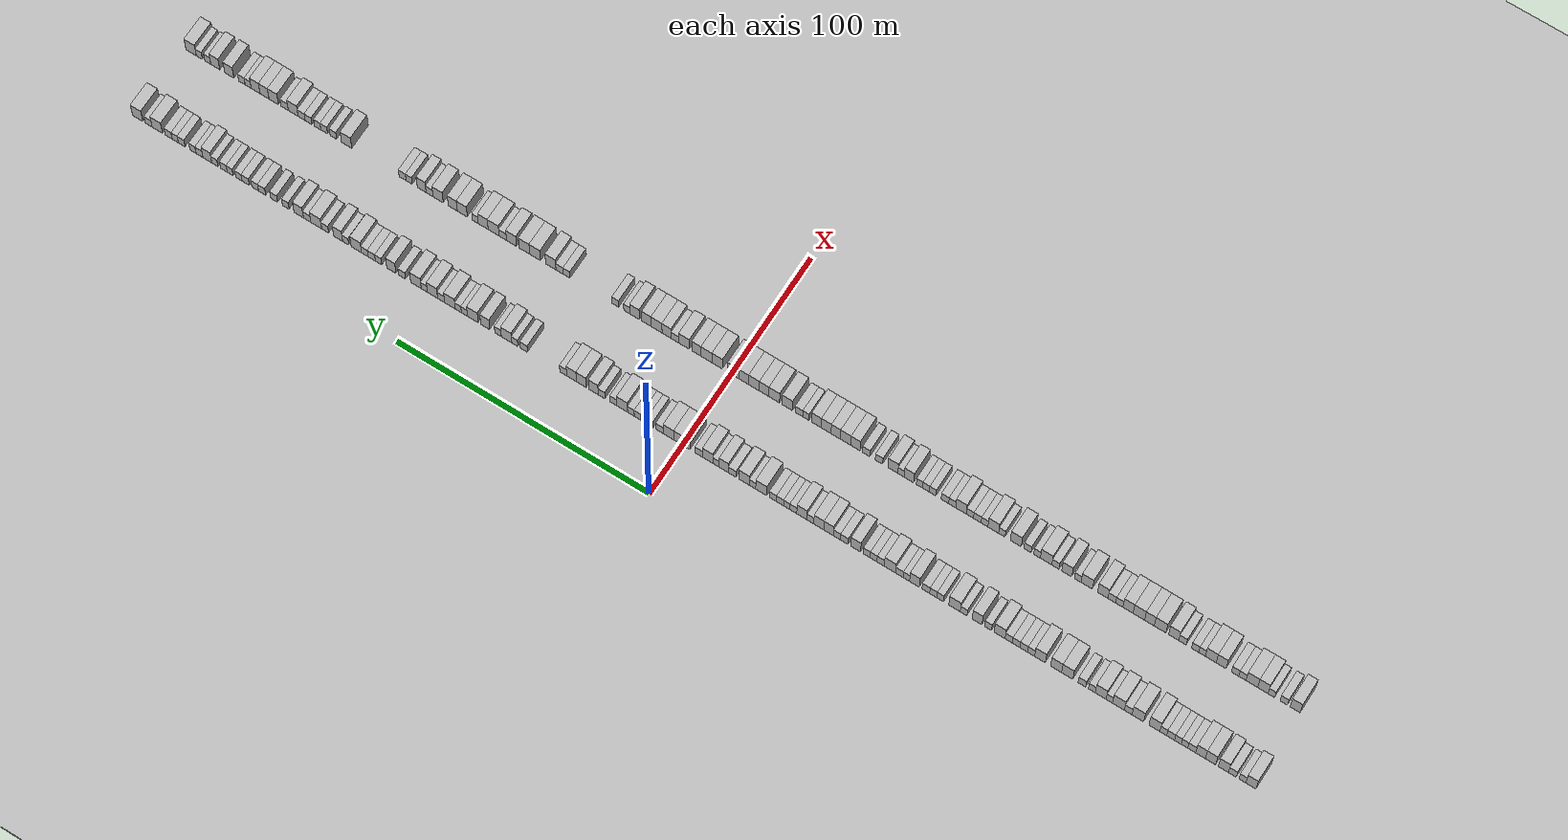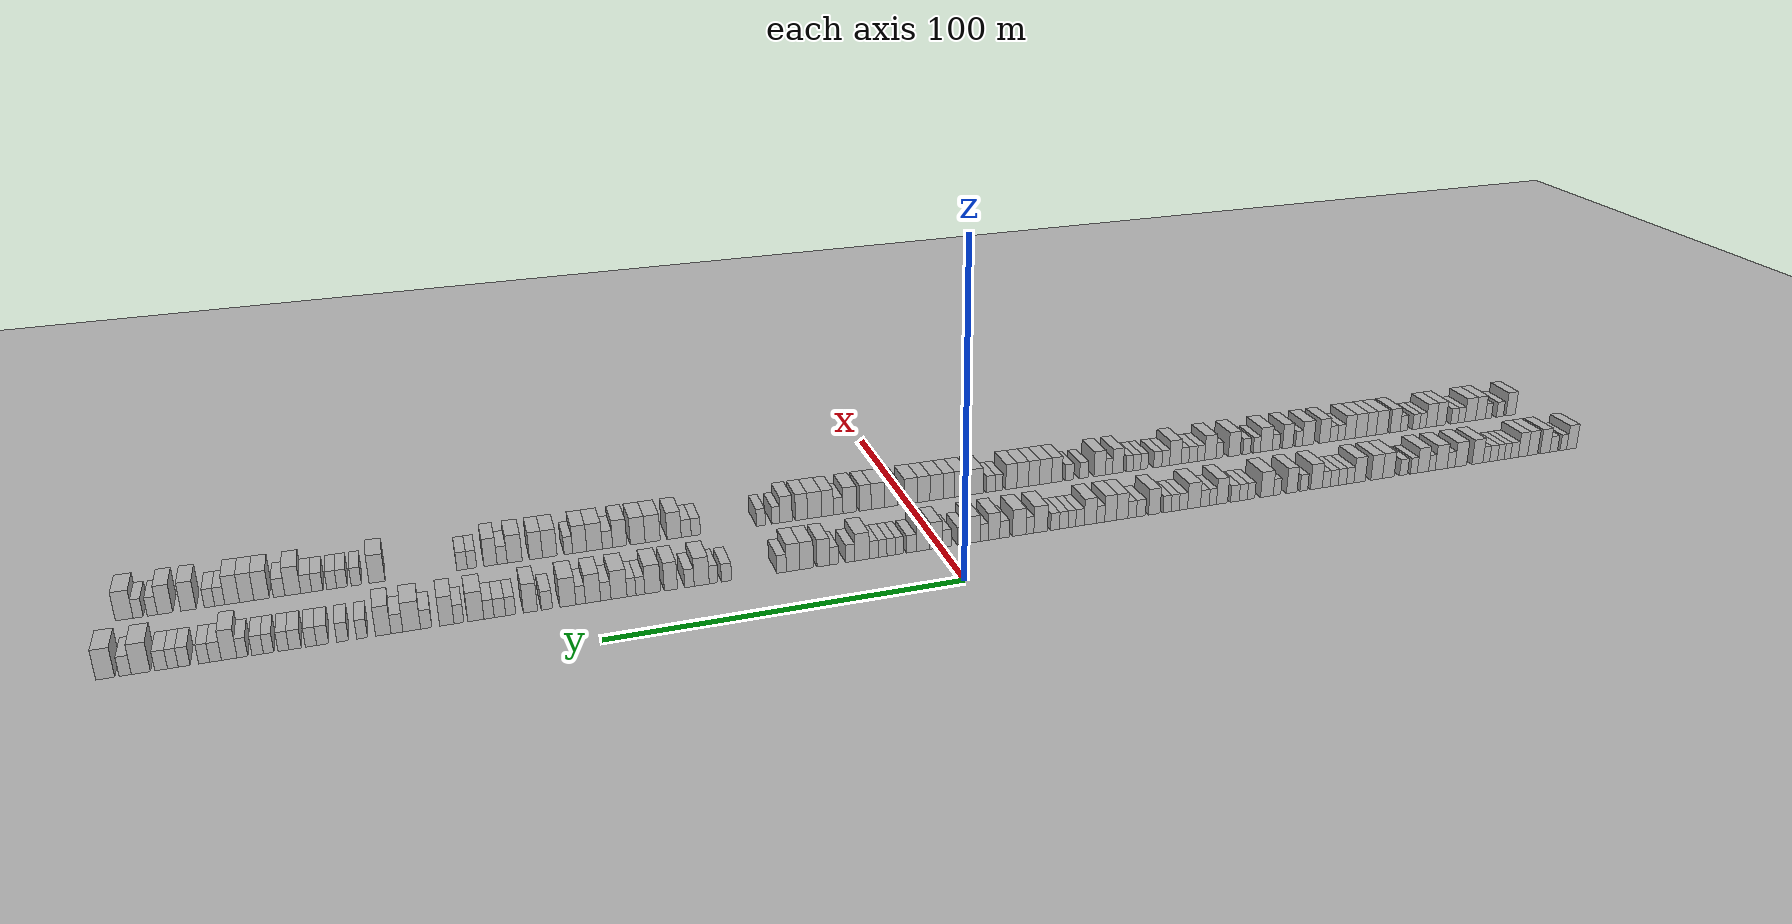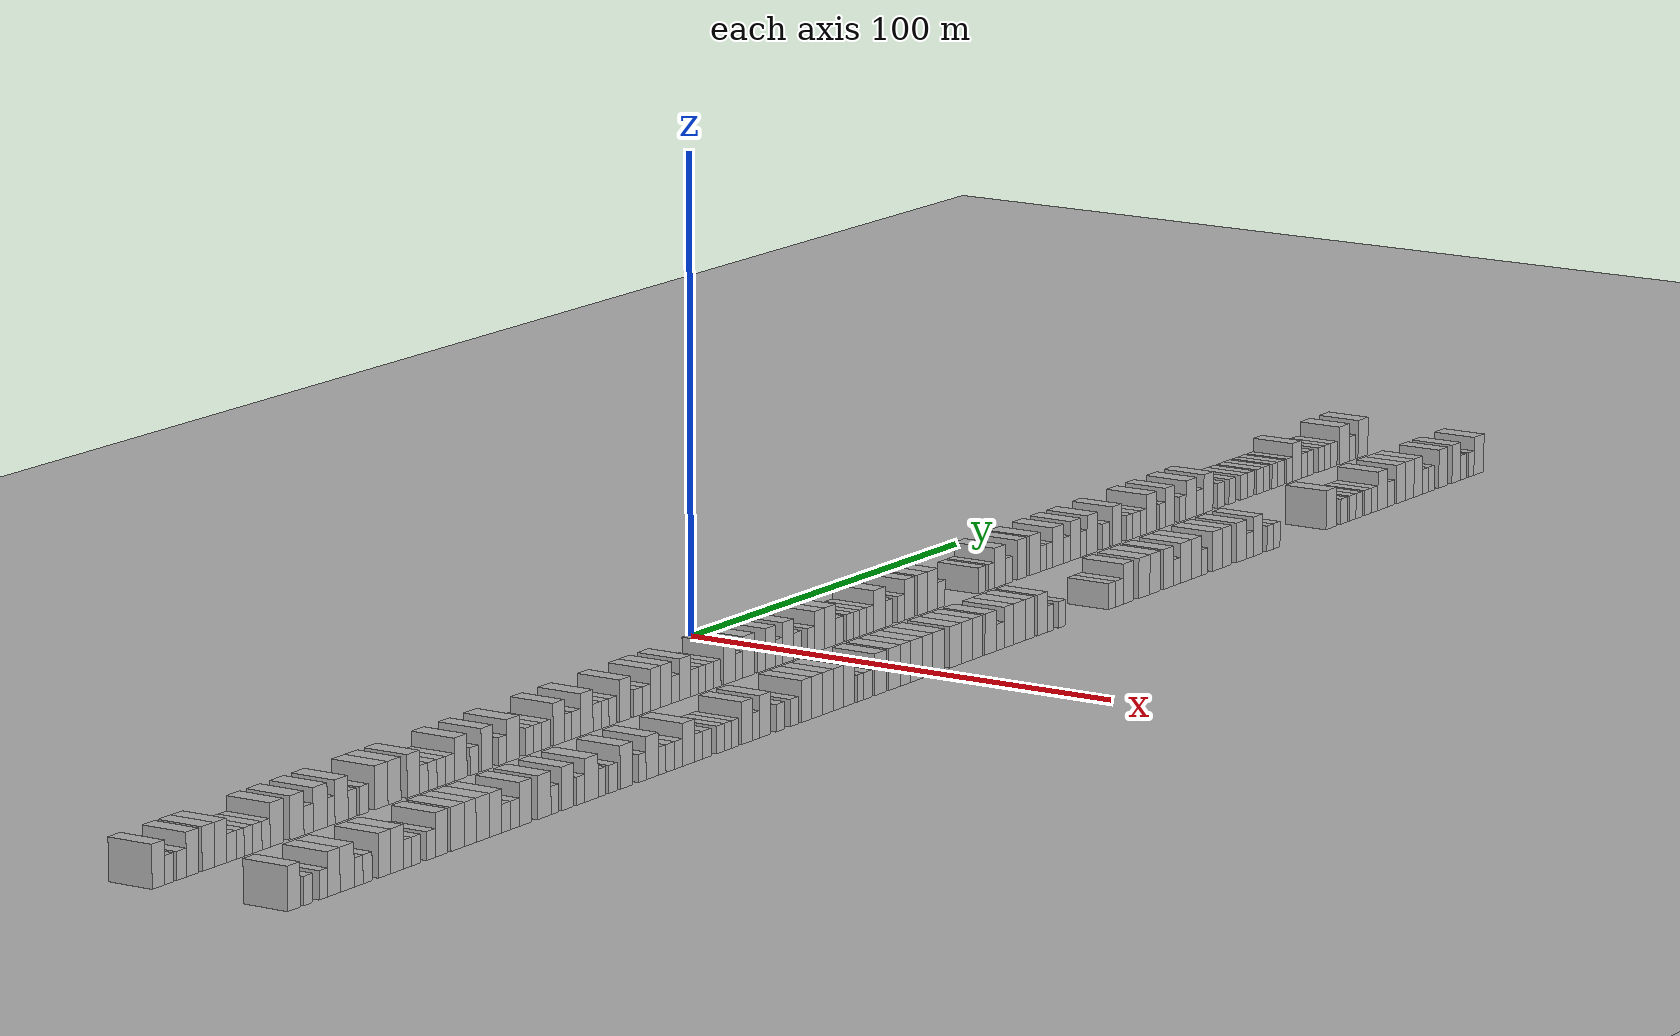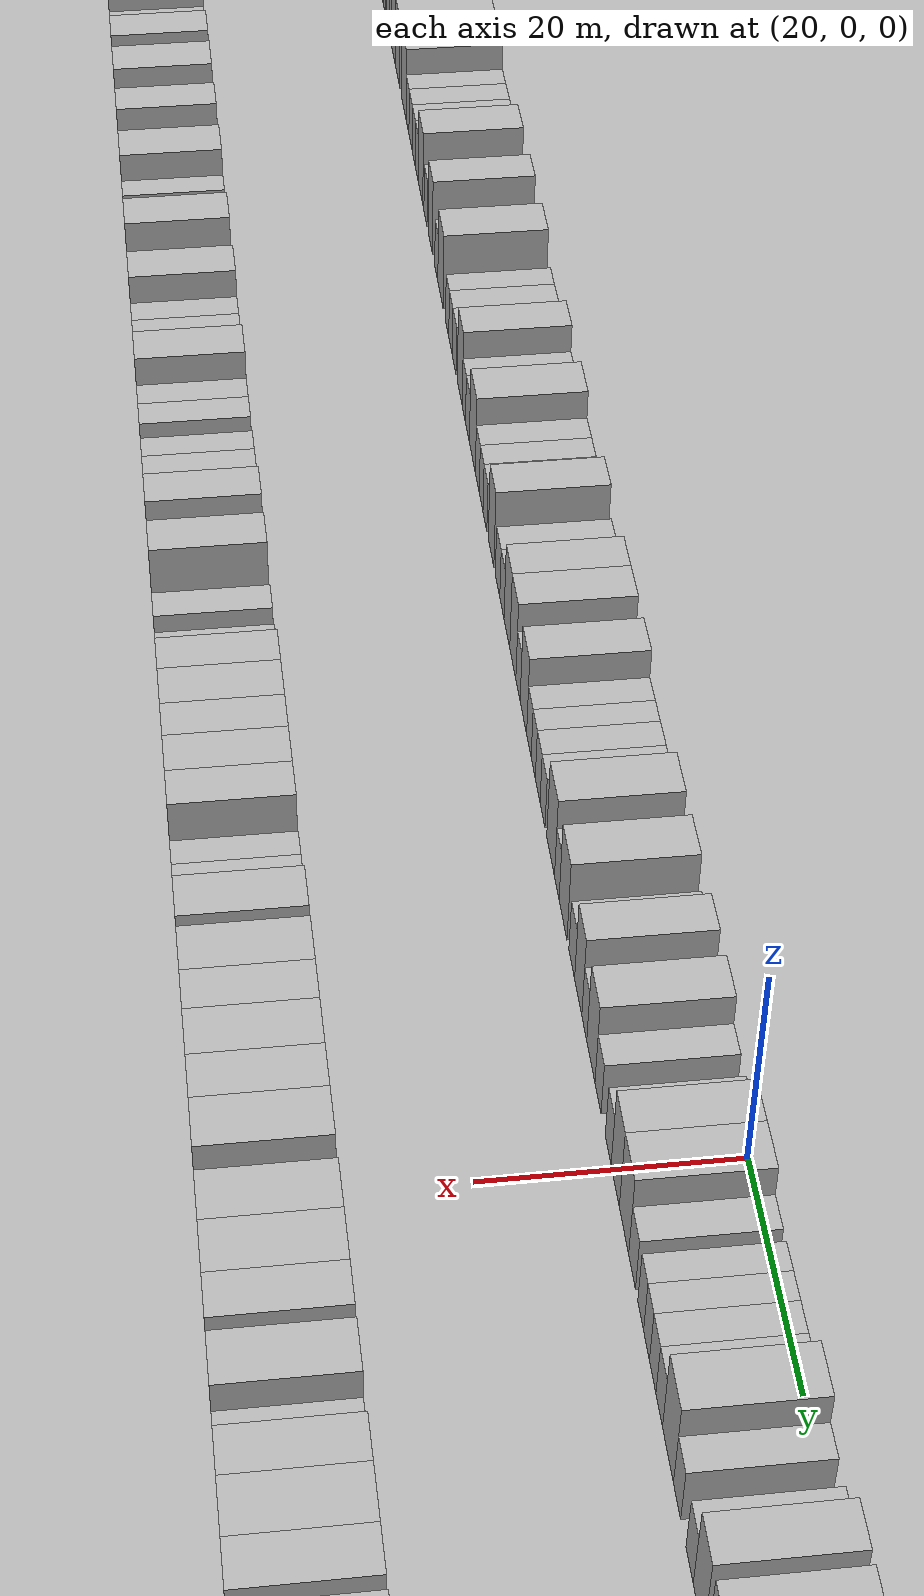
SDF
<?xml version="1.0" encoding="utf-8"?>

<sdf version="1.6">

   <world name="default">

      <gui fullscreen="0">

         <camera name="user_camera">

            <pose>-15 0 4.57585 0 0 0</pose>

            <view_controller>orbit</view_controller>

         </camera>

      </gui>

      <scene>

         <sky>

           <clouds>

             <speed>12</speed>

           </clouds>

         </sky>

         <ambient>0.4 0.4 0.4 1</ambient>

         <background>0.7 0.7 0.7 1</background>

         <shadows>1</shadows>

      </scene>

      <gravity>0 0 -9.8066</gravity>

      <magnetic_field>6e-06 2.3e-05 -4.2e-05</magnetic_field>

      <physics default="0" name="default_physics" type="ode">

         <ode>

            <solver>

               <type>quick</type>

               <iters>10</iters>

               <sor>1.0</sor>

               <use_dynamic_moi_rescaling>0</use_dynamic_moi_rescaling>

            </solver>

            <constraints>

               <cfm>0</cfm>

               <erp>0.2</erp>

               <contact_max_correcting_vel>100</contact_max_correcting_vel>

               <contact_surface_layer>0.001</contact_surface_layer>

            </constraints>

         </ode>

         <max_step_size>0.004</max_step_size>

         <real_time_factor>1</real_time_factor>

         <real_time_update_rate>250</real_time_update_rate>

      </physics>

      <light name="sun" type="directional">

         <cast_shadows>1</cast_shadows>

         <pose>0 0 10 0 0 0</pose>

         <diffuse>0.8 0.8 0.8 1</diffuse>

         <specular>0.2 0.2 0.2 1</specular>

         <attenuation>

            <range>1000</range>

            <constant>0.9</constant>

            <linear>0.01</linear>

            <quadratic>0.001</quadratic>

         </attenuation>

         <direction>-0.5 0.1 -0.9</direction>

      </light>

      <include>

         <name>ground_plane_1</name>

         <uri>model://HANNAS_ground_plane</uri>

         <pose>0 0 0  0 0 0</pose>

      </include>

      <include>

         <name>ground_plane_2</name>

         <uri>model://HANNAS_ground_plane</uri>

         <pose>100 0 0  0 0 0</pose>

      </include>

      <model name="building_1">

         <static>1</static>

         <pose frame="">25.0000 -218.0897 0 0.000000 0.000000 0.000000</pose>

         <link name="link">

            <pose frame="">0 0 4.50 0 0 0</pose>

            <collision name="collision">

               <geometry>

                  <box>

                     <size>10.0000 3.8207 9.0000</size>

                  </box>

               </geometry>

               <max_contacts>10</max_contacts>

               <surface>

                  <contact>

                     <ode/>

                  </contact>

                  <bounce/>

                  <friction>

                     <torsional>

                        <ode/>

                     </torsional>

                     <ode/>

                  </friction>

               </surface>

            </collision>

            <visual name="visual">

               <cast_shadows>0</cast_shadows>

               <geometry>

                  <box>

                     <size>10.0000 3.8207 9.0000</size>

                  </box>

               </geometry>

               <material>

                  <script>

                     <uri>model://HANNAS_wall/materials/scripts</uri>

                     <uri>model://HANNAS_wall/materials/textures</uri>

                     <name>vrc/HANNAS_wall</name>

                  </script>

               </material>

            </visual>

            <self_collide>0</self_collide>

            <enable_wind>0</enable_wind>

            <kinematic>0</kinematic>

         </link>

      </model>

      <model name="building_2">

         <static>1</static>

         <pose frame="">25.0000 -214.8921 0 0.000000 0.000000 0.000000</pose>

         <link name="link">

            <pose frame="">0 0 3.00 0 0 0</pose>

            <collision name="collision">

               <geometry>

                  <box>

                     <size>10.0000 2.5745 6.0000</size>

                  </box>

               </geometry>

               <max_contacts>10</max_contacts>

               <surface>

                  <contact>

                     <ode/>

                  </contact>

                  <bounce/>

                  <friction>

                     <torsional>

                        <ode/>

                     </torsional>

                     <ode/>

                  </friction>

               </surface>

            </collision>

            <visual name="visual">

               <cast_shadows>0</cast_shadows>

               <geometry>

                  <box>

                     <size>10.0000 2.5745 6.0000</size>

                  </box>

               </geometry>

               <material>

                  <script>

                     <uri>model://HANNAS_wall/materials/scripts</uri>

                     <uri>model://HANNAS_wall/materials/textures</uri>

                     <name>vrc/HANNAS_wall</name>

                  </script>

               </material>

            </visual>

            <self_collide>0</self_collide>

            <enable_wind>0</enable_wind>

            <kinematic>0</kinematic>

         </link>

      </model>

      <model name="building_3">

         <static>1</static>

         <pose frame="">25.0000 -211.1258 0 0.000000 0.000000 0.000000</pose>

         <link name="link">

            <pose frame="">0 0 3.00 0 0 0</pose>

            <collision name="collision">

               <geometry>

                  <box>

                     <size>10.0000 2.9583 6.0000</size>

                  </box>

               </geometry>

               <max_contacts>10</max_contacts>

               <surface>

                  <contact>

                     <ode/>

                  </contact>

                  <bounce/>

                  <friction>

                     <torsional>

                        <ode/>

                     </torsional>

                     <ode/>

                  </friction>

               </surface>

            </collision>

            <visual name="visual">

               <cast_shadows>0</cast_shadows>

               <geometry>

                  <box>

                     <size>10.0000 2.9583 6.0000</size>

                  </box>

               </geometry>

               <material>

                  <script>

                     <uri>model://HANNAS_wall/materials/scripts</uri>

                     <uri>model://HANNAS_wall/materials/textures</uri>

                     <name>vrc/HANNAS_wall</name>

                  </script>

               </material>

            </visual>

            <self_collide>0</self_collide>

            <enable_wind>0</enable_wind>

            <kinematic>0</kinematic>

         </link>

      </model>

      <model name="building_4">

         <static>1</static>

         <pose frame="">25.0000 -207.7476 0 0.000000 0.000000 0.000000</pose>

         <link name="link">

            <pose frame="">0 0 4.50 0 0 0</pose>

            <collision name="collision">

               <geometry>

                  <box>

                     <size>10.0000 3.7980 9.0000</size>

                  </box>

               </geometry>

               <max_contacts>10</max_contacts>

               <surface>

                  <contact>

                     <ode/>

                  </contact>

                  <bounce/>

                  <friction>

                     <torsional>

                        <ode/>

                     </torsional>

                     <ode/>

                  </friction>

               </surface>

            </collision>

            <visual name="visual">

               <cast_shadows>0</cast_shadows>

               <geometry>

                  <box>

                     <size>10.0000 3.7980 9.0000</size>

                  </box>

               </geometry>

               <material>

                  <script>

                     <uri>model://HANNAS_wall/materials/scripts</uri>

                     <uri>model://HANNAS_wall/materials/textures</uri>

                     <name>vrc/HANNAS_wall</name>

                  </script>

               </material>

            </visual>

            <self_collide>0</self_collide>

            <enable_wind>0</enable_wind>

            <kinematic>0</kinematic>

         </link>

      </model>

      <model name="building_5">

         <static>1</static>

         <pose frame="">25.0000 -202.9274 0 0.000000 0.000000 0.000000</pose>

         <link name="link">

            <pose frame="">0 0 4.50 0 0 0</pose>

            <collision name="collision">

               <geometry>

                  <box>

                     <size>10.0000 3.8425 9.0000</size>

                  </box>

               </geometry>

               <max_contacts>10</max_contacts>

               <surface>

                  <contact>

                     <ode/>

                  </contact>

                  <bounce/>

                  <friction>

                     <torsional>

                        <ode/>

                     </torsional>

                     <ode/>

                  </friction>

               </surface>

            </collision>

            <visual name="visual">

               <cast_shadows>0</cast_shadows>

               <geometry>

                  <box>

                     <size>10.0000 3.8425 9.0000</size>

                  </box>

               </geometry>

               <material>

                  <script>

                     <uri>model://HANNAS_wall/materials/scripts</uri>

                     <uri>model://HANNAS_wall/materials/textures</uri>

                     <name>vrc/HANNAS_wall</name>

                  </script>

               </material>

            </visual>

            <self_collide>0</self_collide>

            <enable_wind>0</enable_wind>

            <kinematic>0</kinematic>

         </link>

      </model>

      <model name="building_6">

         <static>1</static>

         <pose frame="">25.0000 -199.1834 0 0.000000 0.000000 0.000000</pose>

         <link name="link">

            <pose frame="">0 0 4.50 0 0 0</pose>

            <collision name="collision">

               <geometry>

                  <box>

                     <size>10.0000 3.6454 9.0000</size>

                  </box>

               </geometry>

               <max_contacts>10</max_contacts>

               <surface>

                  <contact>

                     <ode/>

                  </contact>

                  <bounce/>

                  <friction>

                     <torsional>

                        <ode/>

                     </torsional>

                     <ode/>

                  </friction>

               </surface>

            </collision>

            <visual name="visual">

               <cast_shadows>0</cast_shadows>

               <geometry>

                  <box>

                     <size>10.0000 3.6454 9.0000</size>

                  </box>

               </geometry>

               <material>

                  <script>

                     <uri>model://HANNAS_wall/materials/scripts</uri>

                     <uri>model://HANNAS_wall/materials/textures</uri>

                     <name>vrc/HANNAS_wall</name>

                  </script>

               </material>

            </visual>

            <self_collide>0</self_collide>

            <enable_wind>0</enable_wind>

            <kinematic>0</kinematic>

         </link>

      </model>

      <model name="building_7">

         <static>1</static>

         <pose frame="">25.0000 -195.8745 0 0.000000 0.000000 0.000000</pose>

         <link name="link">

            <pose frame="">0 0 3.00 0 0 0</pose>

            <collision name="collision">

               <geometry>

                  <box>

                     <size>10.0000 2.9724 6.0000</size>

                  </box>

               </geometry>

               <max_contacts>10</max_contacts>

               <surface>

                  <contact>

                     <ode/>

                  </contact>

                  <bounce/>

                  <friction>

                     <torsional>

                        <ode/>

                     </torsional>

                     <ode/>

                  </friction>

               </surface>

            </collision>

            <visual name="visual">

               <cast_shadows>0</cast_shadows>

               <geometry>

                  <box>

                     <size>10.0000 2.9724 6.0000</size>

                  </box>

               </geometry>

               <material>

                  <script>

                     <uri>model://HANNAS_wall/materials/scripts</uri>

                     <uri>model://HANNAS_wall/materials/textures</uri>

                     <name>vrc/HANNAS_wall</name>

                  </script>

               </material>

            </visual>

            <self_collide>0</self_collide>

            <enable_wind>0</enable_wind>

            <kinematic>0</kinematic>

         </link>

      </model>

      <model name="building_8">

         <static>1</static>

         <pose frame="">25.0000 -193.1741 0 0.000000 0.000000 0.000000</pose>

         <link name="link">

            <pose frame="">0 0 3.00 0 0 0</pose>

            <collision name="collision">

               <geometry>

                  <box>

                     <size>10.0000 2.4283 6.0000</size>

                  </box>

               </geometry>

               <max_contacts>10</max_contacts>

               <surface>

                  <contact>

                     <ode/>

                  </contact>

                  <bounce/>

                  <friction>

                     <torsional>

                        <ode/>

                     </torsional>

                     <ode/>

                  </friction>

               </surface>

            </collision>

            <visual name="visual">

               <cast_shadows>0</cast_shadows>

               <geometry>

                  <box>

                     <size>10.0000 2.4283 6.0000</size>

                  </box>

               </geometry>

               <material>

                  <script>

                     <uri>model://HANNAS_wall/materials/scripts</uri>

                     <uri>model://HANNAS_wall/materials/textures</uri>

                     <name>vrc/HANNAS_wall</name>

                  </script>

               </material>

            </visual>

            <self_collide>0</self_collide>

            <enable_wind>0</enable_wind>

            <kinematic>0</kinematic>

         </link>

      </model>

      <model name="building_9">

         <static>1</static>

         <pose frame="">25.0000 -190.6987 0 0.000000 0.000000 0.000000</pose>

         <link name="link">

            <pose frame="">0 0 3.00 0 0 0</pose>

            <collision name="collision">

               <geometry>

                  <box>

                     <size>10.0000 2.5225 6.0000</size>

                  </box>

               </geometry>

               <max_contacts>10</max_contacts>

               <surface>

                  <contact>

                     <ode/>

                  </contact>

                  <bounce/>

                  <friction>

                     <torsional>

                        <ode/>

                     </torsional>

                     <ode/>

                  </friction>

               </surface>

            </collision>

            <visual name="visual">

               <cast_shadows>0</cast_shadows>

               <geometry>

                  <box>

                     <size>10.0000 2.5225 6.0000</size>

                  </box>

               </geometry>

               <material>

                  <script>

                     <uri>model://HANNAS_wall/materials/scripts</uri>

                     <uri>model://HANNAS_wall/materials/textures</uri>

                     <name>vrc/HANNAS_wall</name>

                  </script>

               </material>

            </visual>

            <self_collide>0</self_collide>

            <enable_wind>0</enable_wind>

            <kinematic>0</kinematic>

         </link>

      </model>

      <model name="building_10">

         <static>1</static>

         <pose frame="">25.0000 -187.9396 0 0.000000 0.000000 0.000000</pose>

         <link name="link">

            <pose frame="">0 0 3.00 0 0 0</pose>

            <collision name="collision">

               <geometry>

                  <box>

                     <size>10.0000 2.9959 6.0000</size>

                  </box>

               </geometry>

               <max_contacts>10</max_contacts>

               <surface>

                  <contact>

                     <ode/>

                  </contact>

                  <bounce/>

                  <friction>

                     <torsional>

                        <ode/>

                     </torsional>

                     <ode/>

                  </friction>

               </surface>

            </collision>

            <visual name="visual">

               <cast_shadows>0</cast_shadows>

               <geometry>

                  <box>

                     <size>10.0000 2.9959 6.0000</size>

                  </box>

               </geometry>

               <material>

                  <script>

                     <uri>model://HANNAS_wall/materials/scripts</uri>

                     <uri>model://HANNAS_wall/materials/textures</uri>

                     <name>vrc/HANNAS_wall</name>

                  </script>

               </material>

            </visual>

            <self_collide>0</self_collide>

            <enable_wind>0</enable_wind>

            <kinematic>0</kinematic>

         </link>

      </model>

      <model name="building_11">

         <static>1</static>

         <pose frame="">25.0000 -185.1708 0 0.000000 0.000000 0.000000</pose>

         <link name="link">

            <pose frame="">0 0 3.00 0 0 0</pose>

            <collision name="collision">

               <geometry>

                  <box>

                     <size>10.0000 2.5417 6.0000</size>

                  </box>

               </geometry>

               <max_contacts>10</max_contacts>

               <surface>

                  <contact>

                     <ode/>

                  </contact>

                  <bounce/>

                  <friction>

                     <torsional>

                        <ode/>

                     </torsional>

                     <ode/>

                  </friction>

               </surface>

            </collision>

            <visual name="visual">

               <cast_shadows>0</cast_shadows>

               <geometry>

                  <box>

                     <size>10.0000 2.5417 6.0000</size>

                  </box>

               </geometry>

               <material>

                  <script>

                     <uri>model://HANNAS_wall/materials/scripts</uri>

                     <uri>model://HANNAS_wall/materials/textures</uri>

                     <name>vrc/HANNAS_wall</name>

                  </script>

               </material>

            </visual>

            <self_collide>0</self_collide>

            <enable_wind>0</enable_wind>

            <kinematic>0</kinematic>

         </link>

      </model>

      <model name="building_12">

         <static>1</static>

         <pose frame="">25.0000 -181.8260 0 0.000000 0.000000 0.000000</pose>

         <link name="link">

            <pose frame="">0 0 4.50 0 0 0</pose>

            <collision name="collision">

               <geometry>

                  <box>

                     <size>10.0000 4.1478 9.0000</size>

                  </box>

               </geometry>

               <max_contacts>10</max_contacts>

               <surface>

                  <contact>

                     <ode/>

                  </contact>

                  <bounce/>

                  <friction>

                     <torsional>

                        <ode/>

                     </torsional>

                     <ode/>

                  </friction>

               </surface>

            </collision>

            <visual name="visual">

               <cast_shadows>0</cast_shadows>

               <geometry>

                  <box>

                     <size>10.0000 4.1478 9.0000</size>

                  </box>

               </geometry>

               <material>

                  <script>

                     <uri>model://HANNAS_wall/materials/scripts</uri>

                     <uri>model://HANNAS_wall/materials/textures</uri>

                     <name>vrc/HANNAS_wall</name>

                  </script>

               </material>

            </visual>

            <self_collide>0</self_collide>

            <enable_wind>0</enable_wind>

            <kinematic>0</kinematic>

         </link>

      </model>

      <model name="building_13">

         <static>1</static>

         <pose frame="">25.0000 -175.5494 0 0.000000 0.000000 0.000000</pose>

         <link name="link">

            <pose frame="">0 0 4.50 0 0 0</pose>

            <collision name="collision">

               <geometry>

                  <box>

                     <size>10.0000 4.4053 9.0000</size>

                  </box>

               </geometry>

               <max_contacts>10</max_contacts>

               <surface>

                  <contact>

                     <ode/>

                  </contact>

                  <bounce/>

                  <friction>

                     <torsional>

                        <ode/>

                     </torsional>

                     <ode/>

                  </friction>

               </surface>

            </collision>

            <visual name="visual">

               <cast_shadows>0</cast_shadows>

               <geometry>

                  <box>

                     <size>10.0000 4.4053 9.0000</size>

                  </box>

               </geometry>

               <material>

                  <script>

                     <uri>model://HANNAS_wall/materials/scripts</uri>

                     <uri>model://HANNAS_wall/materials/textures</uri>

                     <name>vrc/HANNAS_wall</name>

                  </script>

               </material>

            </visual>

            <self_collide>0</self_collide>

            <enable_wind>0</enable_wind>

            <kinematic>0</kinematic>

         </link>

      </model>

      <model name="building_14">

         <static>1</static>

         <pose frame="">25.0000 -171.8865 0 0.000000 0.000000 0.000000</pose>

         <link name="link">

            <pose frame="">0 0 3.00 0 0 0</pose>

            <collision name="collision">

               <geometry>

                  <box>

                     <size>10.0000 2.9205 6.0000</size>

                  </box>

               </geometry>

               <max_contacts>10</max_contacts>

               <surface>

                  <contact>

                     <ode/>

                  </contact>

                  <bounce/>

                  <friction>

                     <torsional>

                        <ode/>

                     </torsional>

                     <ode/>

                  </friction>

               </surface>

            </collision>

            <visual name="visual">

               <cast_shadows>0</cast_shadows>

               <geometry>

                  <box>

                     <size>10.0000 2.9205 6.0000</size>

                  </box>

               </geometry>

               <material>

                  <script>

                     <uri>model://HANNAS_wall/materials/scripts</uri>

                     <uri>model://HANNAS_wall/materials/textures</uri>

                     <name>vrc/HANNAS_wall</name>

                  </script>

               </material>

            </visual>

            <self_collide>0</self_collide>

            <enable_wind>0</enable_wind>

            <kinematic>0</kinematic>

         </link>

      </model>

      <model name="building_15">

         <static>1</static>

         <pose frame="">25.0000 -168.1947 0 0.000000 0.000000 0.000000</pose>

         <link name="link">

            <pose frame="">0 0 4.50 0 0 0</pose>

            <collision name="collision">

               <geometry>

                  <box>

                     <size>10.0000 4.4631 9.0000</size>

                  </box>

               </geometry>

               <max_contacts>10</max_contacts>

               <surface>

                  <contact>

                     <ode/>

                  </contact>

                  <bounce/>

                  <friction>

                     <torsional>

                        <ode/>

                     </torsional>

                     <ode/>

                  </friction>

               </surface>

            </collision>

            <visual name="visual">

               <cast_shadows>0</cast_shadows>

               <geometry>

                  <box>

                     <size>10.0000 4.4631 9.0000</size>

                  </box>

               </geometry>

               <material>

                  <script>

                     <uri>model://HANNAS_wall/materials/scripts</uri>

                     <uri>model://HANNAS_wall/materials/textures</uri>

                     <name>vrc/HANNAS_wall</name>

                  </script>

               </material>

            </visual>

            <self_collide>0</self_collide>

            <enable_wind>0</enable_wind>

            <kinematic>0</kinematic>

         </link>

      </model>

      <model name="building_16">

         <static>1</static>

         <pose frame="">25.0000 -164.7616 0 0.000000 0.000000 0.000000</pose>

         <link name="link">

            <pose frame="">0 0 3.00 0 0 0</pose>

            <collision name="collision">

               <geometry>

                  <box>

                     <size>10.0000 2.4031 6.0000</size>

                  </box>

               </geometry>

               <max_contacts>10</max_contacts>

               <surface>

                  <contact>

                     <ode/>

                  </contact>

                  <bounce/>

                  <friction>

                     <torsional>

                        <ode/>

                     </torsional>

                     <ode/>

                  </friction>

               </surface>

            </collision>

            <visual name="visual">

               <cast_shadows>0</cast_shadows>

               <geometry>

                  <box>

                     <size>10.0000 2.4031 6.0000</size>

                  </box>

               </geometry>

               <material>

                  <script>

                     <uri>model://HANNAS_wall/materials/scripts</uri>

                     <uri>model://HANNAS_wall/materials/textures</uri>

                     <name>vrc/HANNAS_wall</name>

                  </script>

               </material>

            </visual>

            <self_collide>0</self_collide>

            <enable_wind>0</enable_wind>

            <kinematic>0</kinematic>

         </link>

      </model>

      <model name="building_17">

         <static>1</static>

         <pose frame="">25.0000 -161.4682 0 0.000000 0.000000 0.000000</pose>

         <link name="link">

            <pose frame="">0 0 4.50 0 0 0</pose>

            <collision name="collision">

               <geometry>

                  <box>

                     <size>10.0000 4.1837 9.0000</size>

                  </box>

               </geometry>

               <max_contacts>10</max_contacts>

               <surface>

                  <contact>

                     <ode/>

                  </contact>

                  <bounce/>

                  <friction>

                     <torsional>

                        <ode/>

                     </torsional>

                     <ode/>

                  </friction>

               </surface>

            </collision>

            <visual name="visual">

               <cast_shadows>0</cast_shadows>

               <geometry>

                  <box>

                     <size>10.0000 4.1837 9.0000</size>

                  </box>

               </geometry>

               <material>

                  <script>

                     <uri>model://HANNAS_wall/materials/scripts</uri>

                     <uri>model://HANNAS_wall/materials/textures</uri>

                     <name>vrc/HANNAS_wall</name>

                  </script>

               </material>

            </visual>

            <self_collide>0</self_collide>

            <enable_wind>0</enable_wind>

            <kinematic>0</kinematic>

         </link>

      </model>

      <model name="building_18">

         <static>1</static>

         <pose frame="">25.0000 -158.0925 0 0.000000 0.000000 0.000000</pose>

         <link name="link">

            <pose frame="">0 0 3.00 0 0 0</pose>

            <collision name="collision">

               <geometry>

                  <box>

                     <size>10.0000 2.5677 6.0000</size>

                  </box>

               </geometry>

               <max_contacts>10</max_contacts>

               <surface>

                  <contact>

                     <ode/>

                  </contact>

                  <bounce/>

                  <friction>

                     <torsional>

                        <ode/>

                     </torsional>

                     <ode/>

                  </friction>

               </surface>

            </collision>

            <visual name="visual">

               <cast_shadows>0</cast_shadows>

               <geometry>

                  <box>

                     <size>10.0000 2.5677 6.0000</size>

                  </box>

               </geometry>

               <material>

                  <script>

                     <uri>model://HANNAS_wall/materials/scripts</uri>

                     <uri>model://HANNAS_wall/materials/textures</uri>

                     <name>vrc/HANNAS_wall</name>

                  </script>

               </material>

            </visual>

            <self_collide>0</self_collide>

            <enable_wind>0</enable_wind>

            <kinematic>0</kinematic>

         </link>

      </model>

      <model name="building_19">

         <static>1</static>

         <pose frame="">25.0000 -154.3482 0 0.000000 0.000000 0.000000</pose>

         <link name="link">

            <pose frame="">0 0 3.00 0 0 0</pose>

            <collision name="collision">

               <geometry>

                  <box>

                     <size>10.0000 2.9210 6.0000</size>

                  </box>

               </geometry>

               <max_contacts>10</max_contacts>

               <surface>

                  <contact>

                     <ode/>

                  </contact>

                  <bounce/>

                  <friction>

                     <torsional>

                        <ode/>

                     </torsional>

                     <ode/>

                  </friction>

               </surface>

            </collision>

            <visual name="visual">

               <cast_shadows>0</cast_shadows>

               <geometry>

                  <box>

                     <size>10.0000 2.9210 6.0000</size>

                  </box>

               </geometry>

               <material>

                  <script>

                     <uri>model://HANNAS_wall/materials/scripts</uri>

                     <uri>model://HANNAS_wall/materials/textures</uri>

                     <name>vrc/HANNAS_wall</name>

                  </script>

               </material>

            </visual>

            <self_collide>0</self_collide>

            <enable_wind>0</enable_wind>

            <kinematic>0</kinematic>

         </link>

      </model>

      <model name="building_20">

         <static>1</static>

         <pose frame="">25.0000 -148.7651 0 0.000000 0.000000 0.000000</pose>

         <link name="link">

            <pose frame="">0 0 4.50 0 0 0</pose>

            <collision name="collision">

               <geometry>

                  <box>

                     <size>10.0000 4.2451 9.0000</size>

                  </box>

               </geometry>

               <max_contacts>10</max_contacts>

               <surface>

                  <contact>

                     <ode/>

                  </contact>

                  <bounce/>

                  <friction>

                     <torsional>

                        <ode/>

                     </torsional>

                     <ode/>

                  </friction>

               </surface>

            </collision>

            <visual name="visual">

               <cast_shadows>0</cast_shadows>

               <geometry>

                  <box>

                     <size>10.0000 4.2451 9.0000</size>

                  </box>

               </geometry>

               <material>

                  <script>

                     <uri>model://HANNAS_wall/materials/scripts</uri>

                     <uri>model://HANNAS_wall/materials/textures</uri>

                     <name>vrc/HANNAS_wall</name>

                  </script>

               </material>

            </visual>

            <self_collide>0</self_collide>

            <enable_wind>0</enable_wind>

            <kinematic>0</kinematic>

         </link>

      </model>

      <model name="building_21">

         <static>1</static>

         <pose frame="">25.0000 -144.5374 0 0.000000 0.000000 0.000000</pose>

         <link name="link">

            <pose frame="">0 0 4.50 0 0 0</pose>

            <collision name="collision">

               <geometry>

                  <box>

                     <size>10.0000 4.2104 9.0000</size>

                  </box>

               </geometry>

               <max_contacts>10</max_contacts>

               <surface>

                  <contact>

                     <ode/>

                  </contact>

                  <bounce/>

                  <friction>

                     <torsional>

                        <ode/>

                     </torsional>

                     <ode/>

                  </friction>

               </surface>

            </collision>

            <visual name="visual">

               <cast_shadows>0</cast_shadows>

               <geometry>

                  <box>

                     <size>10.0000 4.2104 9.0000</size>

                  </box>

               </geometry>

               <material>

                  <script>

                     <uri>model://HANNAS_wall/materials/scripts</uri>

                     <uri>model://HANNAS_wall/materials/textures</uri>

                     <name>vrc/HANNAS_wall</name>

                  </script>

               </material>

            </visual>

            <self_collide>0</self_collide>

            <enable_wind>0</enable_wind>

            <kinematic>0</kinematic>

         </link>

      </model>

      <model name="building_22">

         <static>1</static>

         <pose frame="">25.0000 -138.3827 0 0.000000 0.000000 0.000000</pose>

         <link name="link">

            <pose frame="">0 0 4.50 0 0 0</pose>

            <collision name="collision">

               <geometry>

                  <box>

                     <size>10.0000 4.0988 9.0000</size>

                  </box>

               </geometry>

               <max_contacts>10</max_contacts>

               <surface>

                  <contact>

                     <ode/>

                  </contact>

                  <bounce/>

                  <friction>

                     <torsional>

                        <ode/>

                     </torsional>

                     <ode/>

                  </friction>

               </surface>

            </collision>

            <visual name="visual">

               <cast_shadows>0</cast_shadows>

               <geometry>

                  <box>

                     <size>10.0000 4.0988 9.0000</size>

                  </box>

               </geometry>

               <material>

                  <script>

                     <uri>model://HANNAS_wall/materials/scripts</uri>

                     <uri>model://HANNAS_wall/materials/textures</uri>

                     <name>vrc/HANNAS_wall</name>

                  </script>

               </material>

            </visual>

            <self_collide>0</self_collide>

            <enable_wind>0</enable_wind>

            <kinematic>0</kinematic>

         </link>

      </model>

      <model name="building_23">

         <static>1</static>

         <pose frame="">25.0000 -134.9869 0 0.000000 0.000000 0.000000</pose>

         <link name="link">

            <pose frame="">0 0 3.00 0 0 0</pose>

            <collision name="collision">

               <geometry>

                  <box>

                     <size>10.0000 2.6928 6.0000</size>

                  </box>

               </geometry>

               <max_contacts>10</max_contacts>

               <surface>

                  <contact>

                     <ode/>

                  </contact>

                  <bounce/>

                  <friction>

                     <torsional>

                        <ode/>

                     </torsional>

                     <ode/>

                  </friction>

               </surface>

            </collision>

            <visual name="visual">

               <cast_shadows>0</cast_shadows>

               <geometry>

                  <box>

                     <size>10.0000 2.6928 6.0000</size>

                  </box>

               </geometry>

               <material>

                  <script>

                     <uri>model://HANNAS_wall/materials/scripts</uri>

                     <uri>model://HANNAS_wall/materials/textures</uri>

                     <name>vrc/HANNAS_wall</name>

                  </script>

               </material>

            </visual>

            <self_collide>0</self_collide>

            <enable_wind>0</enable_wind>

            <kinematic>0</kinematic>

         </link>

      </model>

      <model name="building_24">

         <static>1</static>

         <pose frame="">25.0000 -132.1823 0 0.000000 0.000000 0.000000</pose>

         <link name="link">

            <pose frame="">0 0 3.00 0 0 0</pose>

            <collision name="collision">

               <geometry>

                  <box>

                     <size>10.0000 2.9164 6.0000</size>

                  </box>

               </geometry>

               <max_contacts>10</max_contacts>

               <surface>

                  <contact>

                     <ode/>

                  </contact>

                  <bounce/>

                  <friction>

                     <torsional>

                        <ode/>

                     </torsional>

                     <ode/>

                  </friction>

               </surface>

            </collision>

            <visual name="visual">

               <cast_shadows>0</cast_shadows>

               <geometry>

                  <box>

                     <size>10.0000 2.9164 6.0000</size>

                  </box>

               </geometry>

               <material>

                  <script>

                     <uri>model://HANNAS_wall/materials/scripts</uri>

                     <uri>model://HANNAS_wall/materials/textures</uri>

                     <name>vrc/HANNAS_wall</name>

                  </script>

               </material>

            </visual>

            <self_collide>0</self_collide>

            <enable_wind>0</enable_wind>

            <kinematic>0</kinematic>

         </link>

      </model>

      <model name="building_25">

         <static>1</static>

         <pose frame="">25.0000 -129.2914 0 0.000000 0.000000 0.000000</pose>

         <link name="link">

            <pose frame="">0 0 3.00 0 0 0</pose>

            <collision name="collision">

               <geometry>

                  <box>

                     <size>10.0000 2.8655 6.0000</size>

                  </box>

               </geometry>

               <max_contacts>10</max_contacts>

               <surface>

                  <contact>

                     <ode/>

                  </contact>

                  <bounce/>

                  <friction>

                     <torsional>

                        <ode/>

                     </torsional>

                     <ode/>

                  </friction>

               </surface>

            </collision>

            <visual name="visual">

               <cast_shadows>0</cast_shadows>

               <geometry>

                  <box>

                     <size>10.0000 2.8655 6.0000</size>

                  </box>

               </geometry>

               <material>

                  <script>

                     <uri>model://HANNAS_wall/materials/scripts</uri>

                     <uri>model://HANNAS_wall/materials/textures</uri>

                     <name>vrc/HANNAS_wall</name>

                  </script>

               </material>

            </visual>

            <self_collide>0</self_collide>

            <enable_wind>0</enable_wind>

            <kinematic>0</kinematic>

         </link>

      </model>

      <model name="building_26">

         <static>1</static>

         <pose frame="">25.0000 -126.4624 0 0.000000 0.000000 0.000000</pose>

         <link name="link">

            <pose frame="">0 0 3.00 0 0 0</pose>

            <collision name="collision">

               <geometry>

                  <box>

                     <size>10.0000 2.7925 6.0000</size>

                  </box>

               </geometry>

               <max_contacts>10</max_contacts>

               <surface>

                  <contact>

                     <ode/>

                  </contact>

                  <bounce/>

                  <friction>

                     <torsional>

                        <ode/>

                     </torsional>

                     <ode/>

                  </friction>

               </surface>

            </collision>

            <visual name="visual">

               <cast_shadows>0</cast_shadows>

               <geometry>

                  <box>

                     <size>10.0000 2.7925 6.0000</size>

                  </box>

               </geometry>

               <material>

                  <script>

                     <uri>model://HANNAS_wall/materials/scripts</uri>

                     <uri>model://HANNAS_wall/materials/textures</uri>

                     <name>vrc/HANNAS_wall</name>

                  </script>

               </material>

            </visual>

            <self_collide>0</self_collide>

            <enable_wind>0</enable_wind>

            <kinematic>0</kinematic>

         </link>

      </model>

      <model name="building_27">

         <static>1</static>

         <pose frame="">25.0000 -122.9737 0 0.000000 0.000000 0.000000</pose>

         <link name="link">

            <pose frame="">0 0 4.50 0 0 0</pose>

            <collision name="collision">

               <geometry>

                  <box>

                     <size>10.0000 4.1849 9.0000</size>

                  </box>

               </geometry>

               <max_contacts>10</max_contacts>

               <surface>

                  <contact>

                     <ode/>

                  </contact>

                  <bounce/>

                  <friction>

                     <torsional>

                        <ode/>

                     </torsional>

                     <ode/>

                  </friction>

               </surface>

            </collision>

            <visual name="visual">

               <cast_shadows>0</cast_shadows>

               <geometry>

                  <box>

                     <size>10.0000 4.1849 9.0000</size>

                  </box>

               </geometry>

               <material>

                  <script>

                     <uri>model://HANNAS_wall/materials/scripts</uri>

                     <uri>model://HANNAS_wall/materials/textures</uri>

                     <name>vrc/HANNAS_wall</name>

                  </script>

               </material>

            </visual>

            <self_collide>0</self_collide>

            <enable_wind>0</enable_wind>

            <kinematic>0</kinematic>

         </link>

      </model>

      <model name="building_28">

         <static>1</static>

         <pose frame="">25.0000 -118.5376 0 0.000000 0.000000 0.000000</pose>

         <link name="link">

            <pose frame="">0 0 3.00 0 0 0</pose>

            <collision name="collision">

               <geometry>

                  <box>

                     <size>10.0000 2.6874 6.0000</size>

                  </box>

               </geometry>

               <max_contacts>10</max_contacts>

               <surface>

                  <contact>

                     <ode/>

                  </contact>

                  <bounce/>

                  <friction>

                     <torsional>

                        <ode/>

                     </torsional>

                     <ode/>

                  </friction>

               </surface>

            </collision>

            <visual name="visual">

               <cast_shadows>0</cast_shadows>

               <geometry>

                  <box>

                     <size>10.0000 2.6874 6.0000</size>

                  </box>

               </geometry>

               <material>

                  <script>

                     <uri>model://HANNAS_wall/materials/scripts</uri>

                     <uri>model://HANNAS_wall/materials/textures</uri>

                     <name>vrc/HANNAS_wall</name>

                  </script>

               </material>

            </visual>

            <self_collide>0</self_collide>

            <enable_wind>0</enable_wind>

            <kinematic>0</kinematic>

         </link>

      </model>

      <model name="building_29">

         <static>1</static>

         <pose frame="">25.0000 -114.3264 0 0.000000 0.000000 0.000000</pose>

         <link name="link">

            <pose frame="">0 0 4.50 0 0 0</pose>

            <collision name="collision">

               <geometry>

                  <box>

                     <size>10.0000 3.7350 9.0000</size>

                  </box>

               </geometry>

               <max_contacts>10</max_contacts>

               <surface>

                  <contact>

                     <ode/>

                  </contact>

                  <bounce/>

                  <friction>

                     <torsional>

                        <ode/>

                     </torsional>

                     <ode/>

                  </friction>

               </surface>

            </collision>

            <visual name="visual">

               <cast_shadows>0</cast_shadows>

               <geometry>

                  <box>

                     <size>10.0000 3.7350 9.0000</size>

                  </box>

               </geometry>

               <material>

                  <script>

                     <uri>model://HANNAS_wall/materials/scripts</uri>

                     <uri>model://HANNAS_wall/materials/textures</uri>

                     <name>vrc/HANNAS_wall</name>

                  </script>

               </material>

            </visual>

            <self_collide>0</self_collide>

            <enable_wind>0</enable_wind>

            <kinematic>0</kinematic>

         </link>

      </model>

      <model name="building_30">

         <static>1</static>

         <pose frame="">25.0000 -109.1636 0 0.000000 0.000000 0.000000</pose>

         <link name="link">

            <pose frame="">0 0 3.00 0 0 0</pose>

            <collision name="collision">

               <geometry>

                  <box>

                     <size>10.0000 2.5906 6.0000</size>

                  </box>

               </geometry>

               <max_contacts>10</max_contacts>

               <surface>

                  <contact>

                     <ode/>

                  </contact>

                  <bounce/>

                  <friction>

                     <torsional>

                        <ode/>

                     </torsional>

                     <ode/>

                  </friction>

               </surface>

            </collision>

            <visual name="visual">

               <cast_shadows>0</cast_shadows>

               <geometry>

                  <box>

                     <size>10.0000 2.5906 6.0000</size>

                  </box>

               </geometry>

               <material>

                  <script>

                     <uri>model://HANNAS_wall/materials/scripts</uri>

                     <uri>model://HANNAS_wall/materials/textures</uri>

                     <name>vrc/HANNAS_wall</name>

                  </script>

               </material>

            </visual>

            <self_collide>0</self_collide>

            <enable_wind>0</enable_wind>

            <kinematic>0</kinematic>

         </link>

      </model>

      <model name="building_31">

         <static>1</static>

         <pose frame="">25.0000 -105.6665 0 0.000000 0.000000 0.000000</pose>

         <link name="link">

            <pose frame="">0 0 4.50 0 0 0</pose>

            <collision name="collision">

               <geometry>

                  <box>

                     <size>10.0000 4.4036 9.0000</size>

                  </box>

               </geometry>

               <max_contacts>10</max_contacts>

               <surface>

                  <contact>

                     <ode/>

                  </contact>

                  <bounce/>

                  <friction>

                     <torsional>

                        <ode/>

                     </torsional>

                     <ode/>

                  </friction>

               </surface>

            </collision>

            <visual name="visual">

               <cast_shadows>0</cast_shadows>

               <geometry>

                  <box>

                     <size>10.0000 4.4036 9.0000</size>

                  </box>

               </geometry>

               <material>

                  <script>

                     <uri>model://HANNAS_wall/materials/scripts</uri>

                     <uri>model://HANNAS_wall/materials/textures</uri>

                     <name>vrc/HANNAS_wall</name>

                  </script>

               </material>

            </visual>

            <self_collide>0</self_collide>

            <enable_wind>0</enable_wind>

            <kinematic>0</kinematic>

         </link>

      </model>

      <model name="building_32">

         <static>1</static>

         <pose frame="">25.0000 -100.1690 0 0.000000 0.000000 0.000000</pose>

         <link name="link">

            <pose frame="">0 0 3.00 0 0 0</pose>

            <collision name="collision">

               <geometry>

                  <box>

                     <size>10.0000 2.5914 6.0000</size>

                  </box>

               </geometry>

               <max_contacts>10</max_contacts>

               <surface>

                  <contact>

                     <ode/>

                  </contact>

                  <bounce/>

                  <friction>

                     <torsional>

                        <ode/>

                     </torsional>

                     <ode/>

                  </friction>

               </surface>

            </collision>

            <visual name="visual">

               <cast_shadows>0</cast_shadows>

               <geometry>

                  <box>

                     <size>10.0000 2.5914 6.0000</size>

                  </box>

               </geometry>

               <material>

                  <script>

                     <uri>model://HANNAS_wall/materials/scripts</uri>

                     <uri>model://HANNAS_wall/materials/textures</uri>

                     <name>vrc/HANNAS_wall</name>

                  </script>

               </material>

            </visual>

            <self_collide>0</self_collide>

            <enable_wind>0</enable_wind>

            <kinematic>0</kinematic>

         </link>

      </model>

      <model name="building_33">

         <static>1</static>

         <pose frame="">25.0000 -97.4928 0 0.000000 0.000000 0.000000</pose>

         <link name="link">

            <pose frame="">0 0 3.00 0 0 0</pose>

            <collision name="collision">

               <geometry>

                  <box>

                     <size>10.0000 2.7609 6.0000</size>

                  </box>

               </geometry>

               <max_contacts>10</max_contacts>

               <surface>

                  <contact>

                     <ode/>

                  </contact>

                  <bounce/>

                  <friction>

                     <torsional>

                        <ode/>

                     </torsional>

                     <ode/>

                  </friction>

               </surface>

            </collision>

            <visual name="visual">

               <cast_shadows>0</cast_shadows>

               <geometry>

                  <box>

                     <size>10.0000 2.7609 6.0000</size>

                  </box>

               </geometry>

               <material>

                  <script>

                     <uri>model://HANNAS_wall/materials/scripts</uri>

                     <uri>model://HANNAS_wall/materials/textures</uri>

                     <name>vrc/HANNAS_wall</name>

                  </script>

               </material>

            </visual>

            <self_collide>0</self_collide>

            <enable_wind>0</enable_wind>

            <kinematic>0</kinematic>

         </link>

      </model>

      <model name="building_34">

         <static>1</static>

         <pose frame="">25.0000 -94.6320 0 0.000000 0.000000 0.000000</pose>

         <link name="link">

            <pose frame="">0 0 3.00 0 0 0</pose>

            <collision name="collision">

               <geometry>

                  <box>

                     <size>10.0000 2.9607 6.0000</size>

                  </box>

               </geometry>

               <max_contacts>10</max_contacts>

               <surface>

                  <contact>

                     <ode/>

                  </contact>

                  <bounce/>

                  <friction>

                     <torsional>

                        <ode/>

                     </torsional>

                     <ode/>

                  </friction>

               </surface>

            </collision>

            <visual name="visual">

               <cast_shadows>0</cast_shadows>

               <geometry>

                  <box>

                     <size>10.0000 2.9607 6.0000</size>

                  </box>

               </geometry>

               <material>

                  <script>

                     <uri>model://HANNAS_wall/materials/scripts</uri>

                     <uri>model://HANNAS_wall/materials/textures</uri>

                     <name>vrc/HANNAS_wall</name>

                  </script>

               </material>

            </visual>

            <self_collide>0</self_collide>

            <enable_wind>0</enable_wind>

            <kinematic>0</kinematic>

         </link>

      </model>

      <model name="building_35">

         <static>1</static>

         <pose frame="">25.0000 -90.2507 0 0.000000 0.000000 0.000000</pose>

         <link name="link">

            <pose frame="">0 0 4.50 0 0 0</pose>

            <collision name="collision">

               <geometry>

                  <box>

                     <size>10.0000 3.8020 9.0000</size>

                  </box>

               </geometry>

               <max_contacts>10</max_contacts>

               <surface>

                  <contact>

                     <ode/>

                  </contact>

                  <bounce/>

                  <friction>

                     <torsional>

                        <ode/>

                     </torsional>

                     <ode/>

                  </friction>

               </surface>

            </collision>

            <visual name="visual">

               <cast_shadows>0</cast_shadows>

               <geometry>

                  <box>

                     <size>10.0000 3.8020 9.0000</size>

                  </box>

               </geometry>

               <material>

                  <script>

                     <uri>model://HANNAS_wall/materials/scripts</uri>

                     <uri>model://HANNAS_wall/materials/textures</uri>

                     <name>vrc/HANNAS_wall</name>

                  </script>

               </material>

            </visual>

            <self_collide>0</self_collide>

            <enable_wind>0</enable_wind>

            <kinematic>0</kinematic>

         </link>

      </model>

      <model name="building_36">

         <static>1</static>

         <pose frame="">25.0000 -87.1026 0 0.000000 0.000000 0.000000</pose>

         <link name="link">

            <pose frame="">0 0 3.00 0 0 0</pose>

            <collision name="collision">

               <geometry>

                  <box>

                     <size>10.0000 2.4942 6.0000</size>

                  </box>

               </geometry>

               <max_contacts>10</max_contacts>

               <surface>

                  <contact>

                     <ode/>

                  </contact>

                  <bounce/>

                  <friction>

                     <torsional>

                        <ode/>

                     </torsional>

                     <ode/>

                  </friction>

               </surface>

            </collision>

            <visual name="visual">

               <cast_shadows>0</cast_shadows>

               <geometry>

                  <box>

                     <size>10.0000 2.4942 6.0000</size>

                  </box>

               </geometry>

               <material>

                  <script>

                     <uri>model://HANNAS_wall/materials/scripts</uri>

                     <uri>model://HANNAS_wall/materials/textures</uri>

                     <name>vrc/HANNAS_wall</name>

                  </script>

               </material>

            </visual>

            <self_collide>0</self_collide>

            <enable_wind>0</enable_wind>

            <kinematic>0</kinematic>

         </link>

      </model>

      <model name="building_37">

         <static>1</static>

         <pose frame="">25.0000 -84.3952 0 0.000000 0.000000 0.000000</pose>

         <link name="link">

            <pose frame="">0 0 3.00 0 0 0</pose>

            <collision name="collision">

               <geometry>

                  <box>

                     <size>10.0000 2.9205 6.0000</size>

                  </box>

               </geometry>

               <max_contacts>10</max_contacts>

               <surface>

                  <contact>

                     <ode/>

                  </contact>

                  <bounce/>

                  <friction>

                     <torsional>

                        <ode/>

                     </torsional>

                     <ode/>

                  </friction>

               </surface>

            </collision>

            <visual name="visual">

               <cast_shadows>0</cast_shadows>

               <geometry>

                  <box>

                     <size>10.0000 2.9205 6.0000</size>

                  </box>

               </geometry>

               <material>

                  <script>

                     <uri>model://HANNAS_wall/materials/scripts</uri>

                     <uri>model://HANNAS_wall/materials/textures</uri>

                     <name>vrc/HANNAS_wall</name>

                  </script>

               </material>

            </visual>

            <self_collide>0</self_collide>

            <enable_wind>0</enable_wind>

            <kinematic>0</kinematic>

         </link>

      </model>

      <model name="building_38">

         <static>1</static>

         <pose frame="">25.0000 -80.7593 0 0.000000 0.000000 0.000000</pose>

         <link name="link">

            <pose frame="">0 0 4.50 0 0 0</pose>

            <collision name="collision">

               <geometry>

                  <box>

                     <size>10.0000 4.3513 9.0000</size>

                  </box>

               </geometry>

               <max_contacts>10</max_contacts>

               <surface>

                  <contact>

                     <ode/>

                  </contact>

                  <bounce/>

                  <friction>

                     <torsional>

                        <ode/>

                     </torsional>

                     <ode/>

                  </friction>

               </surface>

            </collision>

            <visual name="visual">

               <cast_shadows>0</cast_shadows>

               <geometry>

                  <box>

                     <size>10.0000 4.3513 9.0000</size>

                  </box>

               </geometry>

               <material>

                  <script>

                     <uri>model://HANNAS_wall/materials/scripts</uri>

                     <uri>model://HANNAS_wall/materials/textures</uri>

                     <name>vrc/HANNAS_wall</name>

                  </script>

               </material>

            </visual>

            <self_collide>0</self_collide>

            <enable_wind>0</enable_wind>

            <kinematic>0</kinematic>

         </link>

      </model>

      <model name="building_39">

         <static>1</static>

         <pose frame="">25.0000 -77.1736 0 0.000000 0.000000 0.000000</pose>

         <link name="link">

            <pose frame="">0 0 3.00 0 0 0</pose>

            <collision name="collision">

               <geometry>

                  <box>

                     <size>10.0000 2.8200 6.0000</size>

                  </box>

               </geometry>

               <max_contacts>10</max_contacts>

               <surface>

                  <contact>

                     <ode/>

                  </contact>

                  <bounce/>

                  <friction>

                     <torsional>

                        <ode/>

                     </torsional>

                     <ode/>

                  </friction>

               </surface>

            </collision>

            <visual name="visual">

               <cast_shadows>0</cast_shadows>

               <geometry>

                  <box>

                     <size>10.0000 2.8200 6.0000</size>

                  </box>

               </geometry>

               <material>

                  <script>

                     <uri>model://HANNAS_wall/materials/scripts</uri>

                     <uri>model://HANNAS_wall/materials/textures</uri>

                     <name>vrc/HANNAS_wall</name>

                  </script>

               </material>

            </visual>

            <self_collide>0</self_collide>

            <enable_wind>0</enable_wind>

            <kinematic>0</kinematic>

         </link>

      </model>

      <model name="building_40">

         <static>1</static>

         <pose frame="">25.0000 -74.4339 0 0.000000 0.000000 0.000000</pose>

         <link name="link">

            <pose frame="">0 0 3.00 0 0 0</pose>

            <collision name="collision">

               <geometry>

                  <box>

                     <size>10.0000 2.6593 6.0000</size>

                  </box>

               </geometry>

               <max_contacts>10</max_contacts>

               <surface>

                  <contact>

                     <ode/>

                  </contact>

                  <bounce/>

                  <friction>

                     <torsional>

                        <ode/>

                     </torsional>

                     <ode/>

                  </friction>

               </surface>

            </collision>

            <visual name="visual">

               <cast_shadows>0</cast_shadows>

               <geometry>

                  <box>

                     <size>10.0000 2.6593 6.0000</size>

                  </box>

               </geometry>

               <material>

                  <script>

                     <uri>model://HANNAS_wall/materials/scripts</uri>

                     <uri>model://HANNAS_wall/materials/textures</uri>

                     <name>vrc/HANNAS_wall</name>

                  </script>

               </material>

            </visual>

            <self_collide>0</self_collide>

            <enable_wind>0</enable_wind>

            <kinematic>0</kinematic>

         </link>

      </model>

      <model name="building_41">

         <static>1</static>

         <pose frame="">25.0000 -71.7617 0 0.000000 0.000000 0.000000</pose>

         <link name="link">

            <pose frame="">0 0 3.00 0 0 0</pose>

            <collision name="collision">

               <geometry>

                  <box>

                     <size>10.0000 2.6852 6.0000</size>

                  </box>

               </geometry>

               <max_contacts>10</max_contacts>

               <surface>

                  <contact>

                     <ode/>

                  </contact>

                  <bounce/>

                  <friction>

                     <torsional>

                        <ode/>

                     </torsional>

                     <ode/>

                  </friction>

               </surface>

            </collision>

            <visual name="visual">

               <cast_shadows>0</cast_shadows>

               <geometry>

                  <box>

                     <size>10.0000 2.6852 6.0000</size>

                  </box>

               </geometry>

               <material>

                  <script>

                     <uri>model://HANNAS_wall/materials/scripts</uri>

                     <uri>model://HANNAS_wall/materials/textures</uri>

                     <name>vrc/HANNAS_wall</name>

                  </script>

               </material>

            </visual>

            <self_collide>0</self_collide>

            <enable_wind>0</enable_wind>

            <kinematic>0</kinematic>

         </link>

      </model>

      <model name="building_42">

         <static>1</static>

         <pose frame="">25.0000 -67.5142 0 0.000000 0.000000 0.000000</pose>

         <link name="link">

            <pose frame="">0 0 4.50 0 0 0</pose>

            <collision name="collision">

               <geometry>

                  <box>

                     <size>10.0000 3.8098 9.0000</size>

                  </box>

               </geometry>

               <max_contacts>10</max_contacts>

               <surface>

                  <contact>

                     <ode/>

                  </contact>

                  <bounce/>

                  <friction>

                     <torsional>

                        <ode/>

                     </torsional>

                     <ode/>

                  </friction>

               </surface>

            </collision>

            <visual name="visual">

               <cast_shadows>0</cast_shadows>

               <geometry>

                  <box>

                     <size>10.0000 3.8098 9.0000</size>

                  </box>

               </geometry>

               <material>

                  <script>

                     <uri>model://HANNAS_wall/materials/scripts</uri>

                     <uri>model://HANNAS_wall/materials/textures</uri>

                     <name>vrc/HANNAS_wall</name>

                  </script>

               </material>

            </visual>

            <self_collide>0</self_collide>

            <enable_wind>0</enable_wind>

            <kinematic>0</kinematic>

         </link>

      </model>

      <model name="building_43">

         <static>1</static>

         <pose frame="">25.0000 -63.1115 0 0.000000 0.000000 0.000000</pose>

         <link name="link">

            <pose frame="">0 0 3.00 0 0 0</pose>

            <collision name="collision">

               <geometry>

                  <box>

                     <size>10.0000 2.9955 6.0000</size>

                  </box>

               </geometry>

               <max_contacts>10</max_contacts>

               <surface>

                  <contact>

                     <ode/>

                  </contact>

                  <bounce/>

                  <friction>

                     <torsional>

                        <ode/>

                     </torsional>

                     <ode/>

                  </friction>

               </surface>

            </collision>

            <visual name="visual">

               <cast_shadows>0</cast_shadows>

               <geometry>

                  <box>

                     <size>10.0000 2.9955 6.0000</size>

                  </box>

               </geometry>

               <material>

                  <script>

                     <uri>model://HANNAS_wall/materials/scripts</uri>

                     <uri>model://HANNAS_wall/materials/textures</uri>

                     <name>vrc/HANNAS_wall</name>

                  </script>

               </material>

            </visual>

            <self_collide>0</self_collide>

            <enable_wind>0</enable_wind>

            <kinematic>0</kinematic>

         </link>

      </model>

      <model name="building_44">

         <static>1</static>

         <pose frame="">25.0000 -60.2271 0 0.000000 0.000000 0.000000</pose>

         <link name="link">

            <pose frame="">0 0 3.00 0 0 0</pose>

            <collision name="collision">

               <geometry>

                  <box>

                     <size>10.0000 2.7734 6.0000</size>

                  </box>

               </geometry>

               <max_contacts>10</max_contacts>

               <surface>

                  <contact>

                     <ode/>

                  </contact>

                  <bounce/>

                  <friction>

                     <torsional>

                        <ode/>

                     </torsional>

                     <ode/>

                  </friction>

               </surface>

            </collision>

            <visual name="visual">

               <cast_shadows>0</cast_shadows>

               <geometry>

                  <box>

                     <size>10.0000 2.7734 6.0000</size>

                  </box>

               </geometry>

               <material>

                  <script>

                     <uri>model://HANNAS_wall/materials/scripts</uri>

                     <uri>model://HANNAS_wall/materials/textures</uri>

                     <name>vrc/HANNAS_wall</name>

                  </script>

               </material>

            </visual>

            <self_collide>0</self_collide>

            <enable_wind>0</enable_wind>

            <kinematic>0</kinematic>

         </link>

      </model>

      <model name="building_45">

         <static>1</static>

         <pose frame="">25.0000 -56.9690 0 0.000000 0.000000 0.000000</pose>

         <link name="link">

            <pose frame="">0 0 4.50 0 0 0</pose>

            <collision name="collision">

               <geometry>

                  <box>

                     <size>10.0000 3.7427 9.0000</size>

                  </box>

               </geometry>

               <max_contacts>10</max_contacts>

               <surface>

                  <contact>

                     <ode/>

                  </contact>

                  <bounce/>

                  <friction>

                     <torsional>

                        <ode/>

                     </torsional>

                     <ode/>

                  </friction>

               </surface>

            </collision>

            <visual name="visual">

               <cast_shadows>0</cast_shadows>

               <geometry>

                  <box>

                     <size>10.0000 3.7427 9.0000</size>

                  </box>

               </geometry>

               <material>

                  <script>

                     <uri>model://HANNAS_wall/materials/scripts</uri>

                     <uri>model://HANNAS_wall/materials/textures</uri>

                     <name>vrc/HANNAS_wall</name>

                  </script>

               </material>

            </visual>

            <self_collide>0</self_collide>

            <enable_wind>0</enable_wind>

            <kinematic>0</kinematic>

         </link>

      </model>

      <model name="building_46">

         <static>1</static>

         <pose frame="">25.0000 -53.1813 0 0.000000 0.000000 0.000000</pose>

         <link name="link">

            <pose frame="">0 0 4.50 0 0 0</pose>

            <collision name="collision">

               <geometry>

                  <box>

                     <size>10.0000 3.8327 9.0000</size>

                  </box>

               </geometry>

               <max_contacts>10</max_contacts>

               <surface>

                  <contact>

                     <ode/>

                  </contact>

                  <bounce/>

                  <friction>

                     <torsional>

                        <ode/>

                     </torsional>

                     <ode/>

                  </friction>

               </surface>

            </collision>

            <visual name="visual">

               <cast_shadows>0</cast_shadows>

               <geometry>

                  <box>

                     <size>10.0000 3.8327 9.0000</size>

                  </box>

               </geometry>

               <material>

                  <script>

                     <uri>model://HANNAS_wall/materials/scripts</uri>

                     <uri>model://HANNAS_wall/materials/textures</uri>

                     <name>vrc/HANNAS_wall</name>

                  </script>

               </material>

            </visual>

            <self_collide>0</self_collide>

            <enable_wind>0</enable_wind>

            <kinematic>0</kinematic>

         </link>

      </model>

      <model name="building_47">

         <static>1</static>

         <pose frame="">25.0000 -49.9256 0 0.000000 0.000000 0.000000</pose>

         <link name="link">

            <pose frame="">0 0 3.00 0 0 0</pose>

            <collision name="collision">

               <geometry>

                  <box>

                     <size>10.0000 2.6787 6.0000</size>

                  </box>

               </geometry>

               <max_contacts>10</max_contacts>

               <surface>

                  <contact>

                     <ode/>

                  </contact>

                  <bounce/>

                  <friction>

                     <torsional>

                        <ode/>

                     </torsional>

                     <ode/>

                  </friction>

               </surface>

            </collision>

            <visual name="visual">

               <cast_shadows>0</cast_shadows>

               <geometry>

                  <box>

                     <size>10.0000 2.6787 6.0000</size>

                  </box>

               </geometry>

               <material>

                  <script>

                     <uri>model://HANNAS_wall/materials/scripts</uri>

                     <uri>model://HANNAS_wall/materials/textures</uri>

                     <name>vrc/HANNAS_wall</name>

                  </script>

               </material>

            </visual>

            <self_collide>0</self_collide>

            <enable_wind>0</enable_wind>

            <kinematic>0</kinematic>

         </link>

      </model>

      <model name="building_48">

         <static>1</static>

         <pose frame="">25.0000 -46.6115 0 0.000000 0.000000 0.000000</pose>

         <link name="link">

            <pose frame="">0 0 4.50 0 0 0</pose>

            <collision name="collision">

               <geometry>

                  <box>

                     <size>10.0000 3.9495 9.0000</size>

                  </box>

               </geometry>

               <max_contacts>10</max_contacts>

               <surface>

                  <contact>

                     <ode/>

                  </contact>

                  <bounce/>

                  <friction>

                     <torsional>

                        <ode/>

                     </torsional>

                     <ode/>

                  </friction>

               </surface>

            </collision>

            <visual name="visual">

               <cast_shadows>0</cast_shadows>

               <geometry>

                  <box>

                     <size>10.0000 3.9495 9.0000</size>

                  </box>

               </geometry>

               <material>

                  <script>

                     <uri>model://HANNAS_wall/materials/scripts</uri>

                     <uri>model://HANNAS_wall/materials/textures</uri>

                     <name>vrc/HANNAS_wall</name>

                  </script>

               </material>

            </visual>

            <self_collide>0</self_collide>

            <enable_wind>0</enable_wind>

            <kinematic>0</kinematic>

         </link>

      </model>

      <model name="building_49">

         <static>1</static>

         <pose frame="">25.0000 -43.2790 0 0.000000 0.000000 0.000000</pose>

         <link name="link">

            <pose frame="">0 0 3.00 0 0 0</pose>

            <collision name="collision">

               <geometry>

                  <box>

                     <size>10.0000 2.7157 6.0000</size>

                  </box>

               </geometry>

               <max_contacts>10</max_contacts>

               <surface>

                  <contact>

                     <ode/>

                  </contact>

                  <bounce/>

                  <friction>

                     <torsional>

                        <ode/>

                     </torsional>

                     <ode/>

                  </friction>

               </surface>

            </collision>

            <visual name="visual">

               <cast_shadows>0</cast_shadows>

               <geometry>

                  <box>

                     <size>10.0000 2.7157 6.0000</size>

                  </box>

               </geometry>

               <material>

                  <script>

                     <uri>model://HANNAS_wall/materials/scripts</uri>

                     <uri>model://HANNAS_wall/materials/textures</uri>

                     <name>vrc/HANNAS_wall</name>

                  </script>

               </material>

            </visual>

            <self_collide>0</self_collide>

            <enable_wind>0</enable_wind>

            <kinematic>0</kinematic>

         </link>

      </model>

      <model name="building_50">

         <static>1</static>

         <pose frame="">25.0000 -40.7049 0 0.000000 0.000000 0.000000</pose>

         <link name="link">

            <pose frame="">0 0 3.00 0 0 0</pose>

            <collision name="collision">

               <geometry>

                  <box>

                     <size>10.0000 2.4325 6.0000</size>

                  </box>

               </geometry>

               <max_contacts>10</max_contacts>

               <surface>

                  <contact>

                     <ode/>

                  </contact>

                  <bounce/>

                  <friction>

                     <torsional>

                        <ode/>

                     </torsional>

                     <ode/>

                  </friction>

               </surface>

            </collision>

            <visual name="visual">

               <cast_shadows>0</cast_shadows>

               <geometry>

                  <box>

                     <size>10.0000 2.4325 6.0000</size>

                  </box>

               </geometry>

               <material>

                  <script>

                     <uri>model://HANNAS_wall/materials/scripts</uri>

                     <uri>model://HANNAS_wall/materials/textures</uri>

                     <name>vrc/HANNAS_wall</name>

                  </script>

               </material>

            </visual>

            <self_collide>0</self_collide>

            <enable_wind>0</enable_wind>

            <kinematic>0</kinematic>

         </link>

      </model>

      <model name="building_51">

         <static>1</static>

         <pose frame="">25.0000 -38.1090 0 0.000000 0.000000 0.000000</pose>

         <link name="link">

            <pose frame="">0 0 3.00 0 0 0</pose>

            <collision name="collision">

               <geometry>

                  <box>

                     <size>10.0000 2.7592 6.0000</size>

                  </box>

               </geometry>

               <max_contacts>10</max_contacts>

               <surface>

                  <contact>

                     <ode/>

                  </contact>

                  <bounce/>

                  <friction>

                     <torsional>

                        <ode/>

                     </torsional>

                     <ode/>

                  </friction>

               </surface>

            </collision>

            <visual name="visual">

               <cast_shadows>0</cast_shadows>

               <geometry>

                  <box>

                     <size>10.0000 2.7592 6.0000</size>

                  </box>

               </geometry>

               <material>

                  <script>

                     <uri>model://HANNAS_wall/materials/scripts</uri>

                     <uri>model://HANNAS_wall/materials/textures</uri>

                     <name>vrc/HANNAS_wall</name>

                  </script>

               </material>

            </visual>

            <self_collide>0</self_collide>

            <enable_wind>0</enable_wind>

            <kinematic>0</kinematic>

         </link>

      </model>

      <model name="building_52">

         <static>1</static>

         <pose frame="">25.0000 -35.3297 0 0.000000 0.000000 0.000000</pose>

         <link name="link">

            <pose frame="">0 0 3.00 0 0 0</pose>

            <collision name="collision">

               <geometry>

                  <box>

                     <size>10.0000 2.7994 6.0000</size>

                  </box>

               </geometry>

               <max_contacts>10</max_contacts>

               <surface>

                  <contact>

                     <ode/>

                  </contact>

                  <bounce/>

                  <friction>

                     <torsional>

                        <ode/>

                     </torsional>

                     <ode/>

                  </friction>

               </surface>

            </collision>

            <visual name="visual">

               <cast_shadows>0</cast_shadows>

               <geometry>

                  <box>

                     <size>10.0000 2.7994 6.0000</size>

                  </box>

               </geometry>

               <material>

                  <script>

                     <uri>model://HANNAS_wall/materials/scripts</uri>

                     <uri>model://HANNAS_wall/materials/textures</uri>

                     <name>vrc/HANNAS_wall</name>

                  </script>

               </material>

            </visual>

            <self_collide>0</self_collide>

            <enable_wind>0</enable_wind>

            <kinematic>0</kinematic>

         </link>

      </model>

      <model name="building_53">

         <static>1</static>

         <pose frame="">25.0000 -30.7638 0 0.000000 0.000000 0.000000</pose>

         <link name="link">

            <pose frame="">0 0 4.50 0 0 0</pose>

            <collision name="collision">

               <geometry>

                  <box>

                     <size>10.0000 4.3325 9.0000</size>

                  </box>

               </geometry>

               <max_contacts>10</max_contacts>

               <surface>

                  <contact>

                     <ode/>

                  </contact>

                  <bounce/>

                  <friction>

                     <torsional>

                        <ode/>

                     </torsional>

                     <ode/>

                  </friction>

               </surface>

            </collision>

            <visual name="visual">

               <cast_shadows>0</cast_shadows>

               <geometry>

                  <box>

                     <size>10.0000 4.3325 9.0000</size>

                  </box>

               </geometry>

               <material>

                  <script>

                     <uri>model://HANNAS_wall/materials/scripts</uri>

                     <uri>model://HANNAS_wall/materials/textures</uri>

                     <name>vrc/HANNAS_wall</name>

                  </script>

               </material>

            </visual>

            <self_collide>0</self_collide>

            <enable_wind>0</enable_wind>

            <kinematic>0</kinematic>

         </link>

      </model>

      <model name="building_54">

         <static>1</static>

         <pose frame="">25.0000 -27.3550 0 0.000000 0.000000 0.000000</pose>

         <link name="link">

            <pose frame="">0 0 3.00 0 0 0</pose>

            <collision name="collision">

               <geometry>

                  <box>

                     <size>10.0000 2.4850 6.0000</size>

                  </box>

               </geometry>

               <max_contacts>10</max_contacts>

               <surface>

                  <contact>

                     <ode/>

                  </contact>

                  <bounce/>

                  <friction>

                     <torsional>

                        <ode/>

                     </torsional>

                     <ode/>

                  </friction>

               </surface>

            </collision>

            <visual name="visual">

               <cast_shadows>0</cast_shadows>

               <geometry>

                  <box>

                     <size>10.0000 2.4850 6.0000</size>

                  </box>

               </geometry>

               <material>

                  <script>

                     <uri>model://HANNAS_wall/materials/scripts</uri>

                     <uri>model://HANNAS_wall/materials/textures</uri>

                     <name>vrc/HANNAS_wall</name>

                  </script>

               </material>

            </visual>

            <self_collide>0</self_collide>

            <enable_wind>0</enable_wind>

            <kinematic>0</kinematic>

         </link>

      </model>

      <model name="building_55">

         <static>1</static>

         <pose frame="">25.0000 -24.0081 0 0.000000 0.000000 0.000000</pose>

         <link name="link">

            <pose frame="">0 0 4.50 0 0 0</pose>

            <collision name="collision">

               <geometry>

                  <box>

                     <size>10.0000 4.2089 9.0000</size>

                  </box>

               </geometry>

               <max_contacts>10</max_contacts>

               <surface>

                  <contact>

                     <ode/>

                  </contact>

                  <bounce/>

                  <friction>

                     <torsional>

                        <ode/>

                     </torsional>

                     <ode/>

                  </friction>

               </surface>

            </collision>

            <visual name="visual">

               <cast_shadows>0</cast_shadows>

               <geometry>

                  <box>

                     <size>10.0000 4.2089 9.0000</size>

                  </box>

               </geometry>

               <material>

                  <script>

                     <uri>model://HANNAS_wall/materials/scripts</uri>

                     <uri>model://HANNAS_wall/materials/textures</uri>

                     <name>vrc/HANNAS_wall</name>

                  </script>

               </material>

            </visual>

            <self_collide>0</self_collide>

            <enable_wind>0</enable_wind>

            <kinematic>0</kinematic>

         </link>

      </model>

      <model name="building_56">

         <static>1</static>

         <pose frame="">25.0000 -19.4084 0 0.000000 0.000000 0.000000</pose>

         <link name="link">

            <pose frame="">0 0 3.00 0 0 0</pose>

            <collision name="collision">

               <geometry>

                  <box>

                     <size>10.0000 2.9904 6.0000</size>

                  </box>

               </geometry>

               <max_contacts>10</max_contacts>

               <surface>

                  <contact>

                     <ode/>

                  </contact>

                  <bounce/>

                  <friction>

                     <torsional>

                        <ode/>

                     </torsional>

                     <ode/>

                  </friction>

               </surface>

            </collision>

            <visual name="visual">

               <cast_shadows>0</cast_shadows>

               <geometry>

                  <box>

                     <size>10.0000 2.9904 6.0000</size>

                  </box>

               </geometry>

               <material>

                  <script>

                     <uri>model://HANNAS_wall/materials/scripts</uri>

                     <uri>model://HANNAS_wall/materials/textures</uri>

                     <name>vrc/HANNAS_wall</name>

                  </script>

               </material>

            </visual>

            <self_collide>0</self_collide>

            <enable_wind>0</enable_wind>

            <kinematic>0</kinematic>

         </link>

      </model>

      <model name="building_57">

         <static>1</static>

         <pose frame="">25.0000 -16.0879 0 0.000000 0.000000 0.000000</pose>

         <link name="link">

            <pose frame="">0 0 4.50 0 0 0</pose>

            <collision name="collision">

               <geometry>

                  <box>

                     <size>10.0000 3.6505 9.0000</size>

                  </box>

               </geometry>

               <max_contacts>10</max_contacts>

               <surface>

                  <contact>

                     <ode/>

                  </contact>

                  <bounce/>

                  <friction>

                     <torsional>

                        <ode/>

                     </torsional>

                     <ode/>

                  </friction>

               </surface>

            </collision>

            <visual name="visual">

               <cast_shadows>0</cast_shadows>

               <geometry>

                  <box>

                     <size>10.0000 3.6505 9.0000</size>

                  </box>

               </geometry>

               <material>

                  <script>

                     <uri>model://HANNAS_wall/materials/scripts</uri>

                     <uri>model://HANNAS_wall/materials/textures</uri>

                     <name>vrc/HANNAS_wall</name>

                  </script>

               </material>

            </visual>

            <self_collide>0</self_collide>

            <enable_wind>0</enable_wind>

            <kinematic>0</kinematic>

         </link>

      </model>

      <model name="building_58">

         <static>1</static>

         <pose frame="">25.0000 -13.0238 0 0.000000 0.000000 0.000000</pose>

         <link name="link">

            <pose frame="">0 0 3.00 0 0 0</pose>

            <collision name="collision">

               <geometry>

                  <box>

                     <size>10.0000 2.4776 6.0000</size>

                  </box>

               </geometry>

               <max_contacts>10</max_contacts>

               <surface>

                  <contact>

                     <ode/>

                  </contact>

                  <bounce/>

                  <friction>

                     <torsional>

                        <ode/>

                     </torsional>

                     <ode/>

                  </friction>

               </surface>

            </collision>

            <visual name="visual">

               <cast_shadows>0</cast_shadows>

               <geometry>

                  <box>

                     <size>10.0000 2.4776 6.0000</size>

                  </box>

               </geometry>

               <material>

                  <script>

                     <uri>model://HANNAS_wall/materials/scripts</uri>

                     <uri>model://HANNAS_wall/materials/textures</uri>

                     <name>vrc/HANNAS_wall</name>

                  </script>

               </material>

            </visual>

            <self_collide>0</self_collide>

            <enable_wind>0</enable_wind>

            <kinematic>0</kinematic>

         </link>

      </model>

      <model name="building_59">

         <static>1</static>

         <pose frame="">25.0000 -9.7807 0 0.000000 0.000000 0.000000</pose>

         <link name="link">

            <pose frame="">0 0 4.50 0 0 0</pose>

            <collision name="collision">

               <geometry>

                  <box>

                     <size>10.0000 4.0087 9.0000</size>

                  </box>

               </geometry>

               <max_contacts>10</max_contacts>

               <surface>

                  <contact>

                     <ode/>

                  </contact>

                  <bounce/>

                  <friction>

                     <torsional>

                        <ode/>

                     </torsional>

                     <ode/>

                  </friction>

               </surface>

            </collision>

            <visual name="visual">

               <cast_shadows>0</cast_shadows>

               <geometry>

                  <box>

                     <size>10.0000 4.0087 9.0000</size>

                  </box>

               </geometry>

               <material>

                  <script>

                     <uri>model://HANNAS_wall/materials/scripts</uri>

                     <uri>model://HANNAS_wall/materials/textures</uri>

                     <name>vrc/HANNAS_wall</name>

                  </script>

               </material>

            </visual>

            <self_collide>0</self_collide>

            <enable_wind>0</enable_wind>

            <kinematic>0</kinematic>

         </link>

      </model>

      <model name="building_60">

         <static>1</static>

         <pose frame="">25.0000 -6.3212 0 0.000000 0.000000 0.000000</pose>

         <link name="link">

            <pose frame="">0 0 3.00 0 0 0</pose>

            <collision name="collision">

               <geometry>

                  <box>

                     <size>10.0000 2.9103 6.0000</size>

                  </box>

               </geometry>

               <max_contacts>10</max_contacts>

               <surface>

                  <contact>

                     <ode/>

                  </contact>

                  <bounce/>

                  <friction>

                     <torsional>

                        <ode/>

                     </torsional>

                     <ode/>

                  </friction>

               </surface>

            </collision>

            <visual name="visual">

               <cast_shadows>0</cast_shadows>

               <geometry>

                  <box>

                     <size>10.0000 2.9103 6.0000</size>

                  </box>

               </geometry>

               <material>

                  <script>

                     <uri>model://HANNAS_wall/materials/scripts</uri>

                     <uri>model://HANNAS_wall/materials/textures</uri>

                     <name>vrc/HANNAS_wall</name>

                  </script>

               </material>

            </visual>

            <self_collide>0</self_collide>

            <enable_wind>0</enable_wind>

            <kinematic>0</kinematic>

         </link>

      </model>

      <model name="building_61">

         <static>1</static>

         <pose frame="">25.0000 -1.5146 0 0.000000 0.000000 0.000000</pose>

         <link name="link">

            <pose frame="">0 0 3.00 0 0 0</pose>

            <collision name="collision">

               <geometry>

                  <box>

                     <size>10.0000 2.7028 6.0000</size>

                  </box>

               </geometry>

               <max_contacts>10</max_contacts>

               <surface>

                  <contact>

                     <ode/>

                  </contact>

                  <bounce/>

                  <friction>

                     <torsional>

                        <ode/>

                     </torsional>

                     <ode/>

                  </friction>

               </surface>

            </collision>

            <visual name="visual">

               <cast_shadows>0</cast_shadows>

               <geometry>

                  <box>

                     <size>10.0000 2.7028 6.0000</size>

                  </box>

               </geometry>

               <material>

                  <script>

                     <uri>model://HANNAS_wall/materials/scripts</uri>

                     <uri>model://HANNAS_wall/materials/textures</uri>

                     <name>vrc/HANNAS_wall</name>

                  </script>

               </material>

            </visual>

            <self_collide>0</self_collide>

            <enable_wind>0</enable_wind>

            <kinematic>0</kinematic>

         </link>

      </model>

      <model name="building_62">

         <static>1</static>

         <pose frame="">25.0000 1.6985 0 0.000000 0.000000 0.000000</pose>

         <link name="link">

            <pose frame="">0 0 4.50 0 0 0</pose>

            <collision name="collision">

               <geometry>

                  <box>

                     <size>10.0000 3.7234 9.0000</size>

                  </box>

               </geometry>

               <max_contacts>10</max_contacts>

               <surface>

                  <contact>

                     <ode/>

                  </contact>

                  <bounce/>

                  <friction>

                     <torsional>

                        <ode/>

                     </torsional>

                     <ode/>

                  </friction>

               </surface>

            </collision>

            <visual name="visual">

               <cast_shadows>0</cast_shadows>

               <geometry>

                  <box>

                     <size>10.0000 3.7234 9.0000</size>

                  </box>

               </geometry>

               <material>

                  <script>

                     <uri>model://HANNAS_wall/materials/scripts</uri>

                     <uri>model://HANNAS_wall/materials/textures</uri>

                     <name>vrc/HANNAS_wall</name>

                  </script>

               </material>

            </visual>

            <self_collide>0</self_collide>

            <enable_wind>0</enable_wind>

            <kinematic>0</kinematic>

         </link>

      </model>

      <model name="building_63">

         <static>1</static>

         <pose frame="">25.0000 5.6159 0 0.000000 0.000000 0.000000</pose>

         <link name="link">

            <pose frame="">0 0 4.50 0 0 0</pose>

            <collision name="collision">

               <geometry>

                  <box>

                     <size>10.0000 4.1115 9.0000</size>

                  </box>

               </geometry>

               <max_contacts>10</max_contacts>

               <surface>

                  <contact>

                     <ode/>

                  </contact>

                  <bounce/>

                  <friction>

                     <torsional>

                        <ode/>

                     </torsional>

                     <ode/>

                  </friction>

               </surface>

            </collision>

            <visual name="visual">

               <cast_shadows>0</cast_shadows>

               <geometry>

                  <box>

                     <size>10.0000 4.1115 9.0000</size>

                  </box>

               </geometry>

               <material>

                  <script>

                     <uri>model://HANNAS_wall/materials/scripts</uri>

                     <uri>model://HANNAS_wall/materials/textures</uri>

                     <name>vrc/HANNAS_wall</name>

                  </script>

               </material>

            </visual>

            <self_collide>0</self_collide>

            <enable_wind>0</enable_wind>

            <kinematic>0</kinematic>

         </link>

      </model>

      <model name="building_64">

         <static>1</static>

         <pose frame="">25.0000 9.1412 0 0.000000 0.000000 0.000000</pose>

         <link name="link">

            <pose frame="">0 0 3.00 0 0 0</pose>

            <collision name="collision">

               <geometry>

                  <box>

                     <size>10.0000 2.9391 6.0000</size>

                  </box>

               </geometry>

               <max_contacts>10</max_contacts>

               <surface>

                  <contact>

                     <ode/>

                  </contact>

                  <bounce/>

                  <friction>

                     <torsional>

                        <ode/>

                     </torsional>

                     <ode/>

                  </friction>

               </surface>

            </collision>

            <visual name="visual">

               <cast_shadows>0</cast_shadows>

               <geometry>

                  <box>

                     <size>10.0000 2.9391 6.0000</size>

                  </box>

               </geometry>

               <material>

                  <script>

                     <uri>model://HANNAS_wall/materials/scripts</uri>

                     <uri>model://HANNAS_wall/materials/textures</uri>

                     <name>vrc/HANNAS_wall</name>

                  </script>

               </material>

            </visual>

            <self_collide>0</self_collide>

            <enable_wind>0</enable_wind>

            <kinematic>0</kinematic>

         </link>

      </model>

      <model name="building_65">

         <static>1</static>

         <pose frame="">25.0000 12.8299 0 0.000000 0.000000 0.000000</pose>

         <link name="link">

            <pose frame="">0 0 3.00 0 0 0</pose>

            <collision name="collision">

               <geometry>

                  <box>

                     <size>10.0000 2.4383 6.0000</size>

                  </box>

               </geometry>

               <max_contacts>10</max_contacts>

               <surface>

                  <contact>

                     <ode/>

                  </contact>

                  <bounce/>

                  <friction>

                     <torsional>

                        <ode/>

                     </torsional>

                     <ode/>

                  </friction>

               </surface>

            </collision>

            <visual name="visual">

               <cast_shadows>0</cast_shadows>

               <geometry>

                  <box>

                     <size>10.0000 2.4383 6.0000</size>

                  </box>

               </geometry>

               <material>

                  <script>

                     <uri>model://HANNAS_wall/materials/scripts</uri>

                     <uri>model://HANNAS_wall/materials/textures</uri>

                     <name>vrc/HANNAS_wall</name>

                  </script>

               </material>

            </visual>

            <self_collide>0</self_collide>

            <enable_wind>0</enable_wind>

            <kinematic>0</kinematic>

         </link>

      </model>

      <model name="building_66">

         <static>1</static>

         <pose frame="">25.0000 15.2610 0 0.000000 0.000000 0.000000</pose>

         <link name="link">

            <pose frame="">0 0 3.00 0 0 0</pose>

            <collision name="collision">

               <geometry>

                  <box>

                     <size>10.0000 2.4239 6.0000</size>

                  </box>

               </geometry>

               <max_contacts>10</max_contacts>

               <surface>

                  <contact>

                     <ode/>

                  </contact>

                  <bounce/>

                  <friction>

                     <torsional>

                        <ode/>

                     </torsional>

                     <ode/>

                  </friction>

               </surface>

            </collision>

            <visual name="visual">

               <cast_shadows>0</cast_shadows>

               <geometry>

                  <box>

                     <size>10.0000 2.4239 6.0000</size>

                  </box>

               </geometry>

               <material>

                  <script>

                     <uri>model://HANNAS_wall/materials/scripts</uri>

                     <uri>model://HANNAS_wall/materials/textures</uri>

                     <name>vrc/HANNAS_wall</name>

                  </script>

               </material>

            </visual>

            <self_collide>0</self_collide>

            <enable_wind>0</enable_wind>

            <kinematic>0</kinematic>

         </link>

      </model>

      <model name="building_67">

         <static>1</static>

         <pose frame="">25.0000 17.7837 0 0.000000 0.000000 0.000000</pose>

         <link name="link">

            <pose frame="">0 0 3.00 0 0 0</pose>

            <collision name="collision">

               <geometry>

                  <box>

                     <size>10.0000 2.6217 6.0000</size>

                  </box>

               </geometry>

               <max_contacts>10</max_contacts>

               <surface>

                  <contact>

                     <ode/>

                  </contact>

                  <bounce/>

                  <friction>

                     <torsional>

                        <ode/>

                     </torsional>

                     <ode/>

                  </friction>

               </surface>

            </collision>

            <visual name="visual">

               <cast_shadows>0</cast_shadows>

               <geometry>

                  <box>

                     <size>10.0000 2.6217 6.0000</size>

                  </box>

               </geometry>

               <material>

                  <script>

                     <uri>model://HANNAS_wall/materials/scripts</uri>

                     <uri>model://HANNAS_wall/materials/textures</uri>

                     <name>vrc/HANNAS_wall</name>

                  </script>

               </material>

            </visual>

            <self_collide>0</self_collide>

            <enable_wind>0</enable_wind>

            <kinematic>0</kinematic>

         </link>

      </model>

      <model name="building_68">

         <static>1</static>

         <pose frame="">25.0000 20.4191 0 0.000000 0.000000 0.000000</pose>

         <link name="link">

            <pose frame="">0 0 3.00 0 0 0</pose>

            <collision name="collision">

               <geometry>

                  <box>

                     <size>10.0000 2.6491 6.0000</size>

                  </box>

               </geometry>

               <max_contacts>10</max_contacts>

               <surface>

                  <contact>

                     <ode/>

                  </contact>

                  <bounce/>

                  <friction>

                     <torsional>

                        <ode/>

                     </torsional>

                     <ode/>

                  </friction>

               </surface>

            </collision>

            <visual name="visual">

               <cast_shadows>0</cast_shadows>

               <geometry>

                  <box>

                     <size>10.0000 2.6491 6.0000</size>

                  </box>

               </geometry>

               <material>

                  <script>

                     <uri>model://HANNAS_wall/materials/scripts</uri>

                     <uri>model://HANNAS_wall/materials/textures</uri>

                     <name>vrc/HANNAS_wall</name>

                  </script>

               </material>

            </visual>

            <self_collide>0</self_collide>

            <enable_wind>0</enable_wind>

            <kinematic>0</kinematic>

         </link>

      </model>

      <model name="building_69">

         <static>1</static>

         <pose frame="">25.0000 23.8707 0 0.000000 0.000000 0.000000</pose>

         <link name="link">

            <pose frame="">0 0 4.50 0 0 0</pose>

            <collision name="collision">

               <geometry>

                  <box>

                     <size>10.0000 4.2541 9.0000</size>

                  </box>

               </geometry>

               <max_contacts>10</max_contacts>

               <surface>

                  <contact>

                     <ode/>

                  </contact>

                  <bounce/>

                  <friction>

                     <torsional>

                        <ode/>

                     </torsional>

                     <ode/>

                  </friction>

               </surface>

            </collision>

            <visual name="visual">

               <cast_shadows>0</cast_shadows>

               <geometry>

                  <box>

                     <size>10.0000 4.2541 9.0000</size>

                  </box>

               </geometry>

               <material>

                  <script>

                     <uri>model://HANNAS_wall/materials/scripts</uri>

                     <uri>model://HANNAS_wall/materials/textures</uri>

                     <name>vrc/HANNAS_wall</name>

                  </script>

               </material>

            </visual>

            <self_collide>0</self_collide>

            <enable_wind>0</enable_wind>

            <kinematic>0</kinematic>

         </link>

      </model>

      <model name="building_70">

         <static>1</static>

         <pose frame="">25.0000 27.3605 0 0.000000 0.000000 0.000000</pose>

         <link name="link">

            <pose frame="">0 0 3.00 0 0 0</pose>

            <collision name="collision">

               <geometry>

                  <box>

                     <size>10.0000 2.7255 6.0000</size>

                  </box>

               </geometry>

               <max_contacts>10</max_contacts>

               <surface>

                  <contact>

                     <ode/>

                  </contact>

                  <bounce/>

                  <friction>

                     <torsional>

                        <ode/>

                     </torsional>

                     <ode/>

                  </friction>

               </surface>

            </collision>

            <visual name="visual">

               <cast_shadows>0</cast_shadows>

               <geometry>

                  <box>

                     <size>10.0000 2.7255 6.0000</size>

                  </box>

               </geometry>

               <material>

                  <script>

                     <uri>model://HANNAS_wall/materials/scripts</uri>

                     <uri>model://HANNAS_wall/materials/textures</uri>

                     <name>vrc/HANNAS_wall</name>

                  </script>

               </material>

            </visual>

            <self_collide>0</self_collide>

            <enable_wind>0</enable_wind>

            <kinematic>0</kinematic>

         </link>

      </model>

      <model name="building_71">

         <static>1</static>

         <pose frame="">25.0000 32.0574 0 0.000000 0.000000 0.000000</pose>

         <link name="link">

            <pose frame="">0 0 3.00 0 0 0</pose>

            <collision name="collision">

               <geometry>

                  <box>

                     <size>10.0000 2.6683 6.0000</size>

                  </box>

               </geometry>

               <max_contacts>10</max_contacts>

               <surface>

                  <contact>

                     <ode/>

                  </contact>

                  <bounce/>

                  <friction>

                     <torsional>

                        <ode/>

                     </torsional>

                     <ode/>

                  </friction>

               </surface>

            </collision>

            <visual name="visual">

               <cast_shadows>0</cast_shadows>

               <geometry>

                  <box>

                     <size>10.0000 2.6683 6.0000</size>

                  </box>

               </geometry>

               <material>

                  <script>

                     <uri>model://HANNAS_wall/materials/scripts</uri>

                     <uri>model://HANNAS_wall/materials/textures</uri>

                     <name>vrc/HANNAS_wall</name>

                  </script>

               </material>

            </visual>

            <self_collide>0</self_collide>

            <enable_wind>0</enable_wind>

            <kinematic>0</kinematic>

         </link>

      </model>

      <model name="building_72">

         <static>1</static>

         <pose frame="">25.0000 35.2333 0 0.000000 0.000000 0.000000</pose>

         <link name="link">

            <pose frame="">0 0 4.50 0 0 0</pose>

            <collision name="collision">

               <geometry>

                  <box>

                     <size>10.0000 3.6836 9.0000</size>

                  </box>

               </geometry>

               <max_contacts>10</max_contacts>

               <surface>

                  <contact>

                     <ode/>

                  </contact>

                  <bounce/>

                  <friction>

                     <torsional>

                        <ode/>

                     </torsional>

                     <ode/>

                  </friction>

               </surface>

            </collision>

            <visual name="visual">

               <cast_shadows>0</cast_shadows>

               <geometry>

                  <box>

                     <size>10.0000 3.6836 9.0000</size>

                  </box>

               </geometry>

               <material>

                  <script>

                     <uri>model://HANNAS_wall/materials/scripts</uri>

                     <uri>model://HANNAS_wall/materials/textures</uri>

                     <name>vrc/HANNAS_wall</name>

                  </script>

               </material>

            </visual>

            <self_collide>0</self_collide>

            <enable_wind>0</enable_wind>

            <kinematic>0</kinematic>

         </link>

      </model>

      <model name="building_73">

         <static>1</static>

         <pose frame="">25.0000 40.0680 0 0.000000 0.000000 0.000000</pose>

         <link name="link">

            <pose frame="">0 0 4.50 0 0 0</pose>

            <collision name="collision">

               <geometry>

                  <box>

                     <size>10.0000 3.9857 9.0000</size>

                  </box>

               </geometry>

               <max_contacts>10</max_contacts>

               <surface>

                  <contact>

                     <ode/>

                  </contact>

                  <bounce/>

                  <friction>

                     <torsional>

                        <ode/>

                     </torsional>

                     <ode/>

                  </friction>

               </surface>

            </collision>

            <visual name="visual">

               <cast_shadows>0</cast_shadows>

               <geometry>

                  <box>

                     <size>10.0000 3.9857 9.0000</size>

                  </box>

               </geometry>

               <material>

                  <script>

                     <uri>model://HANNAS_wall/materials/scripts</uri>

                     <uri>model://HANNAS_wall/materials/textures</uri>

                     <name>vrc/HANNAS_wall</name>

                  </script>

               </material>

            </visual>

            <self_collide>0</self_collide>

            <enable_wind>0</enable_wind>

            <kinematic>0</kinematic>

         </link>

      </model>

      <model name="building_74">

         <static>1</static>

         <pose frame="">25.0000 43.9865 0 0.000000 0.000000 0.000000</pose>

         <link name="link">

            <pose frame="">0 0 4.50 0 0 0</pose>

            <collision name="collision">

               <geometry>

                  <box>

                     <size>10.0000 3.8513 9.0000</size>

                  </box>

               </geometry>

               <max_contacts>10</max_contacts>

               <surface>

                  <contact>

                     <ode/>

                  </contact>

                  <bounce/>

                  <friction>

                     <torsional>

                        <ode/>

                     </torsional>

                     <ode/>

                  </friction>

               </surface>

            </collision>

            <visual name="visual">

               <cast_shadows>0</cast_shadows>

               <geometry>

                  <box>

                     <size>10.0000 3.8513 9.0000</size>

                  </box>

               </geometry>

               <material>

                  <script>

                     <uri>model://HANNAS_wall/materials/scripts</uri>

                     <uri>model://HANNAS_wall/materials/textures</uri>

                     <name>vrc/HANNAS_wall</name>

                  </script>

               </material>

            </visual>

            <self_collide>0</self_collide>

            <enable_wind>0</enable_wind>

            <kinematic>0</kinematic>

         </link>

      </model>

      <model name="building_75">

         <static>1</static>

         <pose frame="">25.0000 47.2822 0 0.000000 0.000000 0.000000</pose>

         <link name="link">

            <pose frame="">0 0 3.00 0 0 0</pose>

            <collision name="collision">

               <geometry>

                  <box>

                     <size>10.0000 2.7402 6.0000</size>

                  </box>

               </geometry>

               <max_contacts>10</max_contacts>

               <surface>

                  <contact>

                     <ode/>

                  </contact>

                  <bounce/>

                  <friction>

                     <torsional>

                        <ode/>

                     </torsional>

                     <ode/>

                  </friction>

               </surface>

            </collision>

            <visual name="visual">

               <cast_shadows>0</cast_shadows>

               <geometry>

                  <box>

                     <size>10.0000 2.7402 6.0000</size>

                  </box>

               </geometry>

               <material>

                  <script>

                     <uri>model://HANNAS_wall/materials/scripts</uri>

                     <uri>model://HANNAS_wall/materials/textures</uri>

                     <name>vrc/HANNAS_wall</name>

                  </script>

               </material>

            </visual>

            <self_collide>0</self_collide>

            <enable_wind>0</enable_wind>

            <kinematic>0</kinematic>

         </link>

      </model>

      <model name="building_76">

         <static>1</static>

         <pose frame="">25.0000 62.9300 0 0.000000 0.000000 0.000000</pose>

         <link name="link">

            <pose frame="">0 0 3.00 0 0 0</pose>

            <collision name="collision">

               <geometry>

                  <box>

                     <size>10.0000 2.8518 6.0000</size>

                  </box>

               </geometry>

               <max_contacts>10</max_contacts>

               <surface>

                  <contact>

                     <ode/>

                  </contact>

                  <bounce/>

                  <friction>

                     <torsional>

                        <ode/>

                     </torsional>

                     <ode/>

                  </friction>

               </surface>

            </collision>

            <visual name="visual">

               <cast_shadows>0</cast_shadows>

               <geometry>

                  <box>

                     <size>10.0000 2.8518 6.0000</size>

                  </box>

               </geometry>

               <material>

                  <script>

                     <uri>model://HANNAS_wall/materials/scripts</uri>

                     <uri>model://HANNAS_wall/materials/textures</uri>

                     <name>vrc/HANNAS_wall</name>

                  </script>

               </material>

            </visual>

            <self_collide>0</self_collide>

            <enable_wind>0</enable_wind>

            <kinematic>0</kinematic>

         </link>

      </model>

      <model name="building_77">

         <static>1</static>

         <pose frame="">25.0000 66.5714 0 0.000000 0.000000 0.000000</pose>

         <link name="link">

            <pose frame="">0 0 3.00 0 0 0</pose>

            <collision name="collision">

               <geometry>

                  <box>

                     <size>10.0000 2.4311 6.0000</size>

                  </box>

               </geometry>

               <max_contacts>10</max_contacts>

               <surface>

                  <contact>

                     <ode/>

                  </contact>

                  <bounce/>

                  <friction>

                     <torsional>

                        <ode/>

                     </torsional>

                     <ode/>

                  </friction>

               </surface>

            </collision>

            <visual name="visual">

               <cast_shadows>0</cast_shadows>

               <geometry>

                  <box>

                     <size>10.0000 2.4311 6.0000</size>

                  </box>

               </geometry>

               <material>

                  <script>

                     <uri>model://HANNAS_wall/materials/scripts</uri>

                     <uri>model://HANNAS_wall/materials/textures</uri>

                     <name>vrc/HANNAS_wall</name>

                  </script>

               </material>

            </visual>

            <self_collide>0</self_collide>

            <enable_wind>0</enable_wind>

            <kinematic>0</kinematic>

         </link>

      </model>

      <model name="building_78">

         <static>1</static>

         <pose frame="">25.0000 69.8768 0 0.000000 0.000000 0.000000</pose>

         <link name="link">

            <pose frame="">0 0 4.50 0 0 0</pose>

            <collision name="collision">

               <geometry>

                  <box>

                     <size>10.0000 4.1798 9.0000</size>

                  </box>

               </geometry>

               <max_contacts>10</max_contacts>

               <surface>

                  <contact>

                     <ode/>

                  </contact>

                  <bounce/>

                  <friction>

                     <torsional>

                        <ode/>

                     </torsional>

                     <ode/>

                  </friction>

               </surface>

            </collision>

            <visual name="visual">

               <cast_shadows>0</cast_shadows>

               <geometry>

                  <box>

                     <size>10.0000 4.1798 9.0000</size>

                  </box>

               </geometry>

               <material>

                  <script>

                     <uri>model://HANNAS_wall/materials/scripts</uri>

                     <uri>model://HANNAS_wall/materials/textures</uri>

                     <name>vrc/HANNAS_wall</name>

                  </script>

               </material>

            </visual>

            <self_collide>0</self_collide>

            <enable_wind>0</enable_wind>

            <kinematic>0</kinematic>

         </link>

      </model>

      <model name="building_79">

         <static>1</static>

         <pose frame="">25.0000 73.2762 0 0.000000 0.000000 0.000000</pose>

         <link name="link">

            <pose frame="">0 0 3.00 0 0 0</pose>

            <collision name="collision">

               <geometry>

                  <box>

                     <size>10.0000 2.6189 6.0000</size>

                  </box>

               </geometry>

               <max_contacts>10</max_contacts>

               <surface>

                  <contact>

                     <ode/>

                  </contact>

                  <bounce/>

                  <friction>

                     <torsional>

                        <ode/>

                     </torsional>

                     <ode/>

                  </friction>

               </surface>

            </collision>

            <visual name="visual">

               <cast_shadows>0</cast_shadows>

               <geometry>

                  <box>

                     <size>10.0000 2.6189 6.0000</size>

                  </box>

               </geometry>

               <material>

                  <script>

                     <uri>model://HANNAS_wall/materials/scripts</uri>

                     <uri>model://HANNAS_wall/materials/textures</uri>

                     <name>vrc/HANNAS_wall</name>

                  </script>

               </material>

            </visual>

            <self_collide>0</self_collide>

            <enable_wind>0</enable_wind>

            <kinematic>0</kinematic>

         </link>

      </model>

      <model name="building_80">

         <static>1</static>

         <pose frame="">25.0000 78.4050 0 0.000000 0.000000 0.000000</pose>

         <link name="link">

            <pose frame="">0 0 4.50 0 0 0</pose>

            <collision name="collision">

               <geometry>

                  <box>

                     <size>10.0000 3.6388 9.0000</size>

                  </box>

               </geometry>

               <max_contacts>10</max_contacts>

               <surface>

                  <contact>

                     <ode/>

                  </contact>

                  <bounce/>

                  <friction>

                     <torsional>

                        <ode/>

                     </torsional>

                     <ode/>

                  </friction>

               </surface>

            </collision>

            <visual name="visual">

               <cast_shadows>0</cast_shadows>

               <geometry>

                  <box>

                     <size>10.0000 3.6388 9.0000</size>

                  </box>

               </geometry>

               <material>

                  <script>

                     <uri>model://HANNAS_wall/materials/scripts</uri>

                     <uri>model://HANNAS_wall/materials/textures</uri>

                     <name>vrc/HANNAS_wall</name>

                  </script>

               </material>

            </visual>

            <self_collide>0</self_collide>

            <enable_wind>0</enable_wind>

            <kinematic>0</kinematic>

         </link>

      </model>

      <model name="building_81">

         <static>1</static>

         <pose frame="">25.0000 83.3728 0 0.000000 0.000000 0.000000</pose>

         <link name="link">

            <pose frame="">0 0 4.50 0 0 0</pose>

            <collision name="collision">

               <geometry>

                  <box>

                     <size>10.0000 4.2968 9.0000</size>

                  </box>

               </geometry>

               <max_contacts>10</max_contacts>

               <surface>

                  <contact>

                     <ode/>

                  </contact>

                  <bounce/>

                  <friction>

                     <torsional>

                        <ode/>

                     </torsional>

                     <ode/>

                  </friction>

               </surface>

            </collision>

            <visual name="visual">

               <cast_shadows>0</cast_shadows>

               <geometry>

                  <box>

                     <size>10.0000 4.2968 9.0000</size>

                  </box>

               </geometry>

               <material>

                  <script>

                     <uri>model://HANNAS_wall/materials/scripts</uri>

                     <uri>model://HANNAS_wall/materials/textures</uri>

                     <name>vrc/HANNAS_wall</name>

                  </script>

               </material>

            </visual>

            <self_collide>0</self_collide>

            <enable_wind>0</enable_wind>

            <kinematic>0</kinematic>

         </link>

      </model>

      <model name="building_82">

         <static>1</static>

         <pose frame="">25.0000 86.7367 0 0.000000 0.000000 0.000000</pose>

         <link name="link">

            <pose frame="">0 0 3.00 0 0 0</pose>

            <collision name="collision">

               <geometry>

                  <box>

                     <size>10.0000 2.4311 6.0000</size>

                  </box>

               </geometry>

               <max_contacts>10</max_contacts>

               <surface>

                  <contact>

                     <ode/>

                  </contact>

                  <bounce/>

                  <friction>

                     <torsional>

                        <ode/>

                     </torsional>

                     <ode/>

                  </friction>

               </surface>

            </collision>

            <visual name="visual">

               <cast_shadows>0</cast_shadows>

               <geometry>

                  <box>

                     <size>10.0000 2.4311 6.0000</size>

                  </box>

               </geometry>

               <material>

                  <script>

                     <uri>model://HANNAS_wall/materials/scripts</uri>

                     <uri>model://HANNAS_wall/materials/textures</uri>

                     <name>vrc/HANNAS_wall</name>

                  </script>

               </material>

            </visual>

            <self_collide>0</self_collide>

            <enable_wind>0</enable_wind>

            <kinematic>0</kinematic>

         </link>

      </model>

      <model name="building_83">

         <static>1</static>

         <pose frame="">25.0000 89.1733 0 0.000000 0.000000 0.000000</pose>

         <link name="link">

            <pose frame="">0 0 3.00 0 0 0</pose>

            <collision name="collision">

               <geometry>

                  <box>

                     <size>10.0000 2.4420 6.0000</size>

                  </box>

               </geometry>

               <max_contacts>10</max_contacts>

               <surface>

                  <contact>

                     <ode/>

                  </contact>

                  <bounce/>

                  <friction>

                     <torsional>

                        <ode/>

                     </torsional>

                     <ode/>

                  </friction>

               </surface>

            </collision>

            <visual name="visual">

               <cast_shadows>0</cast_shadows>

               <geometry>

                  <box>

                     <size>10.0000 2.4420 6.0000</size>

                  </box>

               </geometry>

               <material>

                  <script>

                     <uri>model://HANNAS_wall/materials/scripts</uri>

                     <uri>model://HANNAS_wall/materials/textures</uri>

                     <name>vrc/HANNAS_wall</name>

                  </script>

               </material>

            </visual>

            <self_collide>0</self_collide>

            <enable_wind>0</enable_wind>

            <kinematic>0</kinematic>

         </link>

      </model>

      <model name="building_84">

         <static>1</static>

         <pose frame="">25.0000 92.5579 0 0.000000 0.000000 0.000000</pose>

         <link name="link">

            <pose frame="">0 0 4.50 0 0 0</pose>

            <collision name="collision">

               <geometry>

                  <box>

                     <size>10.0000 4.3274 9.0000</size>

                  </box>

               </geometry>

               <max_contacts>10</max_contacts>

               <surface>

                  <contact>

                     <ode/>

                  </contact>

                  <bounce/>

                  <friction>

                     <torsional>

                        <ode/>

                     </torsional>

                     <ode/>

                  </friction>

               </surface>

            </collision>

            <visual name="visual">

               <cast_shadows>0</cast_shadows>

               <geometry>

                  <box>

                     <size>10.0000 4.3274 9.0000</size>

                  </box>

               </geometry>

               <material>

                  <script>

                     <uri>model://HANNAS_wall/materials/scripts</uri>

                     <uri>model://HANNAS_wall/materials/textures</uri>

                     <name>vrc/HANNAS_wall</name>

                  </script>

               </material>

            </visual>

            <self_collide>0</self_collide>

            <enable_wind>0</enable_wind>

            <kinematic>0</kinematic>

         </link>

      </model>

      <model name="building_85">

         <static>1</static>

         <pose frame="">25.0000 96.1145 0 0.000000 0.000000 0.000000</pose>

         <link name="link">

            <pose frame="">0 0 3.00 0 0 0</pose>

            <collision name="collision">

               <geometry>

                  <box>

                     <size>10.0000 2.7858 6.0000</size>

                  </box>

               </geometry>

               <max_contacts>10</max_contacts>

               <surface>

                  <contact>

                     <ode/>

                  </contact>

                  <bounce/>

                  <friction>

                     <torsional>

                        <ode/>

                     </torsional>

                     <ode/>

                  </friction>

               </surface>

            </collision>

            <visual name="visual">

               <cast_shadows>0</cast_shadows>

               <geometry>

                  <box>

                     <size>10.0000 2.7858 6.0000</size>

                  </box>

               </geometry>

               <material>

                  <script>

                     <uri>model://HANNAS_wall/materials/scripts</uri>

                     <uri>model://HANNAS_wall/materials/textures</uri>

                     <name>vrc/HANNAS_wall</name>

                  </script>

               </material>

            </visual>

            <self_collide>0</self_collide>

            <enable_wind>0</enable_wind>

            <kinematic>0</kinematic>

         </link>

      </model>

      <model name="building_86">

         <static>1</static>

         <pose frame="">25.0000 99.5493 0 0.000000 0.000000 0.000000</pose>

         <link name="link">

            <pose frame="">0 0 4.50 0 0 0</pose>

            <collision name="collision">

               <geometry>

                  <box>

                     <size>10.0000 4.0838 9.0000</size>

                  </box>

               </geometry>

               <max_contacts>10</max_contacts>

               <surface>

                  <contact>

                     <ode/>

                  </contact>

                  <bounce/>

                  <friction>

                     <torsional>

                        <ode/>

                     </torsional>

                     <ode/>

                  </friction>

               </surface>

            </collision>

            <visual name="visual">

               <cast_shadows>0</cast_shadows>

               <geometry>

                  <box>

                     <size>10.0000 4.0838 9.0000</size>

                  </box>

               </geometry>

               <material>

                  <script>

                     <uri>model://HANNAS_wall/materials/scripts</uri>

                     <uri>model://HANNAS_wall/materials/textures</uri>

                     <name>vrc/HANNAS_wall</name>

                  </script>

               </material>

            </visual>

            <self_collide>0</self_collide>

            <enable_wind>0</enable_wind>

            <kinematic>0</kinematic>

         </link>

      </model>

      <model name="building_87">

         <static>1</static>

         <pose frame="">25.0000 102.8558 0 0.000000 0.000000 0.000000</pose>

         <link name="link">

            <pose frame="">0 0 3.00 0 0 0</pose>

            <collision name="collision">

               <geometry>

                  <box>

                     <size>10.0000 2.5292 6.0000</size>

                  </box>

               </geometry>

               <max_contacts>10</max_contacts>

               <surface>

                  <contact>

                     <ode/>

                  </contact>

                  <bounce/>

                  <friction>

                     <torsional>

                        <ode/>

                     </torsional>

                     <ode/>

                  </friction>

               </surface>

            </collision>

            <visual name="visual">

               <cast_shadows>0</cast_shadows>

               <geometry>

                  <box>

                     <size>10.0000 2.5292 6.0000</size>

                  </box>

               </geometry>

               <material>

                  <script>

                     <uri>model://HANNAS_wall/materials/scripts</uri>

                     <uri>model://HANNAS_wall/materials/textures</uri>

                     <name>vrc/HANNAS_wall</name>

                  </script>

               </material>

            </visual>

            <self_collide>0</self_collide>

            <enable_wind>0</enable_wind>

            <kinematic>0</kinematic>

         </link>

      </model>

      <model name="building_88">

         <static>1</static>

         <pose frame="">25.0000 106.2417 0 0.000000 0.000000 0.000000</pose>

         <link name="link">

            <pose frame="">0 0 4.50 0 0 0</pose>

            <collision name="collision">

               <geometry>

                  <box>

                     <size>10.0000 4.2426 9.0000</size>

                  </box>

               </geometry>

               <max_contacts>10</max_contacts>

               <surface>

                  <contact>

                     <ode/>

                  </contact>

                  <bounce/>

                  <friction>

                     <torsional>

                        <ode/>

                     </torsional>

                     <ode/>

                  </friction>

               </surface>

            </collision>

            <visual name="visual">

               <cast_shadows>0</cast_shadows>

               <geometry>

                  <box>

                     <size>10.0000 4.2426 9.0000</size>

                  </box>

               </geometry>

               <material>

                  <script>

                     <uri>model://HANNAS_wall/materials/scripts</uri>

                     <uri>model://HANNAS_wall/materials/textures</uri>

                     <name>vrc/HANNAS_wall</name>

                  </script>

               </material>

            </visual>

            <self_collide>0</self_collide>

            <enable_wind>0</enable_wind>

            <kinematic>0</kinematic>

         </link>

      </model>

      <model name="building_89">

         <static>1</static>

         <pose frame="">25.0000 111.8222 0 0.000000 0.000000 0.000000</pose>

         <link name="link">

            <pose frame="">0 0 3.00 0 0 0</pose>

            <collision name="collision">

               <geometry>

                  <box>

                     <size>10.0000 2.9185 6.0000</size>

                  </box>

               </geometry>

               <max_contacts>10</max_contacts>

               <surface>

                  <contact>

                     <ode/>

                  </contact>

                  <bounce/>

                  <friction>

                     <torsional>

                        <ode/>

                     </torsional>

                     <ode/>

                  </friction>

               </surface>

            </collision>

            <visual name="visual">

               <cast_shadows>0</cast_shadows>

               <geometry>

                  <box>

                     <size>10.0000 2.9185 6.0000</size>

                  </box>

               </geometry>

               <material>

                  <script>

                     <uri>model://HANNAS_wall/materials/scripts</uri>

                     <uri>model://HANNAS_wall/materials/textures</uri>

                     <name>vrc/HANNAS_wall</name>

                  </script>

               </material>

            </visual>

            <self_collide>0</self_collide>

            <enable_wind>0</enable_wind>

            <kinematic>0</kinematic>

         </link>

      </model>

      <model name="building_90">

         <static>1</static>

         <pose frame="">25.0000 116.1416 0 0.000000 0.000000 0.000000</pose>

         <link name="link">

            <pose frame="">0 0 4.50 0 0 0</pose>

            <collision name="collision">

               <geometry>

                  <box>

                     <size>10.0000 3.7203 9.0000</size>

                  </box>

               </geometry>

               <max_contacts>10</max_contacts>

               <surface>

                  <contact>

                     <ode/>

                  </contact>

                  <bounce/>

                  <friction>

                     <torsional>

                        <ode/>

                     </torsional>

                     <ode/>

                  </friction>

               </surface>

            </collision>

            <visual name="visual">

               <cast_shadows>0</cast_shadows>

               <geometry>

                  <box>

                     <size>10.0000 3.7203 9.0000</size>

                  </box>

               </geometry>

               <material>

                  <script>

                     <uri>model://HANNAS_wall/materials/scripts</uri>

                     <uri>model://HANNAS_wall/materials/textures</uri>

                     <name>vrc/HANNAS_wall</name>

                  </script>

               </material>

            </visual>

            <self_collide>0</self_collide>

            <enable_wind>0</enable_wind>

            <kinematic>0</kinematic>

         </link>

      </model>

      <model name="building_91">

         <static>1</static>

         <pose frame="">25.0000 121.2963 0 0.000000 0.000000 0.000000</pose>

         <link name="link">

            <pose frame="">0 0 3.00 0 0 0</pose>

            <collision name="collision">

               <geometry>

                  <box>

                     <size>10.0000 2.5892 6.0000</size>

                  </box>

               </geometry>

               <max_contacts>10</max_contacts>

               <surface>

                  <contact>

                     <ode/>

                  </contact>

                  <bounce/>

                  <friction>

                     <torsional>

                        <ode/>

                     </torsional>

                     <ode/>

                  </friction>

               </surface>

            </collision>

            <visual name="visual">

               <cast_shadows>0</cast_shadows>

               <geometry>

                  <box>

                     <size>10.0000 2.5892 6.0000</size>

                  </box>

               </geometry>

               <material>

                  <script>

                     <uri>model://HANNAS_wall/materials/scripts</uri>

                     <uri>model://HANNAS_wall/materials/textures</uri>

                     <name>vrc/HANNAS_wall</name>

                  </script>

               </material>

            </visual>

            <self_collide>0</self_collide>

            <enable_wind>0</enable_wind>

            <kinematic>0</kinematic>

         </link>

      </model>

      <model name="building_92">

         <static>1</static>

         <pose frame="">25.0000 124.0865 0 0.000000 0.000000 0.000000</pose>

         <link name="link">

            <pose frame="">0 0 3.00 0 0 0</pose>

            <collision name="collision">

               <geometry>

                  <box>

                     <size>10.0000 2.9911 6.0000</size>

                  </box>

               </geometry>

               <max_contacts>10</max_contacts>

               <surface>

                  <contact>

                     <ode/>

                  </contact>

                  <bounce/>

                  <friction>

                     <torsional>

                        <ode/>

                     </torsional>

                     <ode/>

                  </friction>

               </surface>

            </collision>

            <visual name="visual">

               <cast_shadows>0</cast_shadows>

               <geometry>

                  <box>

                     <size>10.0000 2.9911 6.0000</size>

                  </box>

               </geometry>

               <material>

                  <script>

                     <uri>model://HANNAS_wall/materials/scripts</uri>

                     <uri>model://HANNAS_wall/materials/textures</uri>

                     <name>vrc/HANNAS_wall</name>

                  </script>

               </material>

            </visual>

            <self_collide>0</self_collide>

            <enable_wind>0</enable_wind>

            <kinematic>0</kinematic>

         </link>

      </model>

      <model name="building_93">

         <static>1</static>

         <pose frame="">25.0000 126.9025 0 0.000000 0.000000 0.000000</pose>

         <link name="link">

            <pose frame="">0 0 3.00 0 0 0</pose>

            <collision name="collision">

               <geometry>

                  <box>

                     <size>10.0000 2.6409 6.0000</size>

                  </box>

               </geometry>

               <max_contacts>10</max_contacts>

               <surface>

                  <contact>

                     <ode/>

                  </contact>

                  <bounce/>

                  <friction>

                     <torsional>

                        <ode/>

                     </torsional>

                     <ode/>

                  </friction>

               </surface>

            </collision>

            <visual name="visual">

               <cast_shadows>0</cast_shadows>

               <geometry>

                  <box>

                     <size>10.0000 2.6409 6.0000</size>

                  </box>

               </geometry>

               <material>

                  <script>

                     <uri>model://HANNAS_wall/materials/scripts</uri>

                     <uri>model://HANNAS_wall/materials/textures</uri>

                     <name>vrc/HANNAS_wall</name>

                  </script>

               </material>

            </visual>

            <self_collide>0</self_collide>

            <enable_wind>0</enable_wind>

            <kinematic>0</kinematic>

         </link>

      </model>

      <model name="building_94">

         <static>1</static>

         <pose frame="">25.0000 130.3053 0 0.000000 0.000000 0.000000</pose>

         <link name="link">

            <pose frame="">0 0 4.50 0 0 0</pose>

            <collision name="collision">

               <geometry>

                  <box>

                     <size>10.0000 4.1647 9.0000</size>

                  </box>

               </geometry>

               <max_contacts>10</max_contacts>

               <surface>

                  <contact>

                     <ode/>

                  </contact>

                  <bounce/>

                  <friction>

                     <torsional>

                        <ode/>

                     </torsional>

                     <ode/>

                  </friction>

               </surface>

            </collision>

            <visual name="visual">

               <cast_shadows>0</cast_shadows>

               <geometry>

                  <box>

                     <size>10.0000 4.1647 9.0000</size>

                  </box>

               </geometry>

               <material>

                  <script>

                     <uri>model://HANNAS_wall/materials/scripts</uri>

                     <uri>model://HANNAS_wall/materials/textures</uri>

                     <name>vrc/HANNAS_wall</name>

                  </script>

               </material>

            </visual>

            <self_collide>0</self_collide>

            <enable_wind>0</enable_wind>

            <kinematic>0</kinematic>

         </link>

      </model>

      <model name="building_95">

         <static>1</static>

         <pose frame="">25.0000 134.6357 0 0.000000 0.000000 0.000000</pose>

         <link name="link">

            <pose frame="">0 0 3.00 0 0 0</pose>

            <collision name="collision">

               <geometry>

                  <box>

                     <size>10.0000 2.4962 6.0000</size>

                  </box>

               </geometry>

               <max_contacts>10</max_contacts>

               <surface>

                  <contact>

                     <ode/>

                  </contact>

                  <bounce/>

                  <friction>

                     <torsional>

                        <ode/>

                     </torsional>

                     <ode/>

                  </friction>

               </surface>

            </collision>

            <visual name="visual">

               <cast_shadows>0</cast_shadows>

               <geometry>

                  <box>

                     <size>10.0000 2.4962 6.0000</size>

                  </box>

               </geometry>

               <material>

                  <script>

                     <uri>model://HANNAS_wall/materials/scripts</uri>

                     <uri>model://HANNAS_wall/materials/textures</uri>

                     <name>vrc/HANNAS_wall</name>

                  </script>

               </material>

            </visual>

            <self_collide>0</self_collide>

            <enable_wind>0</enable_wind>

            <kinematic>0</kinematic>

         </link>

      </model>

      <model name="building_96">

         <static>1</static>

         <pose frame="">25.0000 137.7165 0 0.000000 0.000000 0.000000</pose>

         <link name="link">

            <pose frame="">0 0 4.50 0 0 0</pose>

            <collision name="collision">

               <geometry>

                  <box>

                     <size>10.0000 3.6654 9.0000</size>

                  </box>

               </geometry>

               <max_contacts>10</max_contacts>

               <surface>

                  <contact>

                     <ode/>

                  </contact>

                  <bounce/>

                  <friction>

                     <torsional>

                        <ode/>

                     </torsional>

                     <ode/>

                  </friction>

               </surface>

            </collision>

            <visual name="visual">

               <cast_shadows>0</cast_shadows>

               <geometry>

                  <box>

                     <size>10.0000 3.6654 9.0000</size>

                  </box>

               </geometry>

               <material>

                  <script>

                     <uri>model://HANNAS_wall/materials/scripts</uri>

                     <uri>model://HANNAS_wall/materials/textures</uri>

                     <name>vrc/HANNAS_wall</name>

                  </script>

               </material>

            </visual>

            <self_collide>0</self_collide>

            <enable_wind>0</enable_wind>

            <kinematic>0</kinematic>

         </link>

      </model>

      <model name="building_97">

         <static>1</static>

         <pose frame="">25.0000 142.9548 0 0.000000 0.000000 0.000000</pose>

         <link name="link">

            <pose frame="">0 0 3.00 0 0 0</pose>

            <collision name="collision">

               <geometry>

                  <box>

                     <size>10.0000 2.8111 6.0000</size>

                  </box>

               </geometry>

               <max_contacts>10</max_contacts>

               <surface>

                  <contact>

                     <ode/>

                  </contact>

                  <bounce/>

                  <friction>

                     <torsional>

                        <ode/>

                     </torsional>

                     <ode/>

                  </friction>

               </surface>

            </collision>

            <visual name="visual">

               <cast_shadows>0</cast_shadows>

               <geometry>

                  <box>

                     <size>10.0000 2.8111 6.0000</size>

                  </box>

               </geometry>

               <material>

                  <script>

                     <uri>model://HANNAS_wall/materials/scripts</uri>

                     <uri>model://HANNAS_wall/materials/textures</uri>

                     <name>vrc/HANNAS_wall</name>

                  </script>

               </material>

            </visual>

            <self_collide>0</self_collide>

            <enable_wind>0</enable_wind>

            <kinematic>0</kinematic>

         </link>

      </model>

      <model name="building_98">

         <static>1</static>

         <pose frame="">25.0000 146.5897 0 0.000000 0.000000 0.000000</pose>

         <link name="link">

            <pose frame="">0 0 4.50 0 0 0</pose>

            <collision name="collision">

               <geometry>

                  <box>

                     <size>10.0000 4.4589 9.0000</size>

                  </box>

               </geometry>

               <max_contacts>10</max_contacts>

               <surface>

                  <contact>

                     <ode/>

                  </contact>

                  <bounce/>

                  <friction>

                     <torsional>

                        <ode/>

                     </torsional>

                     <ode/>

                  </friction>

               </surface>

            </collision>

            <visual name="visual">

               <cast_shadows>0</cast_shadows>

               <geometry>

                  <box>

                     <size>10.0000 4.4589 9.0000</size>

                  </box>

               </geometry>

               <material>

                  <script>

                     <uri>model://HANNAS_wall/materials/scripts</uri>

                     <uri>model://HANNAS_wall/materials/textures</uri>

                     <name>vrc/HANNAS_wall</name>

                  </script>

               </material>

            </visual>

            <self_collide>0</self_collide>

            <enable_wind>0</enable_wind>

            <kinematic>0</kinematic>

         </link>

      </model>

      <model name="building_99">

         <static>1</static>

         <pose frame="">25.0000 150.2993 0 0.000000 0.000000 0.000000</pose>

         <link name="link">

            <pose frame="">0 0 3.00 0 0 0</pose>

            <collision name="collision">

               <geometry>

                  <box>

                     <size>10.0000 2.9602 6.0000</size>

                  </box>

               </geometry>

               <max_contacts>10</max_contacts>

               <surface>

                  <contact>

                     <ode/>

                  </contact>

                  <bounce/>

                  <friction>

                     <torsional>

                        <ode/>

                     </torsional>

                     <ode/>

                  </friction>

               </surface>

            </collision>

            <visual name="visual">

               <cast_shadows>0</cast_shadows>

               <geometry>

                  <box>

                     <size>10.0000 2.9602 6.0000</size>

                  </box>

               </geometry>

               <material>

                  <script>

                     <uri>model://HANNAS_wall/materials/scripts</uri>

                     <uri>model://HANNAS_wall/materials/textures</uri>

                     <name>vrc/HANNAS_wall</name>

                  </script>

               </material>

            </visual>

            <self_collide>0</self_collide>

            <enable_wind>0</enable_wind>

            <kinematic>0</kinematic>

         </link>

      </model>

      <model name="building_100">

         <static>1</static>

         <pose frame="">25.0000 153.7009 0 0.000000 0.000000 0.000000</pose>

         <link name="link">

            <pose frame="">0 0 4.50 0 0 0</pose>

            <collision name="collision">

               <geometry>

                  <box>

                     <size>10.0000 3.8431 9.0000</size>

                  </box>

               </geometry>

               <max_contacts>10</max_contacts>

               <surface>

                  <contact>

                     <ode/>

                  </contact>

                  <bounce/>

                  <friction>

                     <torsional>

                        <ode/>

                     </torsional>

                     <ode/>

                  </friction>

               </surface>

            </collision>

            <visual name="visual">

               <cast_shadows>0</cast_shadows>

               <geometry>

                  <box>

                     <size>10.0000 3.8431 9.0000</size>

                  </box>

               </geometry>

               <material>

                  <script>

                     <uri>model://HANNAS_wall/materials/scripts</uri>

                     <uri>model://HANNAS_wall/materials/textures</uri>

                     <name>vrc/HANNAS_wall</name>

                  </script>

               </material>

            </visual>

            <self_collide>0</self_collide>

            <enable_wind>0</enable_wind>

            <kinematic>0</kinematic>

         </link>

      </model>

      <model name="building_101">

         <static>1</static>

         <pose frame="">25.0000 158.9646 0 0.000000 0.000000 0.000000</pose>

         <link name="link">

            <pose frame="">0 0 3.00 0 0 0</pose>

            <collision name="collision">

               <geometry>

                  <box>

                     <size>10.0000 2.6843 6.0000</size>

                  </box>

               </geometry>

               <max_contacts>10</max_contacts>

               <surface>

                  <contact>

                     <ode/>

                  </contact>

                  <bounce/>

                  <friction>

                     <torsional>

                        <ode/>

                     </torsional>

                     <ode/>

                  </friction>

               </surface>

            </collision>

            <visual name="visual">

               <cast_shadows>0</cast_shadows>

               <geometry>

                  <box>

                     <size>10.0000 2.6843 6.0000</size>

                  </box>

               </geometry>

               <material>

                  <script>

                     <uri>model://HANNAS_wall/materials/scripts</uri>

                     <uri>model://HANNAS_wall/materials/textures</uri>

                     <name>vrc/HANNAS_wall</name>

                  </script>

               </material>

            </visual>

            <self_collide>0</self_collide>

            <enable_wind>0</enable_wind>

            <kinematic>0</kinematic>

         </link>

      </model>

      <model name="building_102">

         <static>1</static>

         <pose frame="">25.0000 163.7403 0 0.000000 0.000000 0.000000</pose>

         <link name="link">

            <pose frame="">0 0 3.00 0 0 0</pose>

            <collision name="collision">

               <geometry>

                  <box>

                     <size>10.0000 2.8672 6.0000</size>

                  </box>

               </geometry>

               <max_contacts>10</max_contacts>

               <surface>

                  <contact>

                     <ode/>

                  </contact>

                  <bounce/>

                  <friction>

                     <torsional>

                        <ode/>

                     </torsional>

                     <ode/>

                  </friction>

               </surface>

            </collision>

            <visual name="visual">

               <cast_shadows>0</cast_shadows>

               <geometry>

                  <box>

                     <size>10.0000 2.8672 6.0000</size>

                  </box>

               </geometry>

               <material>

                  <script>

                     <uri>model://HANNAS_wall/materials/scripts</uri>

                     <uri>model://HANNAS_wall/materials/textures</uri>

                     <name>vrc/HANNAS_wall</name>

                  </script>

               </material>

            </visual>

            <self_collide>0</self_collide>

            <enable_wind>0</enable_wind>

            <kinematic>0</kinematic>

         </link>

      </model>

      <model name="building_103">

         <static>1</static>

         <pose frame="">25.0000 168.6398 0 0.000000 0.000000 0.000000</pose>

         <link name="link">

            <pose frame="">0 0 3.00 0 0 0</pose>

            <collision name="collision">

               <geometry>

                  <box>

                     <size>10.0000 2.9318 6.0000</size>

                  </box>

               </geometry>

               <max_contacts>10</max_contacts>

               <surface>

                  <contact>

                     <ode/>

                  </contact>

                  <bounce/>

                  <friction>

                     <torsional>

                        <ode/>

                     </torsional>

                     <ode/>

                  </friction>

               </surface>

            </collision>

            <visual name="visual">

               <cast_shadows>0</cast_shadows>

               <geometry>

                  <box>

                     <size>10.0000 2.9318 6.0000</size>

                  </box>

               </geometry>

               <material>

                  <script>

                     <uri>model://HANNAS_wall/materials/scripts</uri>

                     <uri>model://HANNAS_wall/materials/textures</uri>

                     <name>vrc/HANNAS_wall</name>

                  </script>

               </material>

            </visual>

            <self_collide>0</self_collide>

            <enable_wind>0</enable_wind>

            <kinematic>0</kinematic>

         </link>

      </model>

      <model name="building_104">

         <static>1</static>

         <pose frame="">25.0000 171.4720 0 0.000000 0.000000 0.000000</pose>

         <link name="link">

            <pose frame="">0 0 3.00 0 0 0</pose>

            <collision name="collision">

               <geometry>

                  <box>

                     <size>10.0000 2.7326 6.0000</size>

                  </box>

               </geometry>

               <max_contacts>10</max_contacts>

               <surface>

                  <contact>

                     <ode/>

                  </contact>

                  <bounce/>

                  <friction>

                     <torsional>

                        <ode/>

                     </torsional>

                     <ode/>

                  </friction>

               </surface>

            </collision>

            <visual name="visual">

               <cast_shadows>0</cast_shadows>

               <geometry>

                  <box>

                     <size>10.0000 2.7326 6.0000</size>

                  </box>

               </geometry>

               <material>

                  <script>

                     <uri>model://HANNAS_wall/materials/scripts</uri>

                     <uri>model://HANNAS_wall/materials/textures</uri>

                     <name>vrc/HANNAS_wall</name>

                  </script>

               </material>

            </visual>

            <self_collide>0</self_collide>

            <enable_wind>0</enable_wind>

            <kinematic>0</kinematic>

         </link>

      </model>

      <model name="building_105">

         <static>1</static>

         <pose frame="">25.0000 175.3368 0 0.000000 0.000000 0.000000</pose>

         <link name="link">

            <pose frame="">0 0 3.00 0 0 0</pose>

            <collision name="collision">

               <geometry>

                  <box>

                     <size>10.0000 2.9971 6.0000</size>

                  </box>

               </geometry>

               <max_contacts>10</max_contacts>

               <surface>

                  <contact>

                     <ode/>

                  </contact>

                  <bounce/>

                  <friction>

                     <torsional>

                        <ode/>

                     </torsional>

                     <ode/>

                  </friction>

               </surface>

            </collision>

            <visual name="visual">

               <cast_shadows>0</cast_shadows>

               <geometry>

                  <box>

                     <size>10.0000 2.9971 6.0000</size>

                  </box>

               </geometry>

               <material>

                  <script>

                     <uri>model://HANNAS_wall/materials/scripts</uri>

                     <uri>model://HANNAS_wall/materials/textures</uri>

                     <name>vrc/HANNAS_wall</name>

                  </script>

               </material>

            </visual>

            <self_collide>0</self_collide>

            <enable_wind>0</enable_wind>

            <kinematic>0</kinematic>

         </link>

      </model>

      <model name="building_106">

         <static>1</static>

         <pose frame="">25.0000 178.1459 0 0.000000 0.000000 0.000000</pose>

         <link name="link">

            <pose frame="">0 0 3.00 0 0 0</pose>

            <collision name="collision">

               <geometry>

                  <box>

                     <size>10.0000 2.6212 6.0000</size>

                  </box>

               </geometry>

               <max_contacts>10</max_contacts>

               <surface>

                  <contact>

                     <ode/>

                  </contact>

                  <bounce/>

                  <friction>

                     <torsional>

                        <ode/>

                     </torsional>

                     <ode/>

                  </friction>

               </surface>

            </collision>

            <visual name="visual">

               <cast_shadows>0</cast_shadows>

               <geometry>

                  <box>

                     <size>10.0000 2.6212 6.0000</size>

                  </box>

               </geometry>

               <material>

                  <script>

                     <uri>model://HANNAS_wall/materials/scripts</uri>

                     <uri>model://HANNAS_wall/materials/textures</uri>

                     <name>vrc/HANNAS_wall</name>

                  </script>

               </material>

            </visual>

            <self_collide>0</self_collide>

            <enable_wind>0</enable_wind>

            <kinematic>0</kinematic>

         </link>

      </model>

      <model name="building_107">

         <static>1</static>

         <pose frame="">25.0000 181.6971 0 0.000000 0.000000 0.000000</pose>

         <link name="link">

            <pose frame="">0 0 3.00 0 0 0</pose>

            <collision name="collision">

               <geometry>

                  <box>

                     <size>10.0000 2.4813 6.0000</size>

                  </box>

               </geometry>

               <max_contacts>10</max_contacts>

               <surface>

                  <contact>

                     <ode/>

                  </contact>

                  <bounce/>

                  <friction>

                     <torsional>

                        <ode/>

                     </torsional>

                     <ode/>

                  </friction>

               </surface>

            </collision>

            <visual name="visual">

               <cast_shadows>0</cast_shadows>

               <geometry>

                  <box>

                     <size>10.0000 2.4813 6.0000</size>

                  </box>

               </geometry>

               <material>

                  <script>

                     <uri>model://HANNAS_wall/materials/scripts</uri>

                     <uri>model://HANNAS_wall/materials/textures</uri>

                     <name>vrc/HANNAS_wall</name>

                  </script>

               </material>

            </visual>

            <self_collide>0</self_collide>

            <enable_wind>0</enable_wind>

            <kinematic>0</kinematic>

         </link>

      </model>

      <model name="building_108">

         <static>1</static>

         <pose frame="">25.0000 184.3073 0 0.000000 0.000000 0.000000</pose>

         <link name="link">

            <pose frame="">0 0 3.00 0 0 0</pose>

            <collision name="collision">

               <geometry>

                  <box>

                     <size>10.0000 2.7390 6.0000</size>

                  </box>

               </geometry>

               <max_contacts>10</max_contacts>

               <surface>

                  <contact>

                     <ode/>

                  </contact>

                  <bounce/>

                  <friction>

                     <torsional>

                        <ode/>

                     </torsional>

                     <ode/>

                  </friction>

               </surface>

            </collision>

            <visual name="visual">

               <cast_shadows>0</cast_shadows>

               <geometry>

                  <box>

                     <size>10.0000 2.7390 6.0000</size>

                  </box>

               </geometry>

               <material>

                  <script>

                     <uri>model://HANNAS_wall/materials/scripts</uri>

                     <uri>model://HANNAS_wall/materials/textures</uri>

                     <name>vrc/HANNAS_wall</name>

                  </script>

               </material>

            </visual>

            <self_collide>0</self_collide>

            <enable_wind>0</enable_wind>

            <kinematic>0</kinematic>

         </link>

      </model>

      <model name="building_109">

         <static>1</static>

         <pose frame="">25.0000 187.9462 0 0.000000 0.000000 0.000000</pose>

         <link name="link">

            <pose frame="">0 0 3.00 0 0 0</pose>

            <collision name="collision">

               <geometry>

                  <box>

                     <size>10.0000 2.5390 6.0000</size>

                  </box>

               </geometry>

               <max_contacts>10</max_contacts>

               <surface>

                  <contact>

                     <ode/>

                  </contact>

                  <bounce/>

                  <friction>

                     <torsional>

                        <ode/>

                     </torsional>

                     <ode/>

                  </friction>

               </surface>

            </collision>

            <visual name="visual">

               <cast_shadows>0</cast_shadows>

               <geometry>

                  <box>

                     <size>10.0000 2.5390 6.0000</size>

                  </box>

               </geometry>

               <material>

                  <script>

                     <uri>model://HANNAS_wall/materials/scripts</uri>

                     <uri>model://HANNAS_wall/materials/textures</uri>

                     <name>vrc/HANNAS_wall</name>

                  </script>

               </material>

            </visual>

            <self_collide>0</self_collide>

            <enable_wind>0</enable_wind>

            <kinematic>0</kinematic>

         </link>

      </model>

      <model name="building_110">

         <static>1</static>

         <pose frame="">25.0000 191.0550 0 0.000000 0.000000 0.000000</pose>

         <link name="link">

            <pose frame="">0 0 4.50 0 0 0</pose>

            <collision name="collision">

               <geometry>

                  <box>

                     <size>10.0000 3.6785 9.0000</size>

                  </box>

               </geometry>

               <max_contacts>10</max_contacts>

               <surface>

                  <contact>

                     <ode/>

                  </contact>

                  <bounce/>

                  <friction>

                     <torsional>

                        <ode/>

                     </torsional>

                     <ode/>

                  </friction>

               </surface>

            </collision>

            <visual name="visual">

               <cast_shadows>0</cast_shadows>

               <geometry>

                  <box>

                     <size>10.0000 3.6785 9.0000</size>

                  </box>

               </geometry>

               <material>

                  <script>

                     <uri>model://HANNAS_wall/materials/scripts</uri>

                     <uri>model://HANNAS_wall/materials/textures</uri>

                     <name>vrc/HANNAS_wall</name>

                  </script>

               </material>

            </visual>

            <self_collide>0</self_collide>

            <enable_wind>0</enable_wind>

            <kinematic>0</kinematic>

         </link>

      </model>

      <model name="building_111">

         <static>1</static>

         <pose frame="">25.0000 194.2967 0 0.000000 0.000000 0.000000</pose>

         <link name="link">

            <pose frame="">0 0 3.00 0 0 0</pose>

            <collision name="collision">

               <geometry>

                  <box>

                     <size>10.0000 2.8050 6.0000</size>

                  </box>

               </geometry>

               <max_contacts>10</max_contacts>

               <surface>

                  <contact>

                     <ode/>

                  </contact>

                  <bounce/>

                  <friction>

                     <torsional>

                        <ode/>

                     </torsional>

                     <ode/>

                  </friction>

               </surface>

            </collision>

            <visual name="visual">

               <cast_shadows>0</cast_shadows>

               <geometry>

                  <box>

                     <size>10.0000 2.8050 6.0000</size>

                  </box>

               </geometry>

               <material>

                  <script>

                     <uri>model://HANNAS_wall/materials/scripts</uri>

                     <uri>model://HANNAS_wall/materials/textures</uri>

                     <name>vrc/HANNAS_wall</name>

                  </script>

               </material>

            </visual>

            <self_collide>0</self_collide>

            <enable_wind>0</enable_wind>

            <kinematic>0</kinematic>

         </link>

      </model>

      <model name="building_112">

         <static>1</static>

         <pose frame="">25.0000 196.9752 0 0.000000 0.000000 0.000000</pose>

         <link name="link">

            <pose frame="">0 0 3.00 0 0 0</pose>

            <collision name="collision">

               <geometry>

                  <box>

                     <size>10.0000 2.5521 6.0000</size>

                  </box>

               </geometry>

               <max_contacts>10</max_contacts>

               <surface>

                  <contact>

                     <ode/>

                  </contact>

                  <bounce/>

                  <friction>

                     <torsional>

                        <ode/>

                     </torsional>

                     <ode/>

                  </friction>

               </surface>

            </collision>

            <visual name="visual">

               <cast_shadows>0</cast_shadows>

               <geometry>

                  <box>

                     <size>10.0000 2.5521 6.0000</size>

                  </box>

               </geometry>

               <material>

                  <script>

                     <uri>model://HANNAS_wall/materials/scripts</uri>

                     <uri>model://HANNAS_wall/materials/textures</uri>

                     <name>vrc/HANNAS_wall</name>

                  </script>

               </material>

            </visual>

            <self_collide>0</self_collide>

            <enable_wind>0</enable_wind>

            <kinematic>0</kinematic>

         </link>

      </model>

      <model name="building_113">

         <static>1</static>

         <pose frame="">25.0000 201.6248 0 0.000000 0.000000 0.000000</pose>

         <link name="link">

            <pose frame="">0 0 3.00 0 0 0</pose>

            <collision name="collision">

               <geometry>

                  <box>

                     <size>10.0000 2.7472 6.0000</size>

                  </box>

               </geometry>

               <max_contacts>10</max_contacts>

               <surface>

                  <contact>

                     <ode/>

                  </contact>

                  <bounce/>

                  <friction>

                     <torsional>

                        <ode/>

                     </torsional>

                     <ode/>

                  </friction>

               </surface>

            </collision>

            <visual name="visual">

               <cast_shadows>0</cast_shadows>

               <geometry>

                  <box>

                     <size>10.0000 2.7472 6.0000</size>

                  </box>

               </geometry>

               <material>

                  <script>

                     <uri>model://HANNAS_wall/materials/scripts</uri>

                     <uri>model://HANNAS_wall/materials/textures</uri>

                     <name>vrc/HANNAS_wall</name>

                  </script>

               </material>

            </visual>

            <self_collide>0</self_collide>

            <enable_wind>0</enable_wind>

            <kinematic>0</kinematic>

         </link>

      </model>

      <model name="building_114">

         <static>1</static>

         <pose frame="">25.0000 204.2453 0 0.000000 0.000000 0.000000</pose>

         <link name="link">

            <pose frame="">0 0 3.00 0 0 0</pose>

            <collision name="collision">

               <geometry>

                  <box>

                     <size>10.0000 2.4937 6.0000</size>

                  </box>

               </geometry>

               <max_contacts>10</max_contacts>

               <surface>

                  <contact>

                     <ode/>

                  </contact>

                  <bounce/>

                  <friction>

                     <torsional>

                        <ode/>

                     </torsional>

                     <ode/>

                  </friction>

               </surface>

            </collision>

            <visual name="visual">

               <cast_shadows>0</cast_shadows>

               <geometry>

                  <box>

                     <size>10.0000 2.4937 6.0000</size>

                  </box>

               </geometry>

               <material>

                  <script>

                     <uri>model://HANNAS_wall/materials/scripts</uri>

                     <uri>model://HANNAS_wall/materials/textures</uri>

                     <name>vrc/HANNAS_wall</name>

                  </script>

               </material>

            </visual>

            <self_collide>0</self_collide>

            <enable_wind>0</enable_wind>

            <kinematic>0</kinematic>

         </link>

      </model>

      <model name="building_115">

         <static>1</static>

         <pose frame="">25.0000 206.9660 0 0.000000 0.000000 0.000000</pose>

         <link name="link">

            <pose frame="">0 0 3.00 0 0 0</pose>

            <collision name="collision">

               <geometry>

                  <box>

                     <size>10.0000 2.9478 6.0000</size>

                  </box>

               </geometry>

               <max_contacts>10</max_contacts>

               <surface>

                  <contact>

                     <ode/>

                  </contact>

                  <bounce/>

                  <friction>

                     <torsional>

                        <ode/>

                     </torsional>

                     <ode/>

                  </friction>

               </surface>

            </collision>

            <visual name="visual">

               <cast_shadows>0</cast_shadows>

               <geometry>

                  <box>

                     <size>10.0000 2.9478 6.0000</size>

                  </box>

               </geometry>

               <material>

                  <script>

                     <uri>model://HANNAS_wall/materials/scripts</uri>

                     <uri>model://HANNAS_wall/materials/textures</uri>

                     <name>vrc/HANNAS_wall</name>

                  </script>

               </material>

            </visual>

            <self_collide>0</self_collide>

            <enable_wind>0</enable_wind>

            <kinematic>0</kinematic>

         </link>

      </model>

      <model name="building_116">

         <static>1</static>

         <pose frame="">25.0000 211.6243 0 0.000000 0.000000 0.000000</pose>

         <link name="link">

            <pose frame="">0 0 4.50 0 0 0</pose>

            <collision name="collision">

               <geometry>

                  <box>

                     <size>10.0000 4.3688 9.0000</size>

                  </box>

               </geometry>

               <max_contacts>10</max_contacts>

               <surface>

                  <contact>

                     <ode/>

                  </contact>

                  <bounce/>

                  <friction>

                     <torsional>

                        <ode/>

                     </torsional>

                     <ode/>

                  </friction>

               </surface>

            </collision>

            <visual name="visual">

               <cast_shadows>0</cast_shadows>

               <geometry>

                  <box>

                     <size>10.0000 4.3688 9.0000</size>

                  </box>

               </geometry>

               <material>

                  <script>

                     <uri>model://HANNAS_wall/materials/scripts</uri>

                     <uri>model://HANNAS_wall/materials/textures</uri>

                     <name>vrc/HANNAS_wall</name>

                  </script>

               </material>

            </visual>

            <self_collide>0</self_collide>

            <enable_wind>0</enable_wind>

            <kinematic>0</kinematic>

         </link>

      </model>

      <model name="building_117">

         <static>1</static>

         <pose frame="">25.0000 215.2082 0 0.000000 0.000000 0.000000</pose>

         <link name="link">

            <pose frame="">0 0 3.00 0 0 0</pose>

            <collision name="collision">

               <geometry>

                  <box>

                     <size>10.0000 2.7990 6.0000</size>

                  </box>

               </geometry>

               <max_contacts>10</max_contacts>

               <surface>

                  <contact>

                     <ode/>

                  </contact>

                  <bounce/>

                  <friction>

                     <torsional>

                        <ode/>

                     </torsional>

                     <ode/>

                  </friction>

               </surface>

            </collision>

            <visual name="visual">

               <cast_shadows>0</cast_shadows>

               <geometry>

                  <box>

                     <size>10.0000 2.7990 6.0000</size>

                  </box>

               </geometry>

               <material>

                  <script>

                     <uri>model://HANNAS_wall/materials/scripts</uri>

                     <uri>model://HANNAS_wall/materials/textures</uri>

                     <name>vrc/HANNAS_wall</name>

                  </script>

               </material>

            </visual>

            <self_collide>0</self_collide>

            <enable_wind>0</enable_wind>

            <kinematic>0</kinematic>

         </link>

      </model>

      <model name="building_118">

         <static>1</static>

         <pose frame="">25.0000 219.7642 0 0.000000 0.000000 0.000000</pose>

         <link name="link">

            <pose frame="">0 0 4.50 0 0 0</pose>

            <collision name="collision">

               <geometry>

                  <box>

                     <size>10.0000 4.3131 9.0000</size>

                  </box>

               </geometry>

               <max_contacts>10</max_contacts>

               <surface>

                  <contact>

                     <ode/>

                  </contact>

                  <bounce/>

                  <friction>

                     <torsional>

                        <ode/>

                     </torsional>

                     <ode/>

                  </friction>

               </surface>

            </collision>

            <visual name="visual">

               <cast_shadows>0</cast_shadows>

               <geometry>

                  <box>

                     <size>10.0000 4.3131 9.0000</size>

                  </box>

               </geometry>

               <material>

                  <script>

                     <uri>model://HANNAS_wall/materials/scripts</uri>

                     <uri>model://HANNAS_wall/materials/textures</uri>

                     <name>vrc/HANNAS_wall</name>

                  </script>

               </material>

            </visual>

            <self_collide>0</self_collide>

            <enable_wind>0</enable_wind>

            <kinematic>0</kinematic>

         </link>

      </model>

      <model name="building_119">

         <static>1</static>

         <pose frame="">55.0000 -217.0996 0 0.000000 0.000000 0.000000</pose>

         <link name="link">

            <pose frame="">0 0 4.50 0 0 0</pose>

            <collision name="collision">

               <geometry>

                  <box>

                     <size>10.0000 3.8008 9.0000</size>

                  </box>

               </geometry>

               <max_contacts>10</max_contacts>

               <surface>

                  <contact>

                     <ode/>

                  </contact>

                  <bounce/>

                  <friction>

                     <torsional>

                        <ode/>

                     </torsional>

                     <ode/>

                  </friction>

               </surface>

            </collision>

            <visual name="visual">

               <cast_shadows>0</cast_shadows>

               <geometry>

                  <box>

                     <size>10.0000 3.8008 9.0000</size>

                  </box>

               </geometry>

               <material>

                  <script>

                     <uri>model://HANNAS_wall/materials/scripts</uri>

                     <uri>model://HANNAS_wall/materials/textures</uri>

                     <name>vrc/HANNAS_wall</name>

                  </script>

               </material>

            </visual>

            <self_collide>0</self_collide>

            <enable_wind>0</enable_wind>

            <kinematic>0</kinematic>

         </link>

      </model>

      <model name="building_120">

         <static>1</static>

         <pose frame="">55.0000 -212.7796 0 0.000000 0.000000 0.000000</pose>

         <link name="link">

            <pose frame="">0 0 3.00 0 0 0</pose>

            <collision name="collision">

               <geometry>

                  <box>

                     <size>10.0000 2.8391 6.0000</size>

                  </box>

               </geometry>

               <max_contacts>10</max_contacts>

               <surface>

                  <contact>

                     <ode/>

                  </contact>

                  <bounce/>

                  <friction>

                     <torsional>

                        <ode/>

                     </torsional>

                     <ode/>

                  </friction>

               </surface>

            </collision>

            <visual name="visual">

               <cast_shadows>0</cast_shadows>

               <geometry>

                  <box>

                     <size>10.0000 2.8391 6.0000</size>

                  </box>

               </geometry>

               <material>

                  <script>

                     <uri>model://HANNAS_wall/materials/scripts</uri>

                     <uri>model://HANNAS_wall/materials/textures</uri>

                     <name>vrc/HANNAS_wall</name>

                  </script>

               </material>

            </visual>

            <self_collide>0</self_collide>

            <enable_wind>0</enable_wind>

            <kinematic>0</kinematic>

         </link>

      </model>

      <model name="building_121">

         <static>1</static>

         <pose frame="">55.0000 -208.1156 0 0.000000 0.000000 0.000000</pose>

         <link name="link">

            <pose frame="">0 0 3.00 0 0 0</pose>

            <collision name="collision">

               <geometry>

                  <box>

                     <size>10.0000 2.4890 6.0000</size>

                  </box>

               </geometry>

               <max_contacts>10</max_contacts>

               <surface>

                  <contact>

                     <ode/>

                  </contact>

                  <bounce/>

                  <friction>

                     <torsional>

                        <ode/>

                     </torsional>

                     <ode/>

                  </friction>

               </surface>

            </collision>

            <visual name="visual">

               <cast_shadows>0</cast_shadows>

               <geometry>

                  <box>

                     <size>10.0000 2.4890 6.0000</size>

                  </box>

               </geometry>

               <material>

                  <script>

                     <uri>model://HANNAS_wall/materials/scripts</uri>

                     <uri>model://HANNAS_wall/materials/textures</uri>

                     <name>vrc/HANNAS_wall</name>

                  </script>

               </material>

            </visual>

            <self_collide>0</self_collide>

            <enable_wind>0</enable_wind>

            <kinematic>0</kinematic>

         </link>

      </model>

      <model name="building_122">

         <static>1</static>

         <pose frame="">55.0000 -204.9295 0 0.000000 0.000000 0.000000</pose>

         <link name="link">

            <pose frame="">0 0 4.50 0 0 0</pose>

            <collision name="collision">

               <geometry>

                  <box>

                     <size>10.0000 3.8830 9.0000</size>

                  </box>

               </geometry>

               <max_contacts>10</max_contacts>

               <surface>

                  <contact>

                     <ode/>

                  </contact>

                  <bounce/>

                  <friction>

                     <torsional>

                        <ode/>

                     </torsional>

                     <ode/>

                  </friction>

               </surface>

            </collision>

            <visual name="visual">

               <cast_shadows>0</cast_shadows>

               <geometry>

                  <box>

                     <size>10.0000 3.8830 9.0000</size>

                  </box>

               </geometry>

               <material>

                  <script>

                     <uri>model://HANNAS_wall/materials/scripts</uri>

                     <uri>model://HANNAS_wall/materials/textures</uri>

                     <name>vrc/HANNAS_wall</name>

                  </script>

               </material>

            </visual>

            <self_collide>0</self_collide>

            <enable_wind>0</enable_wind>

            <kinematic>0</kinematic>

         </link>

      </model>

      <model name="building_123">

         <static>1</static>

         <pose frame="">55.0000 -200.7972 0 0.000000 0.000000 0.000000</pose>

         <link name="link">

            <pose frame="">0 0 4.50 0 0 0</pose>

            <collision name="collision">

               <geometry>

                  <box>

                     <size>10.0000 4.3817 9.0000</size>

                  </box>

               </geometry>

               <max_contacts>10</max_contacts>

               <surface>

                  <contact>

                     <ode/>

                  </contact>

                  <bounce/>

                  <friction>

                     <torsional>

                        <ode/>

                     </torsional>

                     <ode/>

                  </friction>

               </surface>

            </collision>

            <visual name="visual">

               <cast_shadows>0</cast_shadows>

               <geometry>

                  <box>

                     <size>10.0000 4.3817 9.0000</size>

                  </box>

               </geometry>

               <material>

                  <script>

                     <uri>model://HANNAS_wall/materials/scripts</uri>

                     <uri>model://HANNAS_wall/materials/textures</uri>

                     <name>vrc/HANNAS_wall</name>

                  </script>

               </material>

            </visual>

            <self_collide>0</self_collide>

            <enable_wind>0</enable_wind>

            <kinematic>0</kinematic>

         </link>

      </model>

      <model name="building_124">

         <static>1</static>

         <pose frame="">55.0000 -197.2462 0 0.000000 0.000000 0.000000</pose>

         <link name="link">

            <pose frame="">0 0 3.00 0 0 0</pose>

            <collision name="collision">

               <geometry>

                  <box>

                     <size>10.0000 2.7203 6.0000</size>

                  </box>

               </geometry>

               <max_contacts>10</max_contacts>

               <surface>

                  <contact>

                     <ode/>

                  </contact>

                  <bounce/>

                  <friction>

                     <torsional>

                        <ode/>

                     </torsional>

                     <ode/>

                  </friction>

               </surface>

            </collision>

            <visual name="visual">

               <cast_shadows>0</cast_shadows>

               <geometry>

                  <box>

                     <size>10.0000 2.7203 6.0000</size>

                  </box>

               </geometry>

               <material>

                  <script>

                     <uri>model://HANNAS_wall/materials/scripts</uri>

                     <uri>model://HANNAS_wall/materials/textures</uri>

                     <name>vrc/HANNAS_wall</name>

                  </script>

               </material>

            </visual>

            <self_collide>0</self_collide>

            <enable_wind>0</enable_wind>

            <kinematic>0</kinematic>

         </link>

      </model>

      <model name="building_125">

         <static>1</static>

         <pose frame="">55.0000 -194.4665 0 0.000000 0.000000 0.000000</pose>

         <link name="link">

            <pose frame="">0 0 3.00 0 0 0</pose>

            <collision name="collision">

               <geometry>

                  <box>

                     <size>10.0000 2.8392 6.0000</size>

                  </box>

               </geometry>

               <max_contacts>10</max_contacts>

               <surface>

                  <contact>

                     <ode/>

                  </contact>

                  <bounce/>

                  <friction>

                     <torsional>

                        <ode/>

                     </torsional>

                     <ode/>

                  </friction>

               </surface>

            </collision>

            <visual name="visual">

               <cast_shadows>0</cast_shadows>

               <geometry>

                  <box>

                     <size>10.0000 2.8392 6.0000</size>

                  </box>

               </geometry>

               <material>

                  <script>

                     <uri>model://HANNAS_wall/materials/scripts</uri>

                     <uri>model://HANNAS_wall/materials/textures</uri>

                     <name>vrc/HANNAS_wall</name>

                  </script>

               </material>

            </visual>

            <self_collide>0</self_collide>

            <enable_wind>0</enable_wind>

            <kinematic>0</kinematic>

         </link>

      </model>

      <model name="building_126">

         <static>1</static>

         <pose frame="">55.0000 -189.1871 0 0.000000 0.000000 0.000000</pose>

         <link name="link">

            <pose frame="">0 0 4.50 0 0 0</pose>

            <collision name="collision">

               <geometry>

                  <box>

                     <size>10.0000 3.7196 9.0000</size>

                  </box>

               </geometry>

               <max_contacts>10</max_contacts>

               <surface>

                  <contact>

                     <ode/>

                  </contact>

                  <bounce/>

                  <friction>

                     <torsional>

                        <ode/>

                     </torsional>

                     <ode/>

                  </friction>

               </surface>

            </collision>

            <visual name="visual">

               <cast_shadows>0</cast_shadows>

               <geometry>

                  <box>

                     <size>10.0000 3.7196 9.0000</size>

                  </box>

               </geometry>

               <material>

                  <script>

                     <uri>model://HANNAS_wall/materials/scripts</uri>

                     <uri>model://HANNAS_wall/materials/textures</uri>

                     <name>vrc/HANNAS_wall</name>

                  </script>

               </material>

            </visual>

            <self_collide>0</self_collide>

            <enable_wind>0</enable_wind>

            <kinematic>0</kinematic>

         </link>

      </model>

      <model name="building_127">

         <static>1</static>

         <pose frame="">55.0000 -185.2748 0 0.000000 0.000000 0.000000</pose>

         <link name="link">

            <pose frame="">0 0 4.50 0 0 0</pose>

            <collision name="collision">

               <geometry>

                  <box>

                     <size>10.0000 4.1050 9.0000</size>

                  </box>

               </geometry>

               <max_contacts>10</max_contacts>

               <surface>

                  <contact>

                     <ode/>

                  </contact>

                  <bounce/>

                  <friction>

                     <torsional>

                        <ode/>

                     </torsional>

                     <ode/>

                  </friction>

               </surface>

            </collision>

            <visual name="visual">

               <cast_shadows>0</cast_shadows>

               <geometry>

                  <box>

                     <size>10.0000 4.1050 9.0000</size>

                  </box>

               </geometry>

               <material>

                  <script>

                     <uri>model://HANNAS_wall/materials/scripts</uri>

                     <uri>model://HANNAS_wall/materials/textures</uri>

                     <name>vrc/HANNAS_wall</name>

                  </script>

               </material>

            </visual>

            <self_collide>0</self_collide>

            <enable_wind>0</enable_wind>

            <kinematic>0</kinematic>

         </link>

      </model>

      <model name="building_128">

         <static>1</static>

         <pose frame="">55.0000 -181.9701 0 0.000000 0.000000 0.000000</pose>

         <link name="link">

            <pose frame="">0 0 3.00 0 0 0</pose>

            <collision name="collision">

               <geometry>

                  <box>

                     <size>10.0000 2.5044 6.0000</size>

                  </box>

               </geometry>

               <max_contacts>10</max_contacts>

               <surface>

                  <contact>

                     <ode/>

                  </contact>

                  <bounce/>

                  <friction>

                     <torsional>

                        <ode/>

                     </torsional>

                     <ode/>

                  </friction>

               </surface>

            </collision>

            <visual name="visual">

               <cast_shadows>0</cast_shadows>

               <geometry>

                  <box>

                     <size>10.0000 2.5044 6.0000</size>

                  </box>

               </geometry>

               <material>

                  <script>

                     <uri>model://HANNAS_wall/materials/scripts</uri>

                     <uri>model://HANNAS_wall/materials/textures</uri>

                     <name>vrc/HANNAS_wall</name>

                  </script>

               </material>

            </visual>

            <self_collide>0</self_collide>

            <enable_wind>0</enable_wind>

            <kinematic>0</kinematic>

         </link>

      </model>

      <model name="building_129">

         <static>1</static>

         <pose frame="">55.0000 -179.3339 0 0.000000 0.000000 0.000000</pose>

         <link name="link">

            <pose frame="">0 0 3.00 0 0 0</pose>

            <collision name="collision">

               <geometry>

                  <box>

                     <size>10.0000 2.7680 6.0000</size>

                  </box>

               </geometry>

               <max_contacts>10</max_contacts>

               <surface>

                  <contact>

                     <ode/>

                  </contact>

                  <bounce/>

                  <friction>

                     <torsional>

                        <ode/>

                     </torsional>

                     <ode/>

                  </friction>

               </surface>

            </collision>

            <visual name="visual">

               <cast_shadows>0</cast_shadows>

               <geometry>

                  <box>

                     <size>10.0000 2.7680 6.0000</size>

                  </box>

               </geometry>

               <material>

                  <script>

                     <uri>model://HANNAS_wall/materials/scripts</uri>

                     <uri>model://HANNAS_wall/materials/textures</uri>

                     <name>vrc/HANNAS_wall</name>

                  </script>

               </material>

            </visual>

            <self_collide>0</self_collide>

            <enable_wind>0</enable_wind>

            <kinematic>0</kinematic>

         </link>

      </model>

      <model name="building_130">

         <static>1</static>

         <pose frame="">55.0000 -174.5457 0 0.000000 0.000000 0.000000</pose>

         <link name="link">

            <pose frame="">0 0 3.00 0 0 0</pose>

            <collision name="collision">

               <geometry>

                  <box>

                     <size>10.0000 2.8084 6.0000</size>

                  </box>

               </geometry>

               <max_contacts>10</max_contacts>

               <surface>

                  <contact>

                     <ode/>

                  </contact>

                  <bounce/>

                  <friction>

                     <torsional>

                        <ode/>

                     </torsional>

                     <ode/>

                  </friction>

               </surface>

            </collision>

            <visual name="visual">

               <cast_shadows>0</cast_shadows>

               <geometry>

                  <box>

                     <size>10.0000 2.8084 6.0000</size>

                  </box>

               </geometry>

               <material>

                  <script>

                     <uri>model://HANNAS_wall/materials/scripts</uri>

                     <uri>model://HANNAS_wall/materials/textures</uri>

                     <name>vrc/HANNAS_wall</name>

                  </script>

               </material>

            </visual>

            <self_collide>0</self_collide>

            <enable_wind>0</enable_wind>

            <kinematic>0</kinematic>

         </link>

      </model>

      <model name="building_131">

         <static>1</static>

         <pose frame="">55.0000 -171.1896 0 0.000000 0.000000 0.000000</pose>

         <link name="link">

            <pose frame="">0 0 4.50 0 0 0</pose>

            <collision name="collision">

               <geometry>

                  <box>

                     <size>10.0000 3.9040 9.0000</size>

                  </box>

               </geometry>

               <max_contacts>10</max_contacts>

               <surface>

                  <contact>

                     <ode/>

                  </contact>

                  <bounce/>

                  <friction>

                     <torsional>

                        <ode/>

                     </torsional>

                     <ode/>

                  </friction>

               </surface>

            </collision>

            <visual name="visual">

               <cast_shadows>0</cast_shadows>

               <geometry>

                  <box>

                     <size>10.0000 3.9040 9.0000</size>

                  </box>

               </geometry>

               <material>

                  <script>

                     <uri>model://HANNAS_wall/materials/scripts</uri>

                     <uri>model://HANNAS_wall/materials/textures</uri>

                     <name>vrc/HANNAS_wall</name>

                  </script>

               </material>

            </visual>

            <self_collide>0</self_collide>

            <enable_wind>0</enable_wind>

            <kinematic>0</kinematic>

         </link>

      </model>

      <model name="building_132">

         <static>1</static>

         <pose frame="">55.0000 -166.0192 0 0.000000 0.000000 0.000000</pose>

         <link name="link">

            <pose frame="">0 0 4.50 0 0 0</pose>

            <collision name="collision">

               <geometry>

                  <box>

                     <size>10.0000 4.4368 9.0000</size>

                  </box>

               </geometry>

               <max_contacts>10</max_contacts>

               <surface>

                  <contact>

                     <ode/>

                  </contact>

                  <bounce/>

                  <friction>

                     <torsional>

                        <ode/>

                     </torsional>

                     <ode/>

                  </friction>

               </surface>

            </collision>

            <visual name="visual">

               <cast_shadows>0</cast_shadows>

               <geometry>

                  <box>

                     <size>10.0000 4.4368 9.0000</size>

                  </box>

               </geometry>

               <material>

                  <script>

                     <uri>model://HANNAS_wall/materials/scripts</uri>

                     <uri>model://HANNAS_wall/materials/textures</uri>

                     <name>vrc/HANNAS_wall</name>

                  </script>

               </material>

            </visual>

            <self_collide>0</self_collide>

            <enable_wind>0</enable_wind>

            <kinematic>0</kinematic>

         </link>

      </model>

      <model name="building_133">

         <static>1</static>

         <pose frame="">55.0000 -161.9777 0 0.000000 0.000000 0.000000</pose>

         <link name="link">

            <pose frame="">0 0 4.50 0 0 0</pose>

            <collision name="collision">

               <geometry>

                  <box>

                     <size>10.0000 3.6463 9.0000</size>

                  </box>

               </geometry>

               <max_contacts>10</max_contacts>

               <surface>

                  <contact>

                     <ode/>

                  </contact>

                  <bounce/>

                  <friction>

                     <torsional>

                        <ode/>

                     </torsional>

                     <ode/>

                  </friction>

               </surface>

            </collision>

            <visual name="visual">

               <cast_shadows>0</cast_shadows>

               <geometry>

                  <box>

                     <size>10.0000 3.6463 9.0000</size>

                  </box>

               </geometry>

               <material>

                  <script>

                     <uri>model://HANNAS_wall/materials/scripts</uri>

                     <uri>model://HANNAS_wall/materials/textures</uri>

                     <name>vrc/HANNAS_wall</name>

                  </script>

               </material>

            </visual>

            <self_collide>0</self_collide>

            <enable_wind>0</enable_wind>

            <kinematic>0</kinematic>

         </link>

      </model>

      <model name="building_134">

         <static>1</static>

         <pose frame="">55.0000 -157.9676 0 0.000000 0.000000 0.000000</pose>

         <link name="link">

            <pose frame="">0 0 4.50 0 0 0</pose>

            <collision name="collision">

               <geometry>

                  <box>

                     <size>10.0000 4.3739 9.0000</size>

                  </box>

               </geometry>

               <max_contacts>10</max_contacts>

               <surface>

                  <contact>

                     <ode/>

                  </contact>

                  <bounce/>

                  <friction>

                     <torsional>

                        <ode/>

                     </torsional>

                     <ode/>

                  </friction>

               </surface>

            </collision>

            <visual name="visual">

               <cast_shadows>0</cast_shadows>

               <geometry>

                  <box>

                     <size>10.0000 4.3739 9.0000</size>

                  </box>

               </geometry>

               <material>

                  <script>

                     <uri>model://HANNAS_wall/materials/scripts</uri>

                     <uri>model://HANNAS_wall/materials/textures</uri>

                     <name>vrc/HANNAS_wall</name>

                  </script>

               </material>

            </visual>

            <self_collide>0</self_collide>

            <enable_wind>0</enable_wind>

            <kinematic>0</kinematic>

         </link>

      </model>

      <model name="building_135">

         <static>1</static>

         <pose frame="">55.0000 -153.8254 0 0.000000 0.000000 0.000000</pose>

         <link name="link">

            <pose frame="">0 0 4.50 0 0 0</pose>

            <collision name="collision">

               <geometry>

                  <box>

                     <size>10.0000 3.9104 9.0000</size>

                  </box>

               </geometry>

               <max_contacts>10</max_contacts>

               <surface>

                  <contact>

                     <ode/>

                  </contact>

                  <bounce/>

                  <friction>

                     <torsional>

                        <ode/>

                     </torsional>

                     <ode/>

                  </friction>

               </surface>

            </collision>

            <visual name="visual">

               <cast_shadows>0</cast_shadows>

               <geometry>

                  <box>

                     <size>10.0000 3.9104 9.0000</size>

                  </box>

               </geometry>

               <material>

                  <script>

                     <uri>model://HANNAS_wall/materials/scripts</uri>

                     <uri>model://HANNAS_wall/materials/textures</uri>

                     <name>vrc/HANNAS_wall</name>

                  </script>

               </material>

            </visual>

            <self_collide>0</self_collide>

            <enable_wind>0</enable_wind>

            <kinematic>0</kinematic>

         </link>

      </model>

      <model name="building_136">

         <static>1</static>

         <pose frame="">55.0000 -150.4816 0 0.000000 0.000000 0.000000</pose>

         <link name="link">

            <pose frame="">0 0 3.00 0 0 0</pose>

            <collision name="collision">

               <geometry>

                  <box>

                     <size>10.0000 2.7772 6.0000</size>

                  </box>

               </geometry>

               <max_contacts>10</max_contacts>

               <surface>

                  <contact>

                     <ode/>

                  </contact>

                  <bounce/>

                  <friction>

                     <torsional>

                        <ode/>

                     </torsional>

                     <ode/>

                  </friction>

               </surface>

            </collision>

            <visual name="visual">

               <cast_shadows>0</cast_shadows>

               <geometry>

                  <box>

                     <size>10.0000 2.7772 6.0000</size>

                  </box>

               </geometry>

               <material>

                  <script>

                     <uri>model://HANNAS_wall/materials/scripts</uri>

                     <uri>model://HANNAS_wall/materials/textures</uri>

                     <name>vrc/HANNAS_wall</name>

                  </script>

               </material>

            </visual>

            <self_collide>0</self_collide>

            <enable_wind>0</enable_wind>

            <kinematic>0</kinematic>

         </link>

      </model>

      <model name="building_137">

         <static>1</static>

         <pose frame="">55.0000 -147.6261 0 0.000000 0.000000 0.000000</pose>

         <link name="link">

            <pose frame="">0 0 3.00 0 0 0</pose>

            <collision name="collision">

               <geometry>

                  <box>

                     <size>10.0000 2.9338 6.0000</size>

                  </box>

               </geometry>

               <max_contacts>10</max_contacts>

               <surface>

                  <contact>

                     <ode/>

                  </contact>

                  <bounce/>

                  <friction>

                     <torsional>

                        <ode/>

                     </torsional>

                     <ode/>

                  </friction>

               </surface>

            </collision>

            <visual name="visual">

               <cast_shadows>0</cast_shadows>

               <geometry>

                  <box>

                     <size>10.0000 2.9338 6.0000</size>

                  </box>

               </geometry>

               <material>

                  <script>

                     <uri>model://HANNAS_wall/materials/scripts</uri>

                     <uri>model://HANNAS_wall/materials/textures</uri>

                     <name>vrc/HANNAS_wall</name>

                  </script>

               </material>

            </visual>

            <self_collide>0</self_collide>

            <enable_wind>0</enable_wind>

            <kinematic>0</kinematic>

         </link>

      </model>

      <model name="building_138">

         <static>1</static>

         <pose frame="">55.0000 -144.1766 0 0.000000 0.000000 0.000000</pose>

         <link name="link">

            <pose frame="">0 0 4.50 0 0 0</pose>

            <collision name="collision">

               <geometry>

                  <box>

                     <size>10.0000 3.9651 9.0000</size>

                  </box>

               </geometry>

               <max_contacts>10</max_contacts>

               <surface>

                  <contact>

                     <ode/>

                  </contact>

                  <bounce/>

                  <friction>

                     <torsional>

                        <ode/>

                     </torsional>

                     <ode/>

                  </friction>

               </surface>

            </collision>

            <visual name="visual">

               <cast_shadows>0</cast_shadows>

               <geometry>

                  <box>

                     <size>10.0000 3.9651 9.0000</size>

                  </box>

               </geometry>

               <material>

                  <script>

                     <uri>model://HANNAS_wall/materials/scripts</uri>

                     <uri>model://HANNAS_wall/materials/textures</uri>

                     <name>vrc/HANNAS_wall</name>

                  </script>

               </material>

            </visual>

            <self_collide>0</self_collide>

            <enable_wind>0</enable_wind>

            <kinematic>0</kinematic>

         </link>

      </model>

      <model name="building_139">

         <static>1</static>

         <pose frame="">55.0000 -138.0146 0 0.000000 0.000000 0.000000</pose>

         <link name="link">

            <pose frame="">0 0 4.50 0 0 0</pose>

            <collision name="collision">

               <geometry>

                  <box>

                     <size>10.0000 4.3588 9.0000</size>

                  </box>

               </geometry>

               <max_contacts>10</max_contacts>

               <surface>

                  <contact>

                     <ode/>

                  </contact>

                  <bounce/>

                  <friction>

                     <torsional>

                        <ode/>

                     </torsional>

                     <ode/>

                  </friction>

               </surface>

            </collision>

            <visual name="visual">

               <cast_shadows>0</cast_shadows>

               <geometry>

                  <box>

                     <size>10.0000 4.3588 9.0000</size>

                  </box>

               </geometry>

               <material>

                  <script>

                     <uri>model://HANNAS_wall/materials/scripts</uri>

                     <uri>model://HANNAS_wall/materials/textures</uri>

                     <name>vrc/HANNAS_wall</name>

                  </script>

               </material>

            </visual>

            <self_collide>0</self_collide>

            <enable_wind>0</enable_wind>

            <kinematic>0</kinematic>

         </link>

      </model>

      <model name="building_140">

         <static>1</static>

         <pose frame="">55.0000 -134.5801 0 0.000000 0.000000 0.000000</pose>

         <link name="link">

            <pose frame="">0 0 3.00 0 0 0</pose>

            <collision name="collision">

               <geometry>

                  <box>

                     <size>10.0000 2.5104 6.0000</size>

                  </box>

               </geometry>

               <max_contacts>10</max_contacts>

               <surface>

                  <contact>

                     <ode/>

                  </contact>

                  <bounce/>

                  <friction>

                     <torsional>

                        <ode/>

                     </torsional>

                     <ode/>

                  </friction>

               </surface>

            </collision>

            <visual name="visual">

               <cast_shadows>0</cast_shadows>

               <geometry>

                  <box>

                     <size>10.0000 2.5104 6.0000</size>

                  </box>

               </geometry>

               <material>

                  <script>

                     <uri>model://HANNAS_wall/materials/scripts</uri>

                     <uri>model://HANNAS_wall/materials/textures</uri>

                     <name>vrc/HANNAS_wall</name>

                  </script>

               </material>

            </visual>

            <self_collide>0</self_collide>

            <enable_wind>0</enable_wind>

            <kinematic>0</kinematic>

         </link>

      </model>

      <model name="building_141">

         <static>1</static>

         <pose frame="">55.0000 -130.3866 0 0.000000 0.000000 0.000000</pose>

         <link name="link">

            <pose frame="">0 0 4.50 0 0 0</pose>

            <collision name="collision">

               <geometry>

                  <box>

                     <size>10.0000 3.8766 9.0000</size>

                  </box>

               </geometry>

               <max_contacts>10</max_contacts>

               <surface>

                  <contact>

                     <ode/>

                  </contact>

                  <bounce/>

                  <friction>

                     <torsional>

                        <ode/>

                     </torsional>

                     <ode/>

                  </friction>

               </surface>

            </collision>

            <visual name="visual">

               <cast_shadows>0</cast_shadows>

               <geometry>

                  <box>

                     <size>10.0000 3.8766 9.0000</size>

                  </box>

               </geometry>

               <material>

                  <script>

                     <uri>model://HANNAS_wall/materials/scripts</uri>

                     <uri>model://HANNAS_wall/materials/textures</uri>

                     <name>vrc/HANNAS_wall</name>

                  </script>

               </material>

            </visual>

            <self_collide>0</self_collide>

            <enable_wind>0</enable_wind>

            <kinematic>0</kinematic>

         </link>

      </model>

      <model name="building_142">

         <static>1</static>

         <pose frame="">55.0000 -126.0562 0 0.000000 0.000000 0.000000</pose>

         <link name="link">

            <pose frame="">0 0 3.00 0 0 0</pose>

            <collision name="collision">

               <geometry>

                  <box>

                     <size>10.0000 2.7843 6.0000</size>

                  </box>

               </geometry>

               <max_contacts>10</max_contacts>

               <surface>

                  <contact>

                     <ode/>

                  </contact>

                  <bounce/>

                  <friction>

                     <torsional>

                        <ode/>

                     </torsional>

                     <ode/>

                  </friction>

               </surface>

            </collision>

            <visual name="visual">

               <cast_shadows>0</cast_shadows>

               <geometry>

                  <box>

                     <size>10.0000 2.7843 6.0000</size>

                  </box>

               </geometry>

               <material>

                  <script>

                     <uri>model://HANNAS_wall/materials/scripts</uri>

                     <uri>model://HANNAS_wall/materials/textures</uri>

                     <name>vrc/HANNAS_wall</name>

                  </script>

               </material>

            </visual>

            <self_collide>0</self_collide>

            <enable_wind>0</enable_wind>

            <kinematic>0</kinematic>

         </link>

      </model>

      <model name="building_143">

         <static>1</static>

         <pose frame="">55.0000 -122.4619 0 0.000000 0.000000 0.000000</pose>

         <link name="link">

            <pose frame="">0 0 4.50 0 0 0</pose>

            <collision name="collision">

               <geometry>

                  <box>

                     <size>10.0000 4.4042 9.0000</size>

                  </box>

               </geometry>

               <max_contacts>10</max_contacts>

               <surface>

                  <contact>

                     <ode/>

                  </contact>

                  <bounce/>

                  <friction>

                     <torsional>

                        <ode/>

                     </torsional>

                     <ode/>

                  </friction>

               </surface>

            </collision>

            <visual name="visual">

               <cast_shadows>0</cast_shadows>

               <geometry>

                  <box>

                     <size>10.0000 4.4042 9.0000</size>

                  </box>

               </geometry>

               <material>

                  <script>

                     <uri>model://HANNAS_wall/materials/scripts</uri>

                     <uri>model://HANNAS_wall/materials/textures</uri>

                     <name>vrc/HANNAS_wall</name>

                  </script>

               </material>

            </visual>

            <self_collide>0</self_collide>

            <enable_wind>0</enable_wind>

            <kinematic>0</kinematic>

         </link>

      </model>

      <model name="building_144">

         <static>1</static>

         <pose frame="">55.0000 -118.9770 0 0.000000 0.000000 0.000000</pose>

         <link name="link">

            <pose frame="">0 0 3.00 0 0 0</pose>

            <collision name="collision">

               <geometry>

                  <box>

                     <size>10.0000 2.5658 6.0000</size>

                  </box>

               </geometry>

               <max_contacts>10</max_contacts>

               <surface>

                  <contact>

                     <ode/>

                  </contact>

                  <bounce/>

                  <friction>

                     <torsional>

                        <ode/>

                     </torsional>

                     <ode/>

                  </friction>

               </surface>

            </collision>

            <visual name="visual">

               <cast_shadows>0</cast_shadows>

               <geometry>

                  <box>

                     <size>10.0000 2.5658 6.0000</size>

                  </box>

               </geometry>

               <material>

                  <script>

                     <uri>model://HANNAS_wall/materials/scripts</uri>

                     <uri>model://HANNAS_wall/materials/textures</uri>

                     <name>vrc/HANNAS_wall</name>

                  </script>

               </material>

            </visual>

            <self_collide>0</self_collide>

            <enable_wind>0</enable_wind>

            <kinematic>0</kinematic>

         </link>

      </model>

      <model name="building_145">

         <static>1</static>

         <pose frame="">55.0000 -115.3022 0 0.000000 0.000000 0.000000</pose>

         <link name="link">

            <pose frame="">0 0 3.00 0 0 0</pose>

            <collision name="collision">

               <geometry>

                  <box>

                     <size>10.0000 2.7837 6.0000</size>

                  </box>

               </geometry>

               <max_contacts>10</max_contacts>

               <surface>

                  <contact>

                     <ode/>

                  </contact>

                  <bounce/>

                  <friction>

                     <torsional>

                        <ode/>

                     </torsional>

                     <ode/>

                  </friction>

               </surface>

            </collision>

            <visual name="visual">

               <cast_shadows>0</cast_shadows>

               <geometry>

                  <box>

                     <size>10.0000 2.7837 6.0000</size>

                  </box>

               </geometry>

               <material>

                  <script>

                     <uri>model://HANNAS_wall/materials/scripts</uri>

                     <uri>model://HANNAS_wall/materials/textures</uri>

                     <name>vrc/HANNAS_wall</name>

                  </script>

               </material>

            </visual>

            <self_collide>0</self_collide>

            <enable_wind>0</enable_wind>

            <kinematic>0</kinematic>

         </link>

      </model>

      <model name="building_146">

         <static>1</static>

         <pose frame="">55.0000 -110.8034 0 0.000000 0.000000 0.000000</pose>

         <link name="link">

            <pose frame="">0 0 4.50 0 0 0</pose>

            <collision name="collision">

               <geometry>

                  <box>

                     <size>10.0000 4.2138 9.0000</size>

                  </box>

               </geometry>

               <max_contacts>10</max_contacts>

               <surface>

                  <contact>

                     <ode/>

                  </contact>

                  <bounce/>

                  <friction>

                     <torsional>

                        <ode/>

                     </torsional>

                     <ode/>

                  </friction>

               </surface>

            </collision>

            <visual name="visual">

               <cast_shadows>0</cast_shadows>

               <geometry>

                  <box>

                     <size>10.0000 4.2138 9.0000</size>

                  </box>

               </geometry>

               <material>

                  <script>

                     <uri>model://HANNAS_wall/materials/scripts</uri>

                     <uri>model://HANNAS_wall/materials/textures</uri>

                     <name>vrc/HANNAS_wall</name>

                  </script>

               </material>

            </visual>

            <self_collide>0</self_collide>

            <enable_wind>0</enable_wind>

            <kinematic>0</kinematic>

         </link>

      </model>

      <model name="building_147">

         <static>1</static>

         <pose frame="">55.0000 -105.4425 0 0.000000 0.000000 0.000000</pose>

         <link name="link">

            <pose frame="">0 0 3.00 0 0 0</pose>

            <collision name="collision">

               <geometry>

                  <box>

                     <size>10.0000 2.5081 6.0000</size>

                  </box>

               </geometry>

               <max_contacts>10</max_contacts>

               <surface>

                  <contact>

                     <ode/>

                  </contact>

                  <bounce/>

                  <friction>

                     <torsional>

                        <ode/>

                     </torsional>

                     <ode/>

                  </friction>

               </surface>

            </collision>

            <visual name="visual">

               <cast_shadows>0</cast_shadows>

               <geometry>

                  <box>

                     <size>10.0000 2.5081 6.0000</size>

                  </box>

               </geometry>

               <material>

                  <script>

                     <uri>model://HANNAS_wall/materials/scripts</uri>

                     <uri>model://HANNAS_wall/materials/textures</uri>

                     <name>vrc/HANNAS_wall</name>

                  </script>

               </material>

            </visual>

            <self_collide>0</self_collide>

            <enable_wind>0</enable_wind>

            <kinematic>0</kinematic>

         </link>

      </model>

      <model name="building_148">

         <static>1</static>

         <pose frame="">55.0000 -102.1373 0 0.000000 0.000000 0.000000</pose>

         <link name="link">

            <pose frame="">0 0 4.50 0 0 0</pose>

            <collision name="collision">

               <geometry>

                  <box>

                     <size>10.0000 4.1022 9.0000</size>

                  </box>

               </geometry>

               <max_contacts>10</max_contacts>

               <surface>

                  <contact>

                     <ode/>

                  </contact>

                  <bounce/>

                  <friction>

                     <torsional>

                        <ode/>

                     </torsional>

                     <ode/>

                  </friction>

               </surface>

            </collision>

            <visual name="visual">

               <cast_shadows>0</cast_shadows>

               <geometry>

                  <box>

                     <size>10.0000 4.1022 9.0000</size>

                  </box>

               </geometry>

               <material>

                  <script>

                     <uri>model://HANNAS_wall/materials/scripts</uri>

                     <uri>model://HANNAS_wall/materials/textures</uri>

                     <name>vrc/HANNAS_wall</name>

                  </script>

               </material>

            </visual>

            <self_collide>0</self_collide>

            <enable_wind>0</enable_wind>

            <kinematic>0</kinematic>

         </link>

      </model>

      <model name="building_149">

         <static>1</static>

         <pose frame="">55.0000 -98.7589 0 0.000000 0.000000 0.000000</pose>

         <link name="link">

            <pose frame="">0 0 3.00 0 0 0</pose>

            <collision name="collision">

               <geometry>

                  <box>

                     <size>10.0000 2.6547 6.0000</size>

                  </box>

               </geometry>

               <max_contacts>10</max_contacts>

               <surface>

                  <contact>

                     <ode/>

                  </contact>

                  <bounce/>

                  <friction>

                     <torsional>

                        <ode/>

                     </torsional>

                     <ode/>

                  </friction>

               </surface>

            </collision>

            <visual name="visual">

               <cast_shadows>0</cast_shadows>

               <geometry>

                  <box>

                     <size>10.0000 2.6547 6.0000</size>

                  </box>

               </geometry>

               <material>

                  <script>

                     <uri>model://HANNAS_wall/materials/scripts</uri>

                     <uri>model://HANNAS_wall/materials/textures</uri>

                     <name>vrc/HANNAS_wall</name>

                  </script>

               </material>

            </visual>

            <self_collide>0</self_collide>

            <enable_wind>0</enable_wind>

            <kinematic>0</kinematic>

         </link>

      </model>

      <model name="building_150">

         <static>1</static>

         <pose frame="">55.0000 -95.9509 0 0.000000 0.000000 0.000000</pose>

         <link name="link">

            <pose frame="">0 0 3.00 0 0 0</pose>

            <collision name="collision">

               <geometry>

                  <box>

                     <size>10.0000 2.9614 6.0000</size>

                  </box>

               </geometry>

               <max_contacts>10</max_contacts>

               <surface>

                  <contact>

                     <ode/>

                  </contact>

                  <bounce/>

                  <friction>

                     <torsional>

                        <ode/>

                     </torsional>

                     <ode/>

                  </friction>

               </surface>

            </collision>

            <visual name="visual">

               <cast_shadows>0</cast_shadows>

               <geometry>

                  <box>

                     <size>10.0000 2.9614 6.0000</size>

                  </box>

               </geometry>

               <material>

                  <script>

                     <uri>model://HANNAS_wall/materials/scripts</uri>

                     <uri>model://HANNAS_wall/materials/textures</uri>

                     <name>vrc/HANNAS_wall</name>

                  </script>

               </material>

            </visual>

            <self_collide>0</self_collide>

            <enable_wind>0</enable_wind>

            <kinematic>0</kinematic>

         </link>

      </model>

      <model name="building_151">

         <static>1</static>

         <pose frame="">55.0000 -93.0887 0 0.000000 0.000000 0.000000</pose>

         <link name="link">

            <pose frame="">0 0 3.00 0 0 0</pose>

            <collision name="collision">

               <geometry>

                  <box>

                     <size>10.0000 2.7629 6.0000</size>

                  </box>

               </geometry>

               <max_contacts>10</max_contacts>

               <surface>

                  <contact>

                     <ode/>

                  </contact>

                  <bounce/>

                  <friction>

                     <torsional>

                        <ode/>

                     </torsional>

                     <ode/>

                  </friction>

               </surface>

            </collision>

            <visual name="visual">

               <cast_shadows>0</cast_shadows>

               <geometry>

                  <box>

                     <size>10.0000 2.7629 6.0000</size>

                  </box>

               </geometry>

               <material>

                  <script>

                     <uri>model://HANNAS_wall/materials/scripts</uri>

                     <uri>model://HANNAS_wall/materials/textures</uri>

                     <name>vrc/HANNAS_wall</name>

                  </script>

               </material>

            </visual>

            <self_collide>0</self_collide>

            <enable_wind>0</enable_wind>

            <kinematic>0</kinematic>

         </link>

      </model>

      <model name="building_152">

         <static>1</static>

         <pose frame="">55.0000 -89.6594 0 0.000000 0.000000 0.000000</pose>

         <link name="link">

            <pose frame="">0 0 4.50 0 0 0</pose>

            <collision name="collision">

               <geometry>

                  <box>

                     <size>10.0000 4.0958 9.0000</size>

                  </box>

               </geometry>

               <max_contacts>10</max_contacts>

               <surface>

                  <contact>

                     <ode/>

                  </contact>

                  <bounce/>

                  <friction>

                     <torsional>

                        <ode/>

                     </torsional>

                     <ode/>

                  </friction>

               </surface>

            </collision>

            <visual name="visual">

               <cast_shadows>0</cast_shadows>

               <geometry>

                  <box>

                     <size>10.0000 4.0958 9.0000</size>

                  </box>

               </geometry>

               <material>

                  <script>

                     <uri>model://HANNAS_wall/materials/scripts</uri>

                     <uri>model://HANNAS_wall/materials/textures</uri>

                     <name>vrc/HANNAS_wall</name>

                  </script>

               </material>

            </visual>

            <self_collide>0</self_collide>

            <enable_wind>0</enable_wind>

            <kinematic>0</kinematic>

         </link>

      </model>

      <model name="building_153">

         <static>1</static>

         <pose frame="">55.0000 -86.2539 0 0.000000 0.000000 0.000000</pose>

         <link name="link">

            <pose frame="">0 0 3.00 0 0 0</pose>

            <collision name="collision">

               <geometry>

                  <box>

                     <size>10.0000 2.7152 6.0000</size>

                  </box>

               </geometry>

               <max_contacts>10</max_contacts>

               <surface>

                  <contact>

                     <ode/>

                  </contact>

                  <bounce/>

                  <friction>

                     <torsional>

                        <ode/>

                     </torsional>

                     <ode/>

                  </friction>

               </surface>

            </collision>

            <visual name="visual">

               <cast_shadows>0</cast_shadows>

               <geometry>

                  <box>

                     <size>10.0000 2.7152 6.0000</size>

                  </box>

               </geometry>

               <material>

                  <script>

                     <uri>model://HANNAS_wall/materials/scripts</uri>

                     <uri>model://HANNAS_wall/materials/textures</uri>

                     <name>vrc/HANNAS_wall</name>

                  </script>

               </material>

            </visual>

            <self_collide>0</self_collide>

            <enable_wind>0</enable_wind>

            <kinematic>0</kinematic>

         </link>

      </model>

      <model name="building_154">

         <static>1</static>

         <pose frame="">55.0000 -83.4365 0 0.000000 0.000000 0.000000</pose>

         <link name="link">

            <pose frame="">0 0 3.00 0 0 0</pose>

            <collision name="collision">

               <geometry>

                  <box>

                     <size>10.0000 2.9196 6.0000</size>

                  </box>

               </geometry>

               <max_contacts>10</max_contacts>

               <surface>

                  <contact>

                     <ode/>

                  </contact>

                  <bounce/>

                  <friction>

                     <torsional>

                        <ode/>

                     </torsional>

                     <ode/>

                  </friction>

               </surface>

            </collision>

            <visual name="visual">

               <cast_shadows>0</cast_shadows>

               <geometry>

                  <box>

                     <size>10.0000 2.9196 6.0000</size>

                  </box>

               </geometry>

               <material>

                  <script>

                     <uri>model://HANNAS_wall/materials/scripts</uri>

                     <uri>model://HANNAS_wall/materials/textures</uri>

                     <name>vrc/HANNAS_wall</name>

                  </script>

               </material>

            </visual>

            <self_collide>0</self_collide>

            <enable_wind>0</enable_wind>

            <kinematic>0</kinematic>

         </link>

      </model>

      <model name="building_155">

         <static>1</static>

         <pose frame="">55.0000 -78.7051 0 0.000000 0.000000 0.000000</pose>

         <link name="link">

            <pose frame="">0 0 3.00 0 0 0</pose>

            <collision name="collision">

               <geometry>

                  <box>

                     <size>10.0000 2.5433 6.0000</size>

                  </box>

               </geometry>

               <max_contacts>10</max_contacts>

               <surface>

                  <contact>

                     <ode/>

                  </contact>

                  <bounce/>

                  <friction>

                     <torsional>

                        <ode/>

                     </torsional>

                     <ode/>

                  </friction>

               </surface>

            </collision>

            <visual name="visual">

               <cast_shadows>0</cast_shadows>

               <geometry>

                  <box>

                     <size>10.0000 2.5433 6.0000</size>

                  </box>

               </geometry>

               <material>

                  <script>

                     <uri>model://HANNAS_wall/materials/scripts</uri>

                     <uri>model://HANNAS_wall/materials/textures</uri>

                     <name>vrc/HANNAS_wall</name>

                  </script>

               </material>

            </visual>

            <self_collide>0</self_collide>

            <enable_wind>0</enable_wind>

            <kinematic>0</kinematic>

         </link>

      </model>

      <model name="building_156">

         <static>1</static>

         <pose frame="">55.0000 -76.0979 0 0.000000 0.000000 0.000000</pose>

         <link name="link">

            <pose frame="">0 0 3.00 0 0 0</pose>

            <collision name="collision">

               <geometry>

                  <box>

                     <size>10.0000 2.6710 6.0000</size>

                  </box>

               </geometry>

               <max_contacts>10</max_contacts>

               <surface>

                  <contact>

                     <ode/>

                  </contact>

                  <bounce/>

                  <friction>

                     <torsional>

                        <ode/>

                     </torsional>

                     <ode/>

                  </friction>

               </surface>

            </collision>

            <visual name="visual">

               <cast_shadows>0</cast_shadows>

               <geometry>

                  <box>

                     <size>10.0000 2.6710 6.0000</size>

                  </box>

               </geometry>

               <material>

                  <script>

                     <uri>model://HANNAS_wall/materials/scripts</uri>

                     <uri>model://HANNAS_wall/materials/textures</uri>

                     <name>vrc/HANNAS_wall</name>

                  </script>

               </material>

            </visual>

            <self_collide>0</self_collide>

            <enable_wind>0</enable_wind>

            <kinematic>0</kinematic>

         </link>

      </model>

      <model name="building_157">

         <static>1</static>

         <pose frame="">55.0000 -73.5586 0 0.000000 0.000000 0.000000</pose>

         <link name="link">

            <pose frame="">0 0 3.00 0 0 0</pose>

            <collision name="collision">

               <geometry>

                  <box>

                     <size>10.0000 2.4077 6.0000</size>

                  </box>

               </geometry>

               <max_contacts>10</max_contacts>

               <surface>

                  <contact>

                     <ode/>

                  </contact>

                  <bounce/>

                  <friction>

                     <torsional>

                        <ode/>

                     </torsional>

                     <ode/>

                  </friction>

               </surface>

            </collision>

            <visual name="visual">

               <cast_shadows>0</cast_shadows>

               <geometry>

                  <box>

                     <size>10.0000 2.4077 6.0000</size>

                  </box>

               </geometry>

               <material>

                  <script>

                     <uri>model://HANNAS_wall/materials/scripts</uri>

                     <uri>model://HANNAS_wall/materials/textures</uri>

                     <name>vrc/HANNAS_wall</name>

                  </script>

               </material>

            </visual>

            <self_collide>0</self_collide>

            <enable_wind>0</enable_wind>

            <kinematic>0</kinematic>

         </link>

      </model>

      <model name="building_158">

         <static>1</static>

         <pose frame="">55.0000 -69.4868 0 0.000000 0.000000 0.000000</pose>

         <link name="link">

            <pose frame="">0 0 4.50 0 0 0</pose>

            <collision name="collision">

               <geometry>

                  <box>

                     <size>10.0000 3.7358 9.0000</size>

                  </box>

               </geometry>

               <max_contacts>10</max_contacts>

               <surface>

                  <contact>

                     <ode/>

                  </contact>

                  <bounce/>

                  <friction>

                     <torsional>

                        <ode/>

                     </torsional>

                     <ode/>

                  </friction>

               </surface>

            </collision>

            <visual name="visual">

               <cast_shadows>0</cast_shadows>

               <geometry>

                  <box>

                     <size>10.0000 3.7358 9.0000</size>

                  </box>

               </geometry>

               <material>

                  <script>

                     <uri>model://HANNAS_wall/materials/scripts</uri>

                     <uri>model://HANNAS_wall/materials/textures</uri>

                     <name>vrc/HANNAS_wall</name>

                  </script>

               </material>

            </visual>

            <self_collide>0</self_collide>

            <enable_wind>0</enable_wind>

            <kinematic>0</kinematic>

         </link>

      </model>

      <model name="building_159">

         <static>1</static>

         <pose frame="">55.0000 -66.4008 0 0.000000 0.000000 0.000000</pose>

         <link name="link">

            <pose frame="">0 0 3.00 0 0 0</pose>

            <collision name="collision">

               <geometry>

                  <box>

                     <size>10.0000 2.4362 6.0000</size>

                  </box>

               </geometry>

               <max_contacts>10</max_contacts>

               <surface>

                  <contact>

                     <ode/>

                  </contact>

                  <bounce/>

                  <friction>

                     <torsional>

                        <ode/>

                     </torsional>

                     <ode/>

                  </friction>

               </surface>

            </collision>

            <visual name="visual">

               <cast_shadows>0</cast_shadows>

               <geometry>

                  <box>

                     <size>10.0000 2.4362 6.0000</size>

                  </box>

               </geometry>

               <material>

                  <script>

                     <uri>model://HANNAS_wall/materials/scripts</uri>

                     <uri>model://HANNAS_wall/materials/textures</uri>

                     <name>vrc/HANNAS_wall</name>

                  </script>

               </material>

            </visual>

            <self_collide>0</self_collide>

            <enable_wind>0</enable_wind>

            <kinematic>0</kinematic>

         </link>

      </model>

      <model name="building_160">

         <static>1</static>

         <pose frame="">55.0000 -63.2286 0 0.000000 0.000000 0.000000</pose>

         <link name="link">

            <pose frame="">0 0 4.50 0 0 0</pose>

            <collision name="collision">

               <geometry>

                  <box>

                     <size>10.0000 3.9082 9.0000</size>

                  </box>

               </geometry>

               <max_contacts>10</max_contacts>

               <surface>

                  <contact>

                     <ode/>

                  </contact>

                  <bounce/>

                  <friction>

                     <torsional>

                        <ode/>

                     </torsional>

                     <ode/>

                  </friction>

               </surface>

            </collision>

            <visual name="visual">

               <cast_shadows>0</cast_shadows>

               <geometry>

                  <box>

                     <size>10.0000 3.9082 9.0000</size>

                  </box>

               </geometry>

               <material>

                  <script>

                     <uri>model://HANNAS_wall/materials/scripts</uri>

                     <uri>model://HANNAS_wall/materials/textures</uri>

                     <name>vrc/HANNAS_wall</name>

                  </script>

               </material>

            </visual>

            <self_collide>0</self_collide>

            <enable_wind>0</enable_wind>

            <kinematic>0</kinematic>

         </link>

      </model>

      <model name="building_161">

         <static>1</static>

         <pose frame="">55.0000 -57.8059 0 0.000000 0.000000 0.000000</pose>

         <link name="link">

            <pose frame="">0 0 3.00 0 0 0</pose>

            <collision name="collision">

               <geometry>

                  <box>

                     <size>10.0000 2.9372 6.0000</size>

                  </box>

               </geometry>

               <max_contacts>10</max_contacts>

               <surface>

                  <contact>

                     <ode/>

                  </contact>

                  <bounce/>

                  <friction>

                     <torsional>

                        <ode/>

                     </torsional>

                     <ode/>

                  </friction>

               </surface>

            </collision>

            <visual name="visual">

               <cast_shadows>0</cast_shadows>

               <geometry>

                  <box>

                     <size>10.0000 2.9372 6.0000</size>

                  </box>

               </geometry>

               <material>

                  <script>

                     <uri>model://HANNAS_wall/materials/scripts</uri>

                     <uri>model://HANNAS_wall/materials/textures</uri>

                     <name>vrc/HANNAS_wall</name>

                  </script>

               </material>

            </visual>

            <self_collide>0</self_collide>

            <enable_wind>0</enable_wind>

            <kinematic>0</kinematic>

         </link>

      </model>

      <model name="building_162">

         <static>1</static>

         <pose frame="">55.0000 -52.8782 0 0.000000 0.000000 0.000000</pose>

         <link name="link">

            <pose frame="">0 0 3.00 0 0 0</pose>

            <collision name="collision">

               <geometry>

                  <box>

                     <size>10.0000 2.9182 6.0000</size>

                  </box>

               </geometry>

               <max_contacts>10</max_contacts>

               <surface>

                  <contact>

                     <ode/>

                  </contact>

                  <bounce/>

                  <friction>

                     <torsional>

                        <ode/>

                     </torsional>

                     <ode/>

                  </friction>

               </surface>

            </collision>

            <visual name="visual">

               <cast_shadows>0</cast_shadows>

               <geometry>

                  <box>

                     <size>10.0000 2.9182 6.0000</size>

                  </box>

               </geometry>

               <material>

                  <script>

                     <uri>model://HANNAS_wall/materials/scripts</uri>

                     <uri>model://HANNAS_wall/materials/textures</uri>

                     <name>vrc/HANNAS_wall</name>

                  </script>

               </material>

            </visual>

            <self_collide>0</self_collide>

            <enable_wind>0</enable_wind>

            <kinematic>0</kinematic>

         </link>

      </model>

      <model name="building_163">

         <static>1</static>

         <pose frame="">55.0000 -48.6096 0 0.000000 0.000000 0.000000</pose>

         <link name="link">

            <pose frame="">0 0 4.50 0 0 0</pose>

            <collision name="collision">

               <geometry>

                  <box>

                     <size>10.0000 3.6191 9.0000</size>

                  </box>

               </geometry>

               <max_contacts>10</max_contacts>

               <surface>

                  <contact>

                     <ode/>

                  </contact>

                  <bounce/>

                  <friction>

                     <torsional>

                        <ode/>

                     </torsional>

                     <ode/>

                  </friction>

               </surface>

            </collision>

            <visual name="visual">

               <cast_shadows>0</cast_shadows>

               <geometry>

                  <box>

                     <size>10.0000 3.6191 9.0000</size>

                  </box>

               </geometry>

               <material>

                  <script>

                     <uri>model://HANNAS_wall/materials/scripts</uri>

                     <uri>model://HANNAS_wall/materials/textures</uri>

                     <name>vrc/HANNAS_wall</name>

                  </script>

               </material>

            </visual>

            <self_collide>0</self_collide>

            <enable_wind>0</enable_wind>

            <kinematic>0</kinematic>

         </link>

      </model>

      <model name="building_164">

         <static>1</static>

         <pose frame="">55.0000 -44.7668 0 0.000000 0.000000 0.000000</pose>

         <link name="link">

            <pose frame="">0 0 4.50 0 0 0</pose>

            <collision name="collision">

               <geometry>

                  <box>

                     <size>10.0000 4.0664 9.0000</size>

                  </box>

               </geometry>

               <max_contacts>10</max_contacts>

               <surface>

                  <contact>

                     <ode/>

                  </contact>

                  <bounce/>

                  <friction>

                     <torsional>

                        <ode/>

                     </torsional>

                     <ode/>

                  </friction>

               </surface>

            </collision>

            <visual name="visual">

               <cast_shadows>0</cast_shadows>

               <geometry>

                  <box>

                     <size>10.0000 4.0664 9.0000</size>

                  </box>

               </geometry>

               <material>

                  <script>

                     <uri>model://HANNAS_wall/materials/scripts</uri>

                     <uri>model://HANNAS_wall/materials/textures</uri>

                     <name>vrc/HANNAS_wall</name>

                  </script>

               </material>

            </visual>

            <self_collide>0</self_collide>

            <enable_wind>0</enable_wind>

            <kinematic>0</kinematic>

         </link>

      </model>

      <model name="building_165">

         <static>1</static>

         <pose frame="">55.0000 -40.9135 0 0.000000 0.000000 0.000000</pose>

         <link name="link">

            <pose frame="">0 0 4.50 0 0 0</pose>

            <collision name="collision">

               <geometry>

                  <box>

                     <size>10.0000 3.6403 9.0000</size>

                  </box>

               </geometry>

               <max_contacts>10</max_contacts>

               <surface>

                  <contact>

                     <ode/>

                  </contact>

                  <bounce/>

                  <friction>

                     <torsional>

                        <ode/>

                     </torsional>

                     <ode/>

                  </friction>

               </surface>

            </collision>

            <visual name="visual">

               <cast_shadows>0</cast_shadows>

               <geometry>

                  <box>

                     <size>10.0000 3.6403 9.0000</size>

                  </box>

               </geometry>

               <material>

                  <script>

                     <uri>model://HANNAS_wall/materials/scripts</uri>

                     <uri>model://HANNAS_wall/materials/textures</uri>

                     <name>vrc/HANNAS_wall</name>

                  </script>

               </material>

            </visual>

            <self_collide>0</self_collide>

            <enable_wind>0</enable_wind>

            <kinematic>0</kinematic>

         </link>

      </model>

      <model name="building_166">

         <static>1</static>

         <pose frame="">55.0000 -37.1364 0 0.000000 0.000000 0.000000</pose>

         <link name="link">

            <pose frame="">0 0 4.50 0 0 0</pose>

            <collision name="collision">

               <geometry>

                  <box>

                     <size>10.0000 3.9138 9.0000</size>

                  </box>

               </geometry>

               <max_contacts>10</max_contacts>

               <surface>

                  <contact>

                     <ode/>

                  </contact>

                  <bounce/>

                  <friction>

                     <torsional>

                        <ode/>

                     </torsional>

                     <ode/>

                  </friction>

               </surface>

            </collision>

            <visual name="visual">

               <cast_shadows>0</cast_shadows>

               <geometry>

                  <box>

                     <size>10.0000 3.9138 9.0000</size>

                  </box>

               </geometry>

               <material>

                  <script>

                     <uri>model://HANNAS_wall/materials/scripts</uri>

                     <uri>model://HANNAS_wall/materials/textures</uri>

                     <name>vrc/HANNAS_wall</name>

                  </script>

               </material>

            </visual>

            <self_collide>0</self_collide>

            <enable_wind>0</enable_wind>

            <kinematic>0</kinematic>

         </link>

      </model>

      <model name="building_167">

         <static>1</static>

         <pose frame="">55.0000 -33.3260 0 0.000000 0.000000 0.000000</pose>

         <link name="link">

            <pose frame="">0 0 4.50 0 0 0</pose>

            <collision name="collision">

               <geometry>

                  <box>

                     <size>10.0000 3.7072 9.0000</size>

                  </box>

               </geometry>

               <max_contacts>10</max_contacts>

               <surface>

                  <contact>

                     <ode/>

                  </contact>

                  <bounce/>

                  <friction>

                     <torsional>

                        <ode/>

                     </torsional>

                     <ode/>

                  </friction>

               </surface>

            </collision>

            <visual name="visual">

               <cast_shadows>0</cast_shadows>

               <geometry>

                  <box>

                     <size>10.0000 3.7072 9.0000</size>

                  </box>

               </geometry>

               <material>

                  <script>

                     <uri>model://HANNAS_wall/materials/scripts</uri>

                     <uri>model://HANNAS_wall/materials/textures</uri>

                     <name>vrc/HANNAS_wall</name>

                  </script>

               </material>

            </visual>

            <self_collide>0</self_collide>

            <enable_wind>0</enable_wind>

            <kinematic>0</kinematic>

         </link>

      </model>

      <model name="building_168">

         <static>1</static>

         <pose frame="">55.0000 -29.2318 0 0.000000 0.000000 0.000000</pose>

         <link name="link">

            <pose frame="">0 0 3.00 0 0 0</pose>

            <collision name="collision">

               <geometry>

                  <box>

                     <size>10.0000 2.4812 6.0000</size>

                  </box>

               </geometry>

               <max_contacts>10</max_contacts>

               <surface>

                  <contact>

                     <ode/>

                  </contact>

                  <bounce/>

                  <friction>

                     <torsional>

                        <ode/>

                     </torsional>

                     <ode/>

                  </friction>

               </surface>

            </collision>

            <visual name="visual">

               <cast_shadows>0</cast_shadows>

               <geometry>

                  <box>

                     <size>10.0000 2.4812 6.0000</size>

                  </box>

               </geometry>

               <material>

                  <script>

                     <uri>model://HANNAS_wall/materials/scripts</uri>

                     <uri>model://HANNAS_wall/materials/textures</uri>

                     <name>vrc/HANNAS_wall</name>

                  </script>

               </material>

            </visual>

            <self_collide>0</self_collide>

            <enable_wind>0</enable_wind>

            <kinematic>0</kinematic>

         </link>

      </model>

      <model name="building_169">

         <static>1</static>

         <pose frame="">55.0000 -26.5044 0 0.000000 0.000000 0.000000</pose>

         <link name="link">

            <pose frame="">0 0 3.00 0 0 0</pose>

            <collision name="collision">

               <geometry>

                  <box>

                     <size>10.0000 2.9734 6.0000</size>

                  </box>

               </geometry>

               <max_contacts>10</max_contacts>

               <surface>

                  <contact>

                     <ode/>

                  </contact>

                  <bounce/>

                  <friction>

                     <torsional>

                        <ode/>

                     </torsional>

                     <ode/>

                  </friction>

               </surface>

            </collision>

            <visual name="visual">

               <cast_shadows>0</cast_shadows>

               <geometry>

                  <box>

                     <size>10.0000 2.9734 6.0000</size>

                  </box>

               </geometry>

               <material>

                  <script>

                     <uri>model://HANNAS_wall/materials/scripts</uri>

                     <uri>model://HANNAS_wall/materials/textures</uri>

                     <name>vrc/HANNAS_wall</name>

                  </script>

               </material>

            </visual>

            <self_collide>0</self_collide>

            <enable_wind>0</enable_wind>

            <kinematic>0</kinematic>

         </link>

      </model>

      <model name="building_170">

         <static>1</static>

         <pose frame="">55.0000 -21.9691 0 0.000000 0.000000 0.000000</pose>

         <link name="link">

            <pose frame="">0 0 4.50 0 0 0</pose>

            <collision name="collision">

               <geometry>

                  <box>

                     <size>10.0000 4.0972 9.0000</size>

                  </box>

               </geometry>

               <max_contacts>10</max_contacts>

               <surface>

                  <contact>

                     <ode/>

                  </contact>

                  <bounce/>

                  <friction>

                     <torsional>

                        <ode/>

                     </torsional>

                     <ode/>

                  </friction>

               </surface>

            </collision>

            <visual name="visual">

               <cast_shadows>0</cast_shadows>

               <geometry>

                  <box>

                     <size>10.0000 4.0972 9.0000</size>

                  </box>

               </geometry>

               <material>

                  <script>

                     <uri>model://HANNAS_wall/materials/scripts</uri>

                     <uri>model://HANNAS_wall/materials/textures</uri>

                     <name>vrc/HANNAS_wall</name>

                  </script>

               </material>

            </visual>

            <self_collide>0</self_collide>

            <enable_wind>0</enable_wind>

            <kinematic>0</kinematic>

         </link>

      </model>

      <model name="building_171">

         <static>1</static>

         <pose frame="">55.0000 -16.7852 0 0.000000 0.000000 0.000000</pose>

         <link name="link">

            <pose frame="">0 0 4.50 0 0 0</pose>

            <collision name="collision">

               <geometry>

                  <box>

                     <size>10.0000 4.2705 9.0000</size>

                  </box>

               </geometry>

               <max_contacts>10</max_contacts>

               <surface>

                  <contact>

                     <ode/>

                  </contact>

                  <bounce/>

                  <friction>

                     <torsional>

                        <ode/>

                     </torsional>

                     <ode/>

                  </friction>

               </surface>

            </collision>

            <visual name="visual">

               <cast_shadows>0</cast_shadows>

               <geometry>

                  <box>

                     <size>10.0000 4.2705 9.0000</size>

                  </box>

               </geometry>

               <material>

                  <script>

                     <uri>model://HANNAS_wall/materials/scripts</uri>

                     <uri>model://HANNAS_wall/materials/textures</uri>

                     <name>vrc/HANNAS_wall</name>

                  </script>

               </material>

            </visual>

            <self_collide>0</self_collide>

            <enable_wind>0</enable_wind>

            <kinematic>0</kinematic>

         </link>

      </model>

      <model name="building_172">

         <static>1</static>

         <pose frame="">55.0000 -12.7933 0 0.000000 0.000000 0.000000</pose>

         <link name="link">

            <pose frame="">0 0 4.50 0 0 0</pose>

            <collision name="collision">

               <geometry>

                  <box>

                     <size>10.0000 3.7133 9.0000</size>

                  </box>

               </geometry>

               <max_contacts>10</max_contacts>

               <surface>

                  <contact>

                     <ode/>

                  </contact>

                  <bounce/>

                  <friction>

                     <torsional>

                        <ode/>

                     </torsional>

                     <ode/>

                  </friction>

               </surface>

            </collision>

            <visual name="visual">

               <cast_shadows>0</cast_shadows>

               <geometry>

                  <box>

                     <size>10.0000 3.7133 9.0000</size>

                  </box>

               </geometry>

               <material>

                  <script>

                     <uri>model://HANNAS_wall/materials/scripts</uri>

                     <uri>model://HANNAS_wall/materials/textures</uri>

                     <name>vrc/HANNAS_wall</name>

                  </script>

               </material>

            </visual>

            <self_collide>0</self_collide>

            <enable_wind>0</enable_wind>

            <kinematic>0</kinematic>

         </link>

      </model>

      <model name="building_173">

         <static>1</static>

         <pose frame="">55.0000 -8.8179 0 0.000000 0.000000 0.000000</pose>

         <link name="link">

            <pose frame="">0 0 4.50 0 0 0</pose>

            <collision name="collision">

               <geometry>

                  <box>

                     <size>10.0000 4.2374 9.0000</size>

                  </box>

               </geometry>

               <max_contacts>10</max_contacts>

               <surface>

                  <contact>

                     <ode/>

                  </contact>

                  <bounce/>

                  <friction>

                     <torsional>

                        <ode/>

                     </torsional>

                     <ode/>

                  </friction>

               </surface>

            </collision>

            <visual name="visual">

               <cast_shadows>0</cast_shadows>

               <geometry>

                  <box>

                     <size>10.0000 4.2374 9.0000</size>

                  </box>

               </geometry>

               <material>

                  <script>

                     <uri>model://HANNAS_wall/materials/scripts</uri>

                     <uri>model://HANNAS_wall/materials/textures</uri>

                     <name>vrc/HANNAS_wall</name>

                  </script>

               </material>

            </visual>

            <self_collide>0</self_collide>

            <enable_wind>0</enable_wind>

            <kinematic>0</kinematic>

         </link>

      </model>

      <model name="building_174">

         <static>1</static>

         <pose frame="">55.0000 -4.7499 0 0.000000 0.000000 0.000000</pose>

         <link name="link">

            <pose frame="">0 0 4.50 0 0 0</pose>

            <collision name="collision">

               <geometry>

                  <box>

                     <size>10.0000 3.8986 9.0000</size>

                  </box>

               </geometry>

               <max_contacts>10</max_contacts>

               <surface>

                  <contact>

                     <ode/>

                  </contact>

                  <bounce/>

                  <friction>

                     <torsional>

                        <ode/>

                     </torsional>

                     <ode/>

                  </friction>

               </surface>

            </collision>

            <visual name="visual">

               <cast_shadows>0</cast_shadows>

               <geometry>

                  <box>

                     <size>10.0000 3.8986 9.0000</size>

                  </box>

               </geometry>

               <material>

                  <script>

                     <uri>model://HANNAS_wall/materials/scripts</uri>

                     <uri>model://HANNAS_wall/materials/textures</uri>

                     <name>vrc/HANNAS_wall</name>

                  </script>

               </material>

            </visual>

            <self_collide>0</self_collide>

            <enable_wind>0</enable_wind>

            <kinematic>0</kinematic>

         </link>

      </model>

      <model name="building_175">

         <static>1</static>

         <pose frame="">55.0000 -0.6267 0 0.000000 0.000000 0.000000</pose>

         <link name="link">

            <pose frame="">0 0 4.50 0 0 0</pose>

            <collision name="collision">

               <geometry>

                  <box>

                     <size>10.0000 4.3479 9.0000</size>

                  </box>

               </geometry>

               <max_contacts>10</max_contacts>

               <surface>

                  <contact>

                     <ode/>

                  </contact>

                  <bounce/>

                  <friction>

                     <torsional>

                        <ode/>

                     </torsional>

                     <ode/>

                  </friction>

               </surface>

            </collision>

            <visual name="visual">

               <cast_shadows>0</cast_shadows>

               <geometry>

                  <box>

                     <size>10.0000 4.3479 9.0000</size>

                  </box>

               </geometry>

               <material>

                  <script>

                     <uri>model://HANNAS_wall/materials/scripts</uri>

                     <uri>model://HANNAS_wall/materials/textures</uri>

                     <name>vrc/HANNAS_wall</name>

                  </script>

               </material>

            </visual>

            <self_collide>0</self_collide>

            <enable_wind>0</enable_wind>

            <kinematic>0</kinematic>

         </link>

      </model>

      <model name="building_176">

         <static>1</static>

         <pose frame="">55.0000 5.6383 0 0.000000 0.000000 0.000000</pose>

         <link name="link">

            <pose frame="">0 0 4.50 0 0 0</pose>

            <collision name="collision">

               <geometry>

                  <box>

                     <size>10.0000 4.1820 9.0000</size>

                  </box>

               </geometry>

               <max_contacts>10</max_contacts>

               <surface>

                  <contact>

                     <ode/>

                  </contact>

                  <bounce/>

                  <friction>

                     <torsional>

                        <ode/>

                     </torsional>

                     <ode/>

                  </friction>

               </surface>

            </collision>

            <visual name="visual">

               <cast_shadows>0</cast_shadows>

               <geometry>

                  <box>

                     <size>10.0000 4.1820 9.0000</size>

                  </box>

               </geometry>

               <material>

                  <script>

                     <uri>model://HANNAS_wall/materials/scripts</uri>

                     <uri>model://HANNAS_wall/materials/textures</uri>

                     <name>vrc/HANNAS_wall</name>

                  </script>

               </material>

            </visual>

            <self_collide>0</self_collide>

            <enable_wind>0</enable_wind>

            <kinematic>0</kinematic>

         </link>

      </model>

      <model name="building_177">

         <static>1</static>

         <pose frame="">55.0000 9.8876 0 0.000000 0.000000 0.000000</pose>

         <link name="link">

            <pose frame="">0 0 4.50 0 0 0</pose>

            <collision name="collision">

               <geometry>

                  <box>

                     <size>10.0000 4.3167 9.0000</size>

                  </box>

               </geometry>

               <max_contacts>10</max_contacts>

               <surface>

                  <contact>

                     <ode/>

                  </contact>

                  <bounce/>

                  <friction>

                     <torsional>

                        <ode/>

                     </torsional>

                     <ode/>

                  </friction>

               </surface>

            </collision>

            <visual name="visual">

               <cast_shadows>0</cast_shadows>

               <geometry>

                  <box>

                     <size>10.0000 4.3167 9.0000</size>

                  </box>

               </geometry>

               <material>

                  <script>

                     <uri>model://HANNAS_wall/materials/scripts</uri>

                     <uri>model://HANNAS_wall/materials/textures</uri>

                     <name>vrc/HANNAS_wall</name>

                  </script>

               </material>

            </visual>

            <self_collide>0</self_collide>

            <enable_wind>0</enable_wind>

            <kinematic>0</kinematic>

         </link>

      </model>

      <model name="building_178">

         <static>1</static>

         <pose frame="">55.0000 13.8519 0 0.000000 0.000000 0.000000</pose>

         <link name="link">

            <pose frame="">0 0 4.50 0 0 0</pose>

            <collision name="collision">

               <geometry>

                  <box>

                     <size>10.0000 3.6118 9.0000</size>

                  </box>

               </geometry>

               <max_contacts>10</max_contacts>

               <surface>

                  <contact>

                     <ode/>

                  </contact>

                  <bounce/>

                  <friction>

                     <torsional>

                        <ode/>

                     </torsional>

                     <ode/>

                  </friction>

               </surface>

            </collision>

            <visual name="visual">

               <cast_shadows>0</cast_shadows>

               <geometry>

                  <box>

                     <size>10.0000 3.6118 9.0000</size>

                  </box>

               </geometry>

               <material>

                  <script>

                     <uri>model://HANNAS_wall/materials/scripts</uri>

                     <uri>model://HANNAS_wall/materials/textures</uri>

                     <name>vrc/HANNAS_wall</name>

                  </script>

               </material>

            </visual>

            <self_collide>0</self_collide>

            <enable_wind>0</enable_wind>

            <kinematic>0</kinematic>

         </link>

      </model>

      <model name="building_179">

         <static>1</static>

         <pose frame="">55.0000 18.7655 0 0.000000 0.000000 0.000000</pose>

         <link name="link">

            <pose frame="">0 0 4.50 0 0 0</pose>

            <collision name="collision">

               <geometry>

                  <box>

                     <size>10.0000 4.2154 9.0000</size>

                  </box>

               </geometry>

               <max_contacts>10</max_contacts>

               <surface>

                  <contact>

                     <ode/>

                  </contact>

                  <bounce/>

                  <friction>

                     <torsional>

                        <ode/>

                     </torsional>

                     <ode/>

                  </friction>

               </surface>

            </collision>

            <visual name="visual">

               <cast_shadows>0</cast_shadows>

               <geometry>

                  <box>

                     <size>10.0000 4.2154 9.0000</size>

                  </box>

               </geometry>

               <material>

                  <script>

                     <uri>model://HANNAS_wall/materials/scripts</uri>

                     <uri>model://HANNAS_wall/materials/textures</uri>

                     <name>vrc/HANNAS_wall</name>

                  </script>

               </material>

            </visual>

            <self_collide>0</self_collide>

            <enable_wind>0</enable_wind>

            <kinematic>0</kinematic>

         </link>

      </model>

      <model name="building_180">

         <static>1</static>

         <pose frame="">55.0000 22.3718 0 0.000000 0.000000 0.000000</pose>

         <link name="link">

            <pose frame="">0 0 3.00 0 0 0</pose>

            <collision name="collision">

               <geometry>

                  <box>

                     <size>10.0000 2.9973 6.0000</size>

                  </box>

               </geometry>

               <max_contacts>10</max_contacts>

               <surface>

                  <contact>

                     <ode/>

                  </contact>

                  <bounce/>

                  <friction>

                     <torsional>

                        <ode/>

                     </torsional>

                     <ode/>

                  </friction>

               </surface>

            </collision>

            <visual name="visual">

               <cast_shadows>0</cast_shadows>

               <geometry>

                  <box>

                     <size>10.0000 2.9973 6.0000</size>

                  </box>

               </geometry>

               <material>

                  <script>

                     <uri>model://HANNAS_wall/materials/scripts</uri>

                     <uri>model://HANNAS_wall/materials/textures</uri>

                     <name>vrc/HANNAS_wall</name>

                  </script>

               </material>

            </visual>

            <self_collide>0</self_collide>

            <enable_wind>0</enable_wind>

            <kinematic>0</kinematic>

         </link>

      </model>

      <model name="building_181">

         <static>1</static>

         <pose frame="">55.0000 25.6865 0 0.000000 0.000000 0.000000</pose>

         <link name="link">

            <pose frame="">0 0 4.50 0 0 0</pose>

            <collision name="collision">

               <geometry>

                  <box>

                     <size>10.0000 3.6320 9.0000</size>

                  </box>

               </geometry>

               <max_contacts>10</max_contacts>

               <surface>

                  <contact>

                     <ode/>

                  </contact>

                  <bounce/>

                  <friction>

                     <torsional>

                        <ode/>

                     </torsional>

                     <ode/>

                  </friction>

               </surface>

            </collision>

            <visual name="visual">

               <cast_shadows>0</cast_shadows>

               <geometry>

                  <box>

                     <size>10.0000 3.6320 9.0000</size>

                  </box>

               </geometry>

               <material>

                  <script>

                     <uri>model://HANNAS_wall/materials/scripts</uri>

                     <uri>model://HANNAS_wall/materials/textures</uri>

                     <name>vrc/HANNAS_wall</name>

                  </script>

               </material>

            </visual>

            <self_collide>0</self_collide>

            <enable_wind>0</enable_wind>

            <kinematic>0</kinematic>

         </link>

      </model>

      <model name="building_182">

         <static>1</static>

         <pose frame="">55.0000 29.6797 0 0.000000 0.000000 0.000000</pose>

         <link name="link">

            <pose frame="">0 0 4.50 0 0 0</pose>

            <collision name="collision">

               <geometry>

                  <box>

                     <size>10.0000 4.3545 9.0000</size>

                  </box>

               </geometry>

               <max_contacts>10</max_contacts>

               <surface>

                  <contact>

                     <ode/>

                  </contact>

                  <bounce/>

                  <friction>

                     <torsional>

                        <ode/>

                     </torsional>

                     <ode/>

                  </friction>

               </surface>

            </collision>

            <visual name="visual">

               <cast_shadows>0</cast_shadows>

               <geometry>

                  <box>

                     <size>10.0000 4.3545 9.0000</size>

                  </box>

               </geometry>

               <material>

                  <script>

                     <uri>model://HANNAS_wall/materials/scripts</uri>

                     <uri>model://HANNAS_wall/materials/textures</uri>

                     <name>vrc/HANNAS_wall</name>

                  </script>

               </material>

            </visual>

            <self_collide>0</self_collide>

            <enable_wind>0</enable_wind>

            <kinematic>0</kinematic>

         </link>

      </model>

      <model name="building_183">

         <static>1</static>

         <pose frame="">55.0000 33.6987 0 0.000000 0.000000 0.000000</pose>

         <link name="link">

            <pose frame="">0 0 4.50 0 0 0</pose>

            <collision name="collision">

               <geometry>

                  <box>

                     <size>10.0000 3.6835 9.0000</size>

                  </box>

               </geometry>

               <max_contacts>10</max_contacts>

               <surface>

                  <contact>

                     <ode/>

                  </contact>

                  <bounce/>

                  <friction>

                     <torsional>

                        <ode/>

                     </torsional>

                     <ode/>

                  </friction>

               </surface>

            </collision>

            <visual name="visual">

               <cast_shadows>0</cast_shadows>

               <geometry>

                  <box>

                     <size>10.0000 3.6835 9.0000</size>

                  </box>

               </geometry>

               <material>

                  <script>

                     <uri>model://HANNAS_wall/materials/scripts</uri>

                     <uri>model://HANNAS_wall/materials/textures</uri>

                     <name>vrc/HANNAS_wall</name>

                  </script>

               </material>

            </visual>

            <self_collide>0</self_collide>

            <enable_wind>0</enable_wind>

            <kinematic>0</kinematic>

         </link>

      </model>

      <model name="building_184">

         <static>1</static>

         <pose frame="">55.0000 38.4244 0 0.000000 0.000000 0.000000</pose>

         <link name="link">

            <pose frame="">0 0 4.50 0 0 0</pose>

            <collision name="collision">

               <geometry>

                  <box>

                     <size>10.0000 3.7680 9.0000</size>

                  </box>

               </geometry>

               <max_contacts>10</max_contacts>

               <surface>

                  <contact>

                     <ode/>

                  </contact>

                  <bounce/>

                  <friction>

                     <torsional>

                        <ode/>

                     </torsional>

                     <ode/>

                  </friction>

               </surface>

            </collision>

            <visual name="visual">

               <cast_shadows>0</cast_shadows>

               <geometry>

                  <box>

                     <size>10.0000 3.7680 9.0000</size>

                  </box>

               </geometry>

               <material>

                  <script>

                     <uri>model://HANNAS_wall/materials/scripts</uri>

                     <uri>model://HANNAS_wall/materials/textures</uri>

                     <name>vrc/HANNAS_wall</name>

                  </script>

               </material>

            </visual>

            <self_collide>0</self_collide>

            <enable_wind>0</enable_wind>

            <kinematic>0</kinematic>

         </link>

      </model>

      <model name="building_185">

         <static>1</static>

         <pose frame="">55.0000 41.5192 0 0.000000 0.000000 0.000000</pose>

         <link name="link">

            <pose frame="">0 0 3.00 0 0 0</pose>

            <collision name="collision">

               <geometry>

                  <box>

                     <size>10.0000 2.4216 6.0000</size>

                  </box>

               </geometry>

               <max_contacts>10</max_contacts>

               <surface>

                  <contact>

                     <ode/>

                  </contact>

                  <bounce/>

                  <friction>

                     <torsional>

                        <ode/>

                     </torsional>

                     <ode/>

                  </friction>

               </surface>

            </collision>

            <visual name="visual">

               <cast_shadows>0</cast_shadows>

               <geometry>

                  <box>

                     <size>10.0000 2.4216 6.0000</size>

                  </box>

               </geometry>

               <material>

                  <script>

                     <uri>model://HANNAS_wall/materials/scripts</uri>

                     <uri>model://HANNAS_wall/materials/textures</uri>

                     <name>vrc/HANNAS_wall</name>

                  </script>

               </material>

            </visual>

            <self_collide>0</self_collide>

            <enable_wind>0</enable_wind>

            <kinematic>0</kinematic>

         </link>

      </model>

      <model name="building_186">

         <static>1</static>

         <pose frame="">55.0000 46.0753 0 0.000000 0.000000 0.000000</pose>

         <link name="link">

            <pose frame="">0 0 3.00 0 0 0</pose>

            <collision name="collision">

               <geometry>

                  <box>

                     <size>10.0000 2.6906 6.0000</size>

                  </box>

               </geometry>

               <max_contacts>10</max_contacts>

               <surface>

                  <contact>

                     <ode/>

                  </contact>

                  <bounce/>

                  <friction>

                     <torsional>

                        <ode/>

                     </torsional>

                     <ode/>

                  </friction>

               </surface>

            </collision>

            <visual name="visual">

               <cast_shadows>0</cast_shadows>

               <geometry>

                  <box>

                     <size>10.0000 2.6906 6.0000</size>

                  </box>

               </geometry>

               <material>

                  <script>

                     <uri>model://HANNAS_wall/materials/scripts</uri>

                     <uri>model://HANNAS_wall/materials/textures</uri>

                     <name>vrc/HANNAS_wall</name>

                  </script>

               </material>

            </visual>

            <self_collide>0</self_collide>

            <enable_wind>0</enable_wind>

            <kinematic>0</kinematic>

         </link>

      </model>

      <model name="building_187">

         <static>1</static>

         <pose frame="">55.0000 65.5232 0 0.000000 0.000000 0.000000</pose>

         <link name="link">

            <pose frame="">0 0 3.00 0 0 0</pose>

            <collision name="collision">

               <geometry>

                  <box>

                     <size>10.0000 2.7351 6.0000</size>

                  </box>

               </geometry>

               <max_contacts>10</max_contacts>

               <surface>

                  <contact>

                     <ode/>

                  </contact>

                  <bounce/>

                  <friction>

                     <torsional>

                        <ode/>

                     </torsional>

                     <ode/>

                  </friction>

               </surface>

            </collision>

            <visual name="visual">

               <cast_shadows>0</cast_shadows>

               <geometry>

                  <box>

                     <size>10.0000 2.7351 6.0000</size>

                  </box>

               </geometry>

               <material>

                  <script>

                     <uri>model://HANNAS_wall/materials/scripts</uri>

                     <uri>model://HANNAS_wall/materials/textures</uri>

                     <name>vrc/HANNAS_wall</name>

                  </script>

               </material>

            </visual>

            <self_collide>0</self_collide>

            <enable_wind>0</enable_wind>

            <kinematic>0</kinematic>

         </link>

      </model>

      <model name="building_188">

         <static>1</static>

         <pose frame="">55.0000 68.3637 0 0.000000 0.000000 0.000000</pose>

         <link name="link">

            <pose frame="">0 0 3.00 0 0 0</pose>

            <collision name="collision">

               <geometry>

                  <box>

                     <size>10.0000 2.9459 6.0000</size>

                  </box>

               </geometry>

               <max_contacts>10</max_contacts>

               <surface>

                  <contact>

                     <ode/>

                  </contact>

                  <bounce/>

                  <friction>

                     <torsional>

                        <ode/>

                     </torsional>

                     <ode/>

                  </friction>

               </surface>

            </collision>

            <visual name="visual">

               <cast_shadows>0</cast_shadows>

               <geometry>

                  <box>

                     <size>10.0000 2.9459 6.0000</size>

                  </box>

               </geometry>

               <material>

                  <script>

                     <uri>model://HANNAS_wall/materials/scripts</uri>

                     <uri>model://HANNAS_wall/materials/textures</uri>

                     <name>vrc/HANNAS_wall</name>

                  </script>

               </material>

            </visual>

            <self_collide>0</self_collide>

            <enable_wind>0</enable_wind>

            <kinematic>0</kinematic>

         </link>

      </model>

      <model name="building_189">

         <static>1</static>

         <pose frame="">55.0000 71.9140 0 0.000000 0.000000 0.000000</pose>

         <link name="link">

            <pose frame="">0 0 4.50 0 0 0</pose>

            <collision name="collision">

               <geometry>

                  <box>

                     <size>10.0000 4.1548 9.0000</size>

                  </box>

               </geometry>

               <max_contacts>10</max_contacts>

               <surface>

                  <contact>

                     <ode/>

                  </contact>

                  <bounce/>

                  <friction>

                     <torsional>

                        <ode/>

                     </torsional>

                     <ode/>

                  </friction>

               </surface>

            </collision>

            <visual name="visual">

               <cast_shadows>0</cast_shadows>

               <geometry>

                  <box>

                     <size>10.0000 4.1548 9.0000</size>

                  </box>

               </geometry>

               <material>

                  <script>

                     <uri>model://HANNAS_wall/materials/scripts</uri>

                     <uri>model://HANNAS_wall/materials/textures</uri>

                     <name>vrc/HANNAS_wall</name>

                  </script>

               </material>

            </visual>

            <self_collide>0</self_collide>

            <enable_wind>0</enable_wind>

            <kinematic>0</kinematic>

         </link>

      </model>

      <model name="building_190">

         <static>1</static>

         <pose frame="">55.0000 78.1893 0 0.000000 0.000000 0.000000</pose>

         <link name="link">

            <pose frame="">0 0 4.50 0 0 0</pose>

            <collision name="collision">

               <geometry>

                  <box>

                     <size>10.0000 4.3958 9.0000</size>

                  </box>

               </geometry>

               <max_contacts>10</max_contacts>

               <surface>

                  <contact>

                     <ode/>

                  </contact>

                  <bounce/>

                  <friction>

                     <torsional>

                        <ode/>

                     </torsional>

                     <ode/>

                  </friction>

               </surface>

            </collision>

            <visual name="visual">

               <cast_shadows>0</cast_shadows>

               <geometry>

                  <box>

                     <size>10.0000 4.3958 9.0000</size>

                  </box>

               </geometry>

               <material>

                  <script>

                     <uri>model://HANNAS_wall/materials/scripts</uri>

                     <uri>model://HANNAS_wall/materials/textures</uri>

                     <name>vrc/HANNAS_wall</name>

                  </script>

               </material>

            </visual>

            <self_collide>0</self_collide>

            <enable_wind>0</enable_wind>

            <kinematic>0</kinematic>

         </link>

      </model>

      <model name="building_191">

         <static>1</static>

         <pose frame="">55.0000 82.5237 0 0.000000 0.000000 0.000000</pose>

         <link name="link">

            <pose frame="">0 0 4.50 0 0 0</pose>

            <collision name="collision">

               <geometry>

                  <box>

                     <size>10.0000 4.2730 9.0000</size>

                  </box>

               </geometry>

               <max_contacts>10</max_contacts>

               <surface>

                  <contact>

                     <ode/>

                  </contact>

                  <bounce/>

                  <friction>

                     <torsional>

                        <ode/>

                     </torsional>

                     <ode/>

                  </friction>

               </surface>

            </collision>

            <visual name="visual">

               <cast_shadows>0</cast_shadows>

               <geometry>

                  <box>

                     <size>10.0000 4.2730 9.0000</size>

                  </box>

               </geometry>

               <material>

                  <script>

                     <uri>model://HANNAS_wall/materials/scripts</uri>

                     <uri>model://HANNAS_wall/materials/textures</uri>

                     <name>vrc/HANNAS_wall</name>

                  </script>

               </material>

            </visual>

            <self_collide>0</self_collide>

            <enable_wind>0</enable_wind>

            <kinematic>0</kinematic>

         </link>

      </model>

      <model name="building_192">

         <static>1</static>

         <pose frame="">55.0000 87.6903 0 0.000000 0.000000 0.000000</pose>

         <link name="link">

            <pose frame="">0 0 4.50 0 0 0</pose>

            <collision name="collision">

               <geometry>

                  <box>

                     <size>10.0000 4.0600 9.0000</size>

                  </box>

               </geometry>

               <max_contacts>10</max_contacts>

               <surface>

                  <contact>

                     <ode/>

                  </contact>

                  <bounce/>

                  <friction>

                     <torsional>

                        <ode/>

                     </torsional>

                     <ode/>

                  </friction>

               </surface>

            </collision>

            <visual name="visual">

               <cast_shadows>0</cast_shadows>

               <geometry>

                  <box>

                     <size>10.0000 4.0600 9.0000</size>

                  </box>

               </geometry>

               <material>

                  <script>

                     <uri>model://HANNAS_wall/materials/scripts</uri>

                     <uri>model://HANNAS_wall/materials/textures</uri>

                     <name>vrc/HANNAS_wall</name>

                  </script>

               </material>

            </visual>

            <self_collide>0</self_collide>

            <enable_wind>0</enable_wind>

            <kinematic>0</kinematic>

         </link>

      </model>

      <model name="building_193">

         <static>1</static>

         <pose frame="">55.0000 91.1979 0 0.000000 0.000000 0.000000</pose>

         <link name="link">

            <pose frame="">0 0 3.00 0 0 0</pose>

            <collision name="collision">

               <geometry>

                  <box>

                     <size>10.0000 2.9552 6.0000</size>

                  </box>

               </geometry>

               <max_contacts>10</max_contacts>

               <surface>

                  <contact>

                     <ode/>

                  </contact>

                  <bounce/>

                  <friction>

                     <torsional>

                        <ode/>

                     </torsional>

                     <ode/>

                  </friction>

               </surface>

            </collision>

            <visual name="visual">

               <cast_shadows>0</cast_shadows>

               <geometry>

                  <box>

                     <size>10.0000 2.9552 6.0000</size>

                  </box>

               </geometry>

               <material>

                  <script>

                     <uri>model://HANNAS_wall/materials/scripts</uri>

                     <uri>model://HANNAS_wall/materials/textures</uri>

                     <name>vrc/HANNAS_wall</name>

                  </script>

               </material>

            </visual>

            <self_collide>0</self_collide>

            <enable_wind>0</enable_wind>

            <kinematic>0</kinematic>

         </link>

      </model>

      <model name="building_194">

         <static>1</static>

         <pose frame="">55.0000 94.8943 0 0.000000 0.000000 0.000000</pose>

         <link name="link">

            <pose frame="">0 0 4.50 0 0 0</pose>

            <collision name="collision">

               <geometry>

                  <box>

                     <size>10.0000 4.4377 9.0000</size>

                  </box>

               </geometry>

               <max_contacts>10</max_contacts>

               <surface>

                  <contact>

                     <ode/>

                  </contact>

                  <bounce/>

                  <friction>

                     <torsional>

                        <ode/>

                     </torsional>

                     <ode/>

                  </friction>

               </surface>

            </collision>

            <visual name="visual">

               <cast_shadows>0</cast_shadows>

               <geometry>

                  <box>

                     <size>10.0000 4.4377 9.0000</size>

                  </box>

               </geometry>

               <material>

                  <script>

                     <uri>model://HANNAS_wall/materials/scripts</uri>

                     <uri>model://HANNAS_wall/materials/textures</uri>

                     <name>vrc/HANNAS_wall</name>

                  </script>

               </material>

            </visual>

            <self_collide>0</self_collide>

            <enable_wind>0</enable_wind>

            <kinematic>0</kinematic>

         </link>

      </model>

      <model name="building_195">

         <static>1</static>

         <pose frame="">55.0000 99.0924 0 0.000000 0.000000 0.000000</pose>

         <link name="link">

            <pose frame="">0 0 4.50 0 0 0</pose>

            <collision name="collision">

               <geometry>

                  <box>

                     <size>10.0000 3.9585 9.0000</size>

                  </box>

               </geometry>

               <max_contacts>10</max_contacts>

               <surface>

                  <contact>

                     <ode/>

                  </contact>

                  <bounce/>

                  <friction>

                     <torsional>

                        <ode/>

                     </torsional>

                     <ode/>

                  </friction>

               </surface>

            </collision>

            <visual name="visual">

               <cast_shadows>0</cast_shadows>

               <geometry>

                  <box>

                     <size>10.0000 3.9585 9.0000</size>

                  </box>

               </geometry>

               <material>

                  <script>

                     <uri>model://HANNAS_wall/materials/scripts</uri>

                     <uri>model://HANNAS_wall/materials/textures</uri>

                     <name>vrc/HANNAS_wall</name>

                  </script>

               </material>

            </visual>

            <self_collide>0</self_collide>

            <enable_wind>0</enable_wind>

            <kinematic>0</kinematic>

         </link>

      </model>

      <model name="building_196">

         <static>1</static>

         <pose frame="">55.0000 102.2988 0 0.000000 0.000000 0.000000</pose>

         <link name="link">

            <pose frame="">0 0 3.00 0 0 0</pose>

            <collision name="collision">

               <geometry>

                  <box>

                     <size>10.0000 2.4543 6.0000</size>

                  </box>

               </geometry>

               <max_contacts>10</max_contacts>

               <surface>

                  <contact>

                     <ode/>

                  </contact>

                  <bounce/>

                  <friction>

                     <torsional>

                        <ode/>

                     </torsional>

                     <ode/>

                  </friction>

               </surface>

            </collision>

            <visual name="visual">

               <cast_shadows>0</cast_shadows>

               <geometry>

                  <box>

                     <size>10.0000 2.4543 6.0000</size>

                  </box>

               </geometry>

               <material>

                  <script>

                     <uri>model://HANNAS_wall/materials/scripts</uri>

                     <uri>model://HANNAS_wall/materials/textures</uri>

                     <name>vrc/HANNAS_wall</name>

                  </script>

               </material>

            </visual>

            <self_collide>0</self_collide>

            <enable_wind>0</enable_wind>

            <kinematic>0</kinematic>

         </link>

      </model>

      <model name="building_197">

         <static>1</static>

         <pose frame="">55.0000 107.5503 0 0.000000 0.000000 0.000000</pose>

         <link name="link">

            <pose frame="">0 0 4.50 0 0 0</pose>

            <collision name="collision">

               <geometry>

                  <box>

                     <size>10.0000 4.0487 9.0000</size>

                  </box>

               </geometry>

               <max_contacts>10</max_contacts>

               <surface>

                  <contact>

                     <ode/>

                  </contact>

                  <bounce/>

                  <friction>

                     <torsional>

                        <ode/>

                     </torsional>

                     <ode/>

                  </friction>

               </surface>

            </collision>

            <visual name="visual">

               <cast_shadows>0</cast_shadows>

               <geometry>

                  <box>

                     <size>10.0000 4.0487 9.0000</size>

                  </box>

               </geometry>

               <material>

                  <script>

                     <uri>model://HANNAS_wall/materials/scripts</uri>

                     <uri>model://HANNAS_wall/materials/textures</uri>

                     <name>vrc/HANNAS_wall</name>

                  </script>

               </material>

            </visual>

            <self_collide>0</self_collide>

            <enable_wind>0</enable_wind>

            <kinematic>0</kinematic>

         </link>

      </model>

      <model name="building_198">

         <static>1</static>

         <pose frame="">55.0000 111.4070 0 0.000000 0.000000 0.000000</pose>

         <link name="link">

            <pose frame="">0 0 4.50 0 0 0</pose>

            <collision name="collision">

               <geometry>

                  <box>

                     <size>10.0000 3.6648 9.0000</size>

                  </box>

               </geometry>

               <max_contacts>10</max_contacts>

               <surface>

                  <contact>

                     <ode/>

                  </contact>

                  <bounce/>

                  <friction>

                     <torsional>

                        <ode/>

                     </torsional>

                     <ode/>

                  </friction>

               </surface>

            </collision>

            <visual name="visual">

               <cast_shadows>0</cast_shadows>

               <geometry>

                  <box>

                     <size>10.0000 3.6648 9.0000</size>

                  </box>

               </geometry>

               <material>

                  <script>

                     <uri>model://HANNAS_wall/materials/scripts</uri>

                     <uri>model://HANNAS_wall/materials/textures</uri>

                     <name>vrc/HANNAS_wall</name>

                  </script>

               </material>

            </visual>

            <self_collide>0</self_collide>

            <enable_wind>0</enable_wind>

            <kinematic>0</kinematic>

         </link>

      </model>

      <model name="building_199">

         <static>1</static>

         <pose frame="">55.0000 117.3200 0 0.000000 0.000000 0.000000</pose>

         <link name="link">

            <pose frame="">0 0 4.50 0 0 0</pose>

            <collision name="collision">

               <geometry>

                  <box>

                     <size>10.0000 4.1611 9.0000</size>

                  </box>

               </geometry>

               <max_contacts>10</max_contacts>

               <surface>

                  <contact>

                     <ode/>

                  </contact>

                  <bounce/>

                  <friction>

                     <torsional>

                        <ode/>

                     </torsional>

                     <ode/>

                  </friction>

               </surface>

            </collision>

            <visual name="visual">

               <cast_shadows>0</cast_shadows>

               <geometry>

                  <box>

                     <size>10.0000 4.1611 9.0000</size>

                  </box>

               </geometry>

               <material>

                  <script>

                     <uri>model://HANNAS_wall/materials/scripts</uri>

                     <uri>model://HANNAS_wall/materials/textures</uri>

                     <name>vrc/HANNAS_wall</name>

                  </script>

               </material>

            </visual>

            <self_collide>0</self_collide>

            <enable_wind>0</enable_wind>

            <kinematic>0</kinematic>

         </link>

      </model>

      <model name="building_200">

         <static>1</static>

         <pose frame="">55.0000 120.7949 0 0.000000 0.000000 0.000000</pose>

         <link name="link">

            <pose frame="">0 0 3.00 0 0 0</pose>

            <collision name="collision">

               <geometry>

                  <box>

                     <size>10.0000 2.7888 6.0000</size>

                  </box>

               </geometry>

               <max_contacts>10</max_contacts>

               <surface>

                  <contact>

                     <ode/>

                  </contact>

                  <bounce/>

                  <friction>

                     <torsional>

                        <ode/>

                     </torsional>

                     <ode/>

                  </friction>

               </surface>

            </collision>

            <visual name="visual">

               <cast_shadows>0</cast_shadows>

               <geometry>

                  <box>

                     <size>10.0000 2.7888 6.0000</size>

                  </box>

               </geometry>

               <material>

                  <script>

                     <uri>model://HANNAS_wall/materials/scripts</uri>

                     <uri>model://HANNAS_wall/materials/textures</uri>

                     <name>vrc/HANNAS_wall</name>

                  </script>

               </material>

            </visual>

            <self_collide>0</self_collide>

            <enable_wind>0</enable_wind>

            <kinematic>0</kinematic>

         </link>

      </model>

      <model name="building_201">

         <static>1</static>

         <pose frame="">55.0000 123.9910 0 0.000000 0.000000 0.000000</pose>

         <link name="link">

            <pose frame="">0 0 4.50 0 0 0</pose>

            <collision name="collision">

               <geometry>

                  <box>

                     <size>10.0000 3.6033 9.0000</size>

                  </box>

               </geometry>

               <max_contacts>10</max_contacts>

               <surface>

                  <contact>

                     <ode/>

                  </contact>

                  <bounce/>

                  <friction>

                     <torsional>

                        <ode/>

                     </torsional>

                     <ode/>

                  </friction>

               </surface>

            </collision>

            <visual name="visual">

               <cast_shadows>0</cast_shadows>

               <geometry>

                  <box>

                     <size>10.0000 3.6033 9.0000</size>

                  </box>

               </geometry>

               <material>

                  <script>

                     <uri>model://HANNAS_wall/materials/scripts</uri>

                     <uri>model://HANNAS_wall/materials/textures</uri>

                     <name>vrc/HANNAS_wall</name>

                  </script>

               </material>

            </visual>

            <self_collide>0</self_collide>

            <enable_wind>0</enable_wind>

            <kinematic>0</kinematic>

         </link>

      </model>

      <model name="building_202">

         <static>1</static>

         <pose frame="">55.0000 129.0650 0 0.000000 0.000000 0.000000</pose>

         <link name="link">

            <pose frame="">0 0 3.00 0 0 0</pose>

            <collision name="collision">

               <geometry>

                  <box>

                     <size>10.0000 2.5448 6.0000</size>

                  </box>

               </geometry>

               <max_contacts>10</max_contacts>

               <surface>

                  <contact>

                     <ode/>

                  </contact>

                  <bounce/>

                  <friction>

                     <torsional>

                        <ode/>

                     </torsional>

                     <ode/>

                  </friction>

               </surface>

            </collision>

            <visual name="visual">

               <cast_shadows>0</cast_shadows>

               <geometry>

                  <box>

                     <size>10.0000 2.5448 6.0000</size>

                  </box>

               </geometry>

               <material>

                  <script>

                     <uri>model://HANNAS_wall/materials/scripts</uri>

                     <uri>model://HANNAS_wall/materials/textures</uri>

                     <name>vrc/HANNAS_wall</name>

                  </script>

               </material>

            </visual>

            <self_collide>0</self_collide>

            <enable_wind>0</enable_wind>

            <kinematic>0</kinematic>

         </link>

      </model>

      <model name="building_203">

         <static>1</static>

         <pose frame="">55.0000 131.7556 0 0.000000 0.000000 0.000000</pose>

         <link name="link">

            <pose frame="">0 0 3.00 0 0 0</pose>

            <collision name="collision">

               <geometry>

                  <box>

                     <size>10.0000 2.8365 6.0000</size>

                  </box>

               </geometry>

               <max_contacts>10</max_contacts>

               <surface>

                  <contact>

                     <ode/>

                  </contact>

                  <bounce/>

                  <friction>

                     <torsional>

                        <ode/>

                     </torsional>

                     <ode/>

                  </friction>

               </surface>

            </collision>

            <visual name="visual">

               <cast_shadows>0</cast_shadows>

               <geometry>

                  <box>

                     <size>10.0000 2.8365 6.0000</size>

                  </box>

               </geometry>

               <material>

                  <script>

                     <uri>model://HANNAS_wall/materials/scripts</uri>

                     <uri>model://HANNAS_wall/materials/textures</uri>

                     <name>vrc/HANNAS_wall</name>

                  </script>

               </material>

            </visual>

            <self_collide>0</self_collide>

            <enable_wind>0</enable_wind>

            <kinematic>0</kinematic>

         </link>

      </model>

      <model name="building_204">

         <static>1</static>

         <pose frame="">55.0000 154.5293 0 0.000000 0.000000 0.000000</pose>

         <link name="link">

            <pose frame="">0 0 4.50 0 0 0</pose>

            <collision name="collision">

               <geometry>

                  <box>

                     <size>10.0000 4.2369 9.0000</size>

                  </box>

               </geometry>

               <max_contacts>10</max_contacts>

               <surface>

                  <contact>

                     <ode/>

                  </contact>

                  <bounce/>

                  <friction>

                     <torsional>

                        <ode/>

                     </torsional>

                     <ode/>

                  </friction>

               </surface>

            </collision>

            <visual name="visual">

               <cast_shadows>0</cast_shadows>

               <geometry>

                  <box>

                     <size>10.0000 4.2369 9.0000</size>

                  </box>

               </geometry>

               <material>

                  <script>

                     <uri>model://HANNAS_wall/materials/scripts</uri>

                     <uri>model://HANNAS_wall/materials/textures</uri>

                     <name>vrc/HANNAS_wall</name>

                  </script>

               </material>

            </visual>

            <self_collide>0</self_collide>

            <enable_wind>0</enable_wind>

            <kinematic>0</kinematic>

         </link>

      </model>

      <model name="building_205">

         <static>1</static>

         <pose frame="">55.0000 159.9886 0 0.000000 0.000000 0.000000</pose>

         <link name="link">

            <pose frame="">0 0 3.00 0 0 0</pose>

            <collision name="collision">

               <geometry>

                  <box>

                     <size>10.0000 2.6817 6.0000</size>

                  </box>

               </geometry>

               <max_contacts>10</max_contacts>

               <surface>

                  <contact>

                     <ode/>

                  </contact>

                  <bounce/>

                  <friction>

                     <torsional>

                        <ode/>

                     </torsional>

                     <ode/>

                  </friction>

               </surface>

            </collision>

            <visual name="visual">

               <cast_shadows>0</cast_shadows>

               <geometry>

                  <box>

                     <size>10.0000 2.6817 6.0000</size>

                  </box>

               </geometry>

               <material>

                  <script>

                     <uri>model://HANNAS_wall/materials/scripts</uri>

                     <uri>model://HANNAS_wall/materials/textures</uri>

                     <name>vrc/HANNAS_wall</name>

                  </script>

               </material>

            </visual>

            <self_collide>0</self_collide>

            <enable_wind>0</enable_wind>

            <kinematic>0</kinematic>

         </link>

      </model>

      <model name="building_206">

         <static>1</static>

         <pose frame="">55.0000 163.7060 0 0.000000 0.000000 0.000000</pose>

         <link name="link">

            <pose frame="">0 0 3.00 0 0 0</pose>

            <collision name="collision">

               <geometry>

                  <box>

                     <size>10.0000 2.7531 6.0000</size>

                  </box>

               </geometry>

               <max_contacts>10</max_contacts>

               <surface>

                  <contact>

                     <ode/>

                  </contact>

                  <bounce/>

                  <friction>

                     <torsional>

                        <ode/>

                     </torsional>

                     <ode/>

                  </friction>

               </surface>

            </collision>

            <visual name="visual">

               <cast_shadows>0</cast_shadows>

               <geometry>

                  <box>

                     <size>10.0000 2.7531 6.0000</size>

                  </box>

               </geometry>

               <material>

                  <script>

                     <uri>model://HANNAS_wall/materials/scripts</uri>

                     <uri>model://HANNAS_wall/materials/textures</uri>

                     <name>vrc/HANNAS_wall</name>

                  </script>

               </material>

            </visual>

            <self_collide>0</self_collide>

            <enable_wind>0</enable_wind>

            <kinematic>0</kinematic>

         </link>

      </model>

      <model name="building_207">

         <static>1</static>

         <pose frame="">55.0000 166.3815 0 0.000000 0.000000 0.000000</pose>

         <link name="link">

            <pose frame="">0 0 3.00 0 0 0</pose>

            <collision name="collision">

               <geometry>

                  <box>

                     <size>10.0000 2.5978 6.0000</size>

                  </box>

               </geometry>

               <max_contacts>10</max_contacts>

               <surface>

                  <contact>

                     <ode/>

                  </contact>

                  <bounce/>

                  <friction>

                     <torsional>

                        <ode/>

                     </torsional>

                     <ode/>

                  </friction>

               </surface>

            </collision>

            <visual name="visual">

               <cast_shadows>0</cast_shadows>

               <geometry>

                  <box>

                     <size>10.0000 2.5978 6.0000</size>

                  </box>

               </geometry>

               <material>

                  <script>

                     <uri>model://HANNAS_wall/materials/scripts</uri>

                     <uri>model://HANNAS_wall/materials/textures</uri>

                     <name>vrc/HANNAS_wall</name>

                  </script>

               </material>

            </visual>

            <self_collide>0</self_collide>

            <enable_wind>0</enable_wind>

            <kinematic>0</kinematic>

         </link>

      </model>

      <model name="building_208">

         <static>1</static>

         <pose frame="">55.0000 170.1009 0 0.000000 0.000000 0.000000</pose>

         <link name="link">

            <pose frame="">0 0 3.00 0 0 0</pose>

            <collision name="collision">

               <geometry>

                  <box>

                     <size>10.0000 2.8410 6.0000</size>

                  </box>

               </geometry>

               <max_contacts>10</max_contacts>

               <surface>

                  <contact>

                     <ode/>

                  </contact>

                  <bounce/>

                  <friction>

                     <torsional>

                        <ode/>

                     </torsional>

                     <ode/>

                  </friction>

               </surface>

            </collision>

            <visual name="visual">

               <cast_shadows>0</cast_shadows>

               <geometry>

                  <box>

                     <size>10.0000 2.8410 6.0000</size>

                  </box>

               </geometry>

               <material>

                  <script>

                     <uri>model://HANNAS_wall/materials/scripts</uri>

                     <uri>model://HANNAS_wall/materials/textures</uri>

                     <name>vrc/HANNAS_wall</name>

                  </script>

               </material>

            </visual>

            <self_collide>0</self_collide>

            <enable_wind>0</enable_wind>

            <kinematic>0</kinematic>

         </link>

      </model>

      <model name="building_209">

         <static>1</static>

         <pose frame="">55.0000 172.9560 0 0.000000 0.000000 0.000000</pose>

         <link name="link">

            <pose frame="">0 0 3.00 0 0 0</pose>

            <collision name="collision">

               <geometry>

                  <box>

                     <size>10.0000 2.8693 6.0000</size>

                  </box>

               </geometry>

               <max_contacts>10</max_contacts>

               <surface>

                  <contact>

                     <ode/>

                  </contact>

                  <bounce/>

                  <friction>

                     <torsional>

                        <ode/>

                     </torsional>

                     <ode/>

                  </friction>

               </surface>

            </collision>

            <visual name="visual">

               <cast_shadows>0</cast_shadows>

               <geometry>

                  <box>

                     <size>10.0000 2.8693 6.0000</size>

                  </box>

               </geometry>

               <material>

                  <script>

                     <uri>model://HANNAS_wall/materials/scripts</uri>

                     <uri>model://HANNAS_wall/materials/textures</uri>

                     <name>vrc/HANNAS_wall</name>

                  </script>

               </material>

            </visual>

            <self_collide>0</self_collide>

            <enable_wind>0</enable_wind>

            <kinematic>0</kinematic>

         </link>

      </model>

      <model name="building_210">

         <static>1</static>

         <pose frame="">55.0000 176.4203 0 0.000000 0.000000 0.000000</pose>

         <link name="link">

            <pose frame="">0 0 4.50 0 0 0</pose>

            <collision name="collision">

               <geometry>

                  <box>

                     <size>10.0000 4.0591 9.0000</size>

                  </box>

               </geometry>

               <max_contacts>10</max_contacts>

               <surface>

                  <contact>

                     <ode/>

                  </contact>

                  <bounce/>

                  <friction>

                     <torsional>

                        <ode/>

                     </torsional>

                     <ode/>

                  </friction>

               </surface>

            </collision>

            <visual name="visual">

               <cast_shadows>0</cast_shadows>

               <geometry>

                  <box>

                     <size>10.0000 4.0591 9.0000</size>

                  </box>

               </geometry>

               <material>

                  <script>

                     <uri>model://HANNAS_wall/materials/scripts</uri>

                     <uri>model://HANNAS_wall/materials/textures</uri>

                     <name>vrc/HANNAS_wall</name>

                  </script>

               </material>

            </visual>

            <self_collide>0</self_collide>

            <enable_wind>0</enable_wind>

            <kinematic>0</kinematic>

         </link>

      </model>

      <model name="building_211">

         <static>1</static>

         <pose frame="">55.0000 179.9438 0 0.000000 0.000000 0.000000</pose>

         <link name="link">

            <pose frame="">0 0 3.00 0 0 0</pose>

            <collision name="collision">

               <geometry>

                  <box>

                     <size>10.0000 2.9880 6.0000</size>

                  </box>

               </geometry>

               <max_contacts>10</max_contacts>

               <surface>

                  <contact>

                     <ode/>

                  </contact>

                  <bounce/>

                  <friction>

                     <torsional>

                        <ode/>

                     </torsional>

                     <ode/>

                  </friction>

               </surface>

            </collision>

            <visual name="visual">

               <cast_shadows>0</cast_shadows>

               <geometry>

                  <box>

                     <size>10.0000 2.9880 6.0000</size>

                  </box>

               </geometry>

               <material>

                  <script>

                     <uri>model://HANNAS_wall/materials/scripts</uri>

                     <uri>model://HANNAS_wall/materials/textures</uri>

                     <name>vrc/HANNAS_wall</name>

                  </script>

               </material>

            </visual>

            <self_collide>0</self_collide>

            <enable_wind>0</enable_wind>

            <kinematic>0</kinematic>

         </link>

      </model>

      <model name="building_212">

         <static>1</static>

         <pose frame="">55.0000 184.3869 0 0.000000 0.000000 0.000000</pose>

         <link name="link">

            <pose frame="">0 0 4.50 0 0 0</pose>

            <collision name="collision">

               <geometry>

                  <box>

                     <size>10.0000 3.8981 9.0000</size>

                  </box>

               </geometry>

               <max_contacts>10</max_contacts>

               <surface>

                  <contact>

                     <ode/>

                  </contact>

                  <bounce/>

                  <friction>

                     <torsional>

                        <ode/>

                     </torsional>

                     <ode/>

                  </friction>

               </surface>

            </collision>

            <visual name="visual">

               <cast_shadows>0</cast_shadows>

               <geometry>

                  <box>

                     <size>10.0000 3.8981 9.0000</size>

                  </box>

               </geometry>

               <material>

                  <script>

                     <uri>model://HANNAS_wall/materials/scripts</uri>

                     <uri>model://HANNAS_wall/materials/textures</uri>

                     <name>vrc/HANNAS_wall</name>

                  </script>

               </material>

            </visual>

            <self_collide>0</self_collide>

            <enable_wind>0</enable_wind>

            <kinematic>0</kinematic>

         </link>

      </model>

      <model name="building_213">

         <static>1</static>

         <pose frame="">55.0000 188.1595 0 0.000000 0.000000 0.000000</pose>

         <link name="link">

            <pose frame="">0 0 4.50 0 0 0</pose>

            <collision name="collision">

               <geometry>

                  <box>

                     <size>10.0000 3.6472 9.0000</size>

                  </box>

               </geometry>

               <max_contacts>10</max_contacts>

               <surface>

                  <contact>

                     <ode/>

                  </contact>

                  <bounce/>

                  <friction>

                     <torsional>

                        <ode/>

                     </torsional>

                     <ode/>

                  </friction>

               </surface>

            </collision>

            <visual name="visual">

               <cast_shadows>0</cast_shadows>

               <geometry>

                  <box>

                     <size>10.0000 3.6472 9.0000</size>

                  </box>

               </geometry>

               <material>

                  <script>

                     <uri>model://HANNAS_wall/materials/scripts</uri>

                     <uri>model://HANNAS_wall/materials/textures</uri>

                     <name>vrc/HANNAS_wall</name>

                  </script>

               </material>

            </visual>

            <self_collide>0</self_collide>

            <enable_wind>0</enable_wind>

            <kinematic>0</kinematic>

         </link>

      </model>

      <model name="building_214">

         <static>1</static>

         <pose frame="">55.0000 191.8263 0 0.000000 0.000000 0.000000</pose>

         <link name="link">

            <pose frame="">0 0 4.50 0 0 0</pose>

            <collision name="collision">

               <geometry>

                  <box>

                     <size>10.0000 3.6864 9.0000</size>

                  </box>

               </geometry>

               <max_contacts>10</max_contacts>

               <surface>

                  <contact>

                     <ode/>

                  </contact>

                  <bounce/>

                  <friction>

                     <torsional>

                        <ode/>

                     </torsional>

                     <ode/>

                  </friction>

               </surface>

            </collision>

            <visual name="visual">

               <cast_shadows>0</cast_shadows>

               <geometry>

                  <box>

                     <size>10.0000 3.6864 9.0000</size>

                  </box>

               </geometry>

               <material>

                  <script>

                     <uri>model://HANNAS_wall/materials/scripts</uri>

                     <uri>model://HANNAS_wall/materials/textures</uri>

                     <name>vrc/HANNAS_wall</name>

                  </script>

               </material>

            </visual>

            <self_collide>0</self_collide>

            <enable_wind>0</enable_wind>

            <kinematic>0</kinematic>

         </link>

      </model>

      <model name="building_215">

         <static>1</static>

         <pose frame="">55.0000 194.9325 0 0.000000 0.000000 0.000000</pose>

         <link name="link">

            <pose frame="">0 0 3.00 0 0 0</pose>

            <collision name="collision">

               <geometry>

                  <box>

                     <size>10.0000 2.5259 6.0000</size>

                  </box>

               </geometry>

               <max_contacts>10</max_contacts>

               <surface>

                  <contact>

                     <ode/>

                  </contact>

                  <bounce/>

                  <friction>

                     <torsional>

                        <ode/>

                     </torsional>

                     <ode/>

                  </friction>

               </surface>

            </collision>

            <visual name="visual">

               <cast_shadows>0</cast_shadows>

               <geometry>

                  <box>

                     <size>10.0000 2.5259 6.0000</size>

                  </box>

               </geometry>

               <material>

                  <script>

                     <uri>model://HANNAS_wall/materials/scripts</uri>

                     <uri>model://HANNAS_wall/materials/textures</uri>

                     <name>vrc/HANNAS_wall</name>

                  </script>

               </material>

            </visual>

            <self_collide>0</self_collide>

            <enable_wind>0</enable_wind>

            <kinematic>0</kinematic>

         </link>

      </model>

      <model name="building_216">

         <static>1</static>

         <pose frame="">55.0000 197.5102 0 0.000000 0.000000 0.000000</pose>

         <link name="link">

            <pose frame="">0 0 3.00 0 0 0</pose>

            <collision name="collision">

               <geometry>

                  <box>

                     <size>10.0000 2.6295 6.0000</size>

                  </box>

               </geometry>

               <max_contacts>10</max_contacts>

               <surface>

                  <contact>

                     <ode/>

                  </contact>

                  <bounce/>

                  <friction>

                     <torsional>

                        <ode/>

                     </torsional>

                     <ode/>

                  </friction>

               </surface>

            </collision>

            <visual name="visual">

               <cast_shadows>0</cast_shadows>

               <geometry>

                  <box>

                     <size>10.0000 2.6295 6.0000</size>

                  </box>

               </geometry>

               <material>

                  <script>

                     <uri>model://HANNAS_wall/materials/scripts</uri>

                     <uri>model://HANNAS_wall/materials/textures</uri>

                     <name>vrc/HANNAS_wall</name>

                  </script>

               </material>

            </visual>

            <self_collide>0</self_collide>

            <enable_wind>0</enable_wind>

            <kinematic>0</kinematic>

         </link>

      </model>

      <model name="building_217">

         <static>1</static>

         <pose frame="">55.0000 202.7258 0 0.000000 0.000000 0.000000</pose>

         <link name="link">

            <pose frame="">0 0 4.50 0 0 0</pose>

            <collision name="collision">

               <geometry>

                  <box>

                     <size>10.0000 3.8017 9.0000</size>

                  </box>

               </geometry>

               <max_contacts>10</max_contacts>

               <surface>

                  <contact>

                     <ode/>

                  </contact>

                  <bounce/>

                  <friction>

                     <torsional>

                        <ode/>

                     </torsional>

                     <ode/>

                  </friction>

               </surface>

            </collision>

            <visual name="visual">

               <cast_shadows>0</cast_shadows>

               <geometry>

                  <box>

                     <size>10.0000 3.8017 9.0000</size>

                  </box>

               </geometry>

               <material>

                  <script>

                     <uri>model://HANNAS_wall/materials/scripts</uri>

                     <uri>model://HANNAS_wall/materials/textures</uri>

                     <name>vrc/HANNAS_wall</name>

                  </script>

               </material>

            </visual>

            <self_collide>0</self_collide>

            <enable_wind>0</enable_wind>

            <kinematic>0</kinematic>

         </link>

      </model>

      <model name="building_218">

         <static>1</static>

         <pose frame="">55.0000 208.4960 0 0.000000 0.000000 0.000000</pose>

         <link name="link">

            <pose frame="">0 0 4.50 0 0 0</pose>

            <collision name="collision">

               <geometry>

                  <box>

                     <size>10.0000 3.7387 9.0000</size>

                  </box>

               </geometry>

               <max_contacts>10</max_contacts>

               <surface>

                  <contact>

                     <ode/>

                  </contact>

                  <bounce/>

                  <friction>

                     <torsional>

                        <ode/>

                     </torsional>

                     <ode/>

                  </friction>

               </surface>

            </collision>

            <visual name="visual">

               <cast_shadows>0</cast_shadows>

               <geometry>

                  <box>

                     <size>10.0000 3.7387 9.0000</size>

                  </box>

               </geometry>

               <material>

                  <script>

                     <uri>model://HANNAS_wall/materials/scripts</uri>

                     <uri>model://HANNAS_wall/materials/textures</uri>

                     <name>vrc/HANNAS_wall</name>

                  </script>

               </material>

            </visual>

            <self_collide>0</self_collide>

            <enable_wind>0</enable_wind>

            <kinematic>0</kinematic>

         </link>

      </model>

      <model name="building_219">

         <static>1</static>

         <pose frame="">55.0000 211.6137 0 0.000000 0.000000 0.000000</pose>

         <link name="link">

            <pose frame="">0 0 3.00 0 0 0</pose>

            <collision name="collision">

               <geometry>

                  <box>

                     <size>10.0000 2.4968 6.0000</size>

                  </box>

               </geometry>

               <max_contacts>10</max_contacts>

               <surface>

                  <contact>

                     <ode/>

                  </contact>

                  <bounce/>

                  <friction>

                     <torsional>

                        <ode/>

                     </torsional>

                     <ode/>

                  </friction>

               </surface>

            </collision>

            <visual name="visual">

               <cast_shadows>0</cast_shadows>

               <geometry>

                  <box>

                     <size>10.0000 2.4968 6.0000</size>

                  </box>

               </geometry>

               <material>

                  <script>

                     <uri>model://HANNAS_wall/materials/scripts</uri>

                     <uri>model://HANNAS_wall/materials/textures</uri>

                     <name>vrc/HANNAS_wall</name>

                  </script>

               </material>

            </visual>

            <self_collide>0</self_collide>

            <enable_wind>0</enable_wind>

            <kinematic>0</kinematic>

         </link>

      </model>

      <model name="building_220">

         <static>1</static>

         <pose frame="">55.0000 215.0928 0 0.000000 0.000000 0.000000</pose>

         <link name="link">

            <pose frame="">0 0 3.00 0 0 0</pose>

            <collision name="collision">

               <geometry>

                  <box>

                     <size>10.0000 2.4614 6.0000</size>

                  </box>

               </geometry>

               <max_contacts>10</max_contacts>

               <surface>

                  <contact>

                     <ode/>

                  </contact>

                  <bounce/>

                  <friction>

                     <torsional>

                        <ode/>

                     </torsional>

                     <ode/>

                  </friction>

               </surface>

            </collision>

            <visual name="visual">

               <cast_shadows>0</cast_shadows>

               <geometry>

                  <box>

                     <size>10.0000 2.4614 6.0000</size>

                  </box>

               </geometry>

               <material>

                  <script>

                     <uri>model://HANNAS_wall/materials/scripts</uri>

                     <uri>model://HANNAS_wall/materials/textures</uri>

                     <name>vrc/HANNAS_wall</name>

                  </script>

               </material>

            </visual>

            <self_collide>0</self_collide>

            <enable_wind>0</enable_wind>

            <kinematic>0</kinematic>

         </link>

      </model>

      <model name="building_221">

         <static>1</static>

         <pose frame="">55.0000 218.4828 0 0.000000 0.000000 0.000000</pose>

         <link name="link">

            <pose frame="">0 0 4.50 0 0 0</pose>

            <collision name="collision">

               <geometry>

                  <box>

                     <size>10.0000 4.3186 9.0000</size>

                  </box>

               </geometry>

               <max_contacts>10</max_contacts>

               <surface>

                  <contact>

                     <ode/>

                  </contact>

                  <bounce/>

                  <friction>

                     <torsional>

                        <ode/>

                     </torsional>

                     <ode/>

                  </friction>

               </surface>

            </collision>

            <visual name="visual">

               <cast_shadows>0</cast_shadows>

               <geometry>

                  <box>

                     <size>10.0000 4.3186 9.0000</size>

                  </box>

               </geometry>

               <material>

                  <script>

                     <uri>model://HANNAS_wall/materials/scripts</uri>

                     <uri>model://HANNAS_wall/materials/textures</uri>

                     <name>vrc/HANNAS_wall</name>

                  </script>

               </material>

            </visual>

            <self_collide>0</self_collide>

            <enable_wind>0</enable_wind>

            <kinematic>0</kinematic>

         </link>

      </model>

   </world>

</sdf>

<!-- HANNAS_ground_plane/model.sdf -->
<sdf version="1.4">
<model name="HANNAS_ground_plane">
  <static>true</static>
    <link name="link">
      <collision name="collision">
        <geometry>
          <plane>
            <normal>0 0 1</normal>
            <size>1000 1000</size>
          </plane>
        </geometry>
        <surface>
          <friction>
            <ode>
              <mu>100</mu>
              <mu2>50</mu2>
            </ode>
          </friction>
        </surface>
      </collision>
      <visual name="visual">
        <cast_shadows>false</cast_shadows>
        <geometry>
          <plane>
            <normal>0 0 1</normal>
            <size>1000 1000</size>
          </plane>
        </geometry>
        <material>
          <script>
            <uri>model://HANNAS_ground_plane/materials/scripts/HANNAS_ground_plane.material</uri>
	    <uri>model://HANNAS_ground_plane/materials/textures</uri>
            <name>HANNASGroundPlane/Image</name>
          </script>
        </material>
      </visual>
    </link>
  </model>
</sdf>
